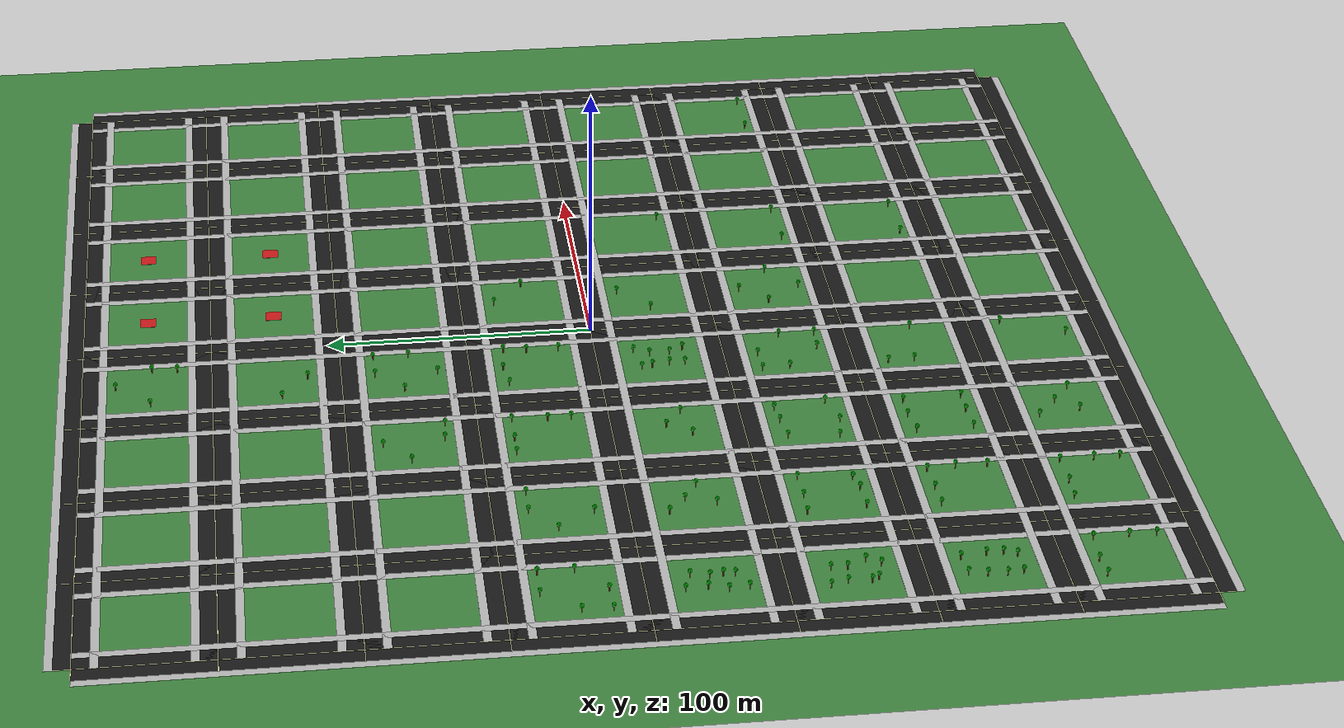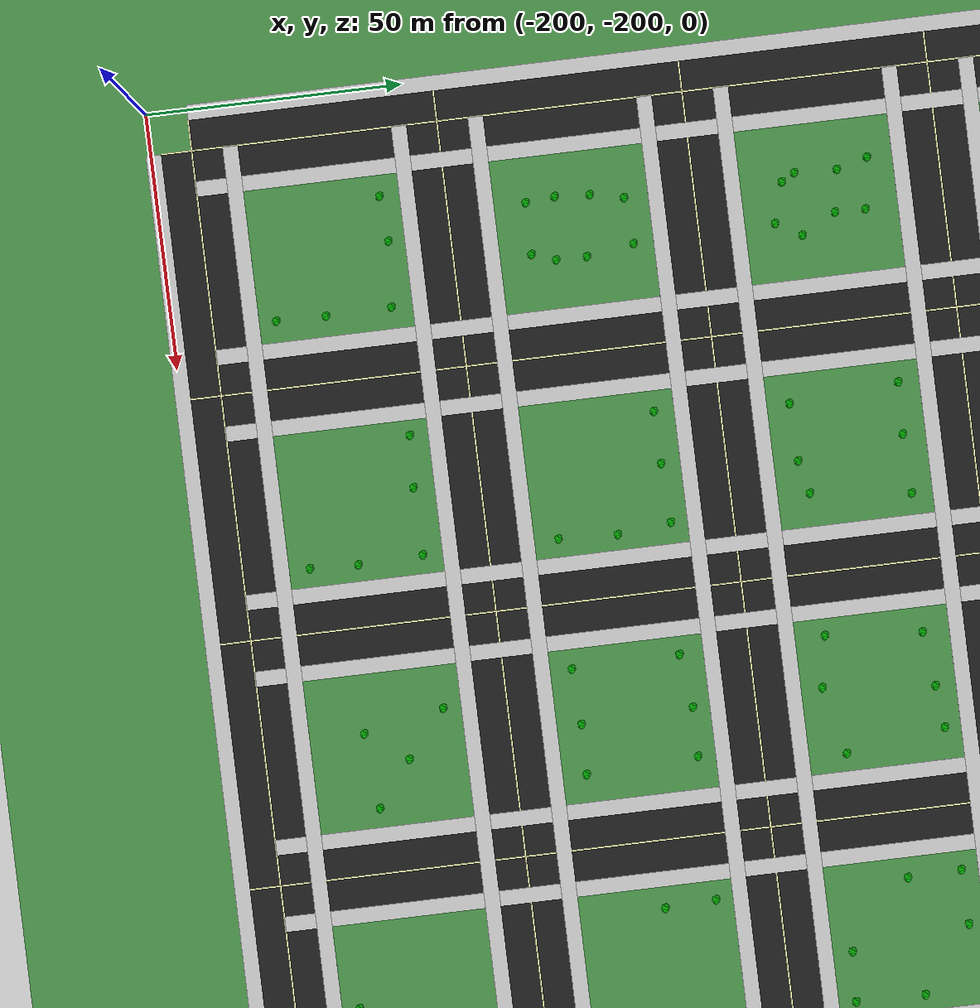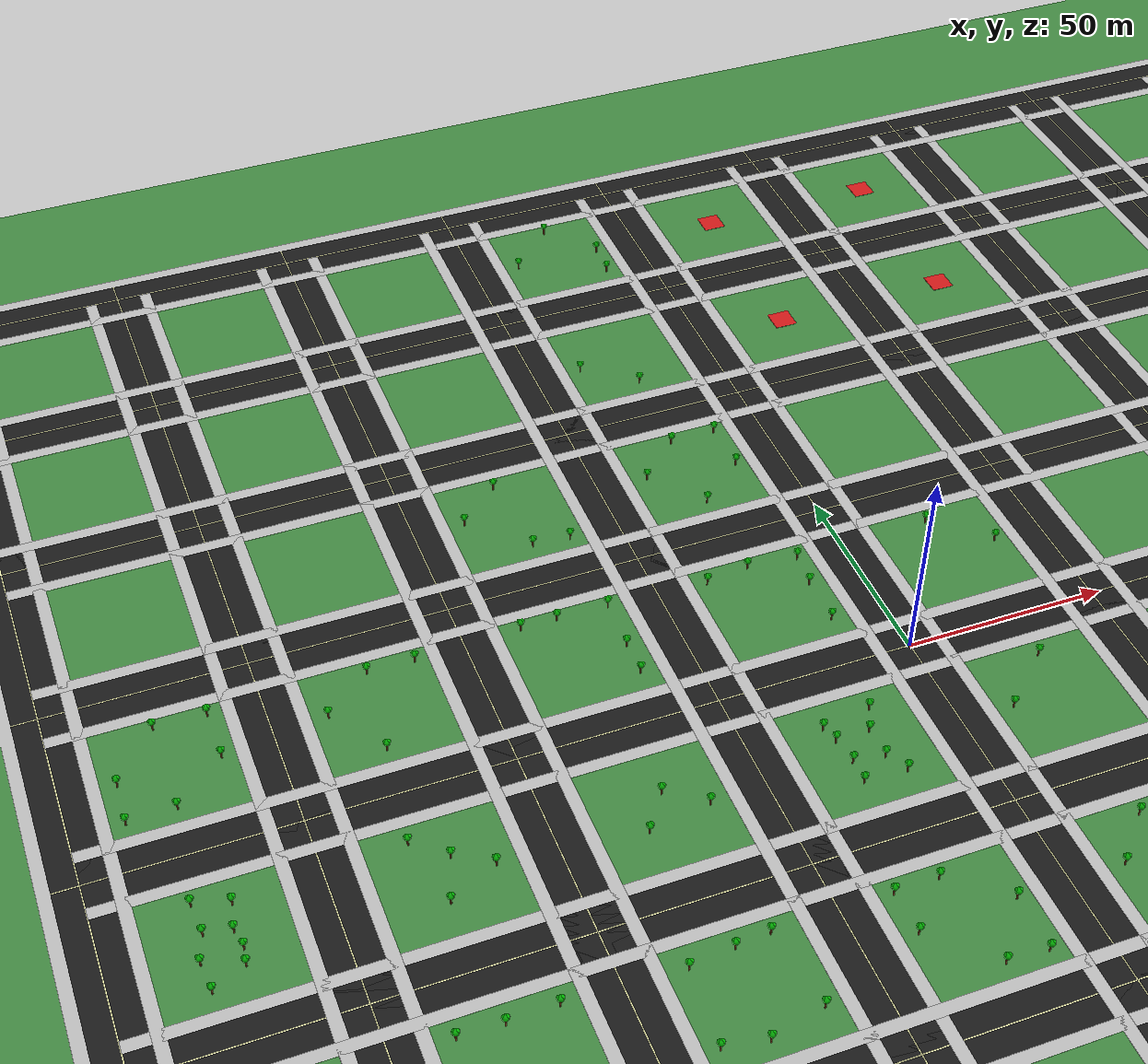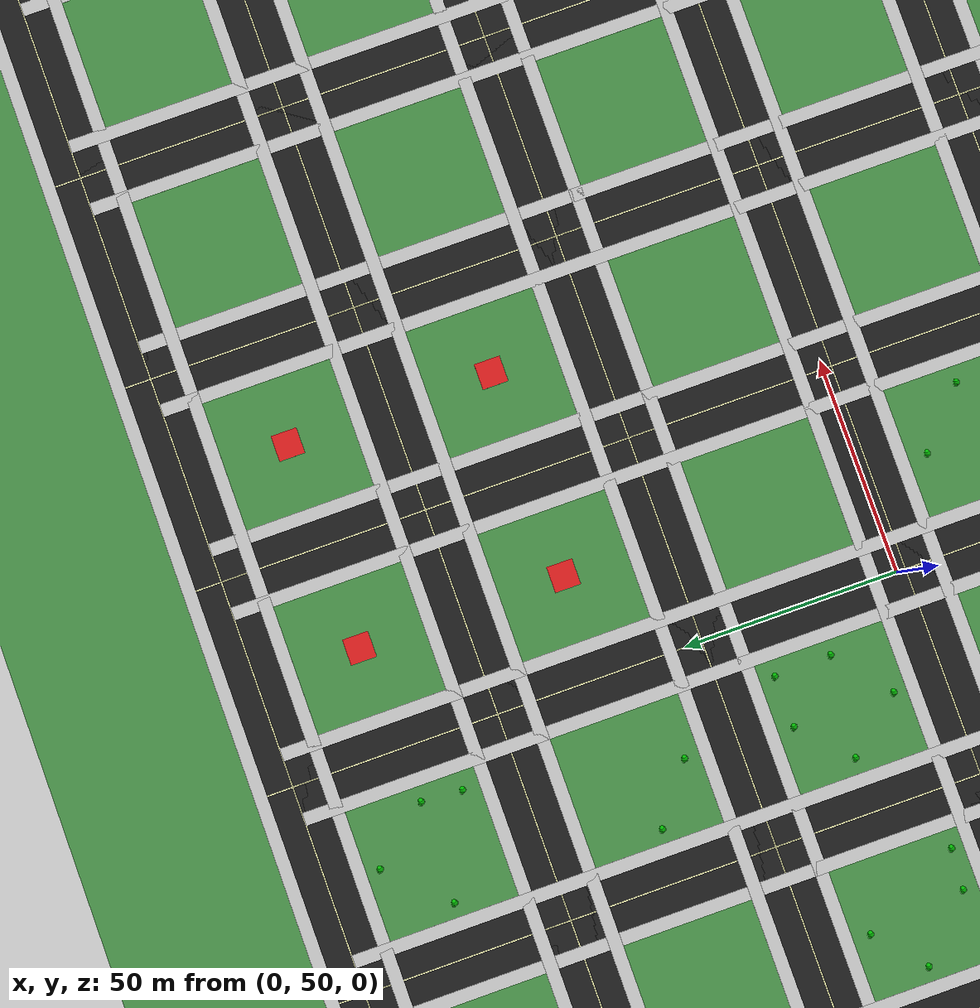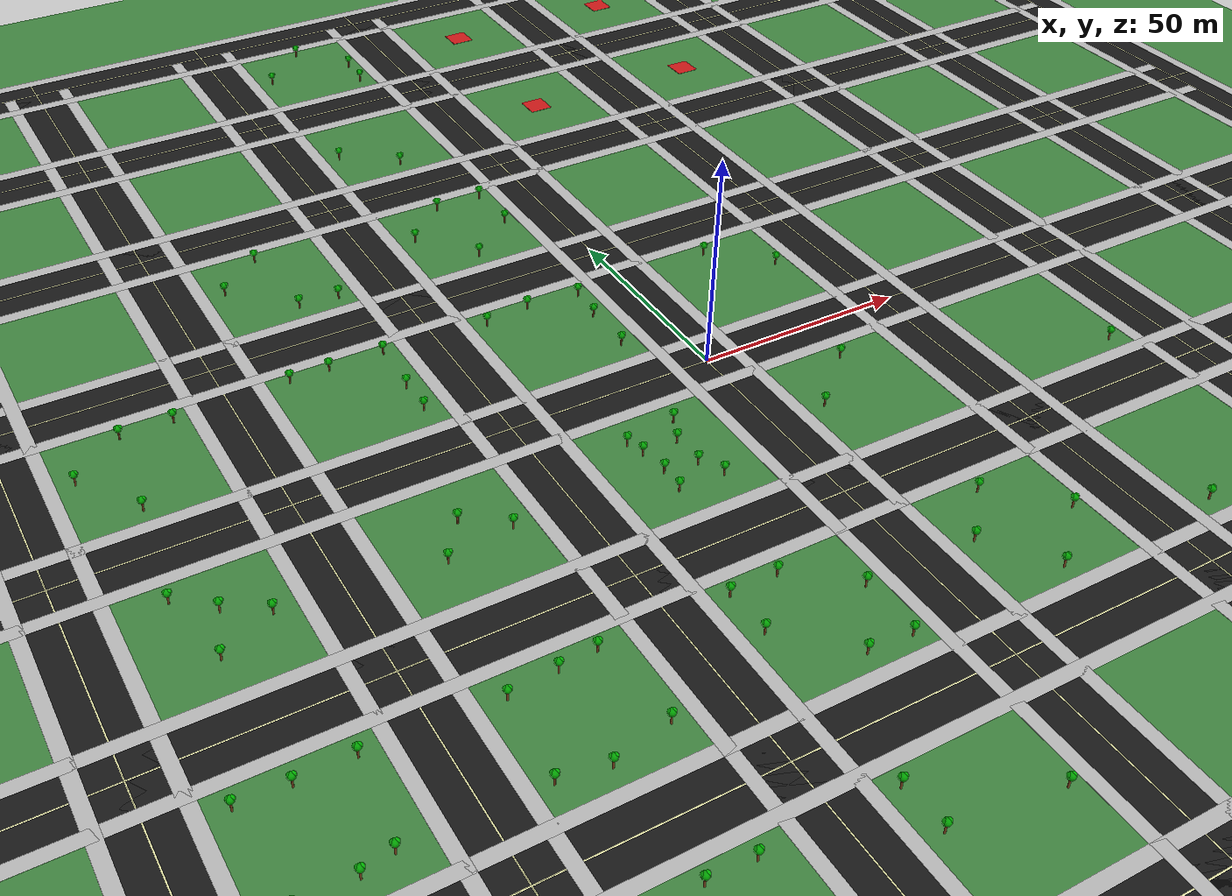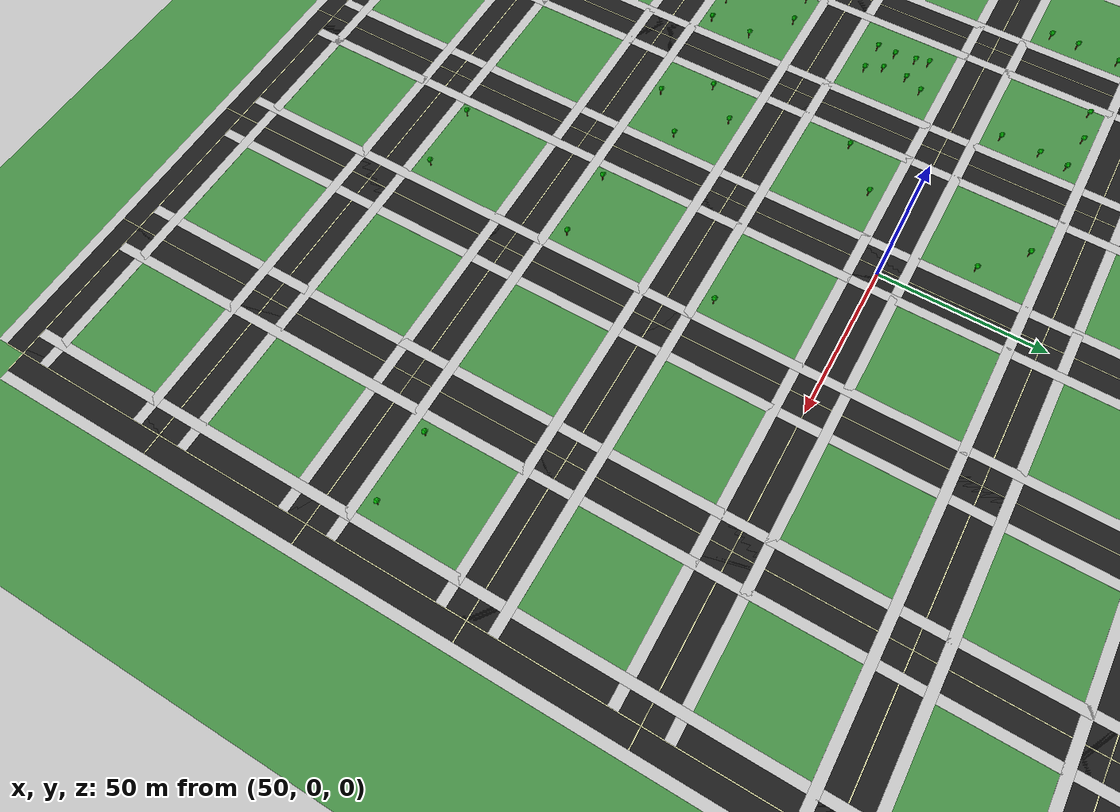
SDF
<sdf version="1.9">
 <world name="earthquake_world">
  <plugin filename="gz-sim-physics-system" name="gz::sim::systems::Physics"/>
  <plugin filename="gz-sim-user-commands-system" name="gz::sim::systems::UserCommands"/>
  <plugin filename="gz-sim-scene-broadcaster-system" name="gz::sim::systems::SceneBroadcaster"/>
  <plugin filename="gz-sim-contact-system" name="gz::sim::systems::Contact"/>
  <plugin filename="gz-sim-imu-system" name="gz::sim::systems::Imu"/>
  <plugin filename="gz-sim-air-pressure-system" name="gz::sim::systems::AirPressure"/>
  <plugin filename="gz-sim-air-speed-system" name="gz::sim::systems::AirSpeed"/>
  <plugin filename="gz-sim-apply-link-wrench-system" name="gz::sim::systems::ApplyLinkWrench"/>
  <plugin filename="gz-sim-navsat-system" name="gz::sim::systems::NavSat"/>
  <plugin filename="gz-sim-magnetometer-system" name="gz::sim::systems::Magnetometer"/>
  <plugin filename="gz-sim-sensors-system" name="gz::sim::systems::Sensors">
   <render_engine>ogre2</render_engine>
  </plugin>
  <physics type="ode">
   <max_step_size>0.004</max_step_size>
   <real_time_factor>1.0</real_time_factor>
   <real_time_update_rate>250</real_time_update_rate>
  </physics>
  <gravity>0 0 -9.8</gravity>
  <atmosphere type="adiabatic"/>
  <magnetic_field>6e-06 2.3e-05 -4.2e-05</magnetic_field>
  <spherical_coordinates>
   <surface_model>EARTH_WGS84</surface_model>
   <world_frame_orientation>ENU</world_frame_orientation>
   <latitude_deg>47.397971057728974</latitude_deg>
   <longitude_deg>8.546163739800146</longitude_deg>
   <elevation>0</elevation>
  </spherical_coordinates>
  <scene>
   <ambient>0.65 0.65 0.65 1</ambient>
   <background>0.72 0.84 0.97 1</background>
   <grid>false</grid>
   <origin_visual>false</origin_visual>
  </scene>
  <light name="sun" type="directional">
   <pose>0 0 200 0 0 0</pose>
   <diffuse>1 1 1 1</diffuse>
   <specular>0.2 0.2 0.2 1</specular>
   <direction>-0.4 0.2 -1</direction>
  </light>
  <model name="ground_plane">
   <static>true</static>
   <link name="link">
    <collision name="collision">
     <geometry><plane><normal>0 0 1</normal><size>1000 1000</size></plane></geometry>
    </collision>
    <visual name="visual">
     <geometry><plane><normal>0 0 1</normal><size>1000 1000</size></plane></geometry>
     <material><ambient>0.25 0.52 0.25 1</ambient><diffuse>0.25 0.52 0.25 1</diffuse></material>
    </visual>
   </link>
  </model>
  <model name="hroad_0">
   <static>true</static>
   <pose>0.00 -192.00 0.010 0 0 0</pose>
   <link name="link">
    <visual name="visual">
     <geometry><box><size>384.000 12.000 0.020</size></box></geometry>
     <material><ambient>0.10 0.10 0.10 1</ambient><diffuse>0.10 0.10 0.10 1</diffuse></material>
    </visual>
   </link>
  </model>
  <model name="hside_top_0">
   <static>true</static>
   <pose>0.00 -184.50 0.030 0 0 0</pose>
   <link name="link">
    <visual name="visual">
     <geometry><box><size>384.000 3.000 0.060</size></box></geometry>
     <material><ambient>0.72 0.72 0.72 1</ambient><diffuse>0.72 0.72 0.72 1</diffuse></material>
    </visual>
   </link>
  </model>
  <model name="hside_bottom_0">
   <static>true</static>
   <pose>0.00 -199.50 0.030 0 0 0</pose>
   <link name="link">
    <visual name="visual">
     <geometry><box><size>384.000 3.000 0.060</size></box></geometry>
     <material><ambient>0.72 0.72 0.72 1</ambient><diffuse>0.72 0.72 0.72 1</diffuse></material>
    </visual>
   </link>
  </model>
  <model name="hline_0">
   <static>true</static>
   <pose>0.00 -192.00 0.041 0 0 0</pose>
   <link name="link">
    <visual name="visual">
     <geometry><box><size>384.000 0.300 0.005</size></box></geometry>
     <material><ambient>0.95 0.95 0.70 1</ambient><diffuse>0.95 0.95 0.70 1</diffuse></material>
    </visual>
   </link>
  </model>
  <model name="hroad_1">
   <static>true</static>
   <pose>0.00 -144.00 0.010 0 0 0</pose>
   <link name="link">
    <visual name="visual">
     <geometry><box><size>384.000 12.000 0.020</size></box></geometry>
     <material><ambient>0.10 0.10 0.10 1</ambient><diffuse>0.10 0.10 0.10 1</diffuse></material>
    </visual>
   </link>
  </model>
  <model name="hside_top_1">
   <static>true</static>
   <pose>0.00 -136.50 0.030 0 0 0</pose>
   <link name="link">
    <visual name="visual">
     <geometry><box><size>384.000 3.000 0.060</size></box></geometry>
     <material><ambient>0.72 0.72 0.72 1</ambient><diffuse>0.72 0.72 0.72 1</diffuse></material>
    </visual>
   </link>
  </model>
  <model name="hside_bottom_1">
   <static>true</static>
   <pose>0.00 -151.50 0.030 0 0 0</pose>
   <link name="link">
    <visual name="visual">
     <geometry><box><size>384.000 3.000 0.060</size></box></geometry>
     <material><ambient>0.72 0.72 0.72 1</ambient><diffuse>0.72 0.72 0.72 1</diffuse></material>
    </visual>
   </link>
  </model>
  <model name="hline_1">
   <static>true</static>
   <pose>0.00 -144.00 0.041 0 0 0</pose>
   <link name="link">
    <visual name="visual">
     <geometry><box><size>384.000 0.300 0.005</size></box></geometry>
     <material><ambient>0.95 0.95 0.70 1</ambient><diffuse>0.95 0.95 0.70 1</diffuse></material>
    </visual>
   </link>
  </model>
  <model name="hroad_2">
   <static>true</static>
   <pose>0.00 -96.00 0.010 0 0 0</pose>
   <link name="link">
    <visual name="visual">
     <geometry><box><size>384.000 12.000 0.020</size></box></geometry>
     <material><ambient>0.10 0.10 0.10 1</ambient><diffuse>0.10 0.10 0.10 1</diffuse></material>
    </visual>
   </link>
  </model>
  <model name="hside_top_2">
   <static>true</static>
   <pose>0.00 -88.50 0.030 0 0 0</pose>
   <link name="link">
    <visual name="visual">
     <geometry><box><size>384.000 3.000 0.060</size></box></geometry>
     <material><ambient>0.72 0.72 0.72 1</ambient><diffuse>0.72 0.72 0.72 1</diffuse></material>
    </visual>
   </link>
  </model>
  <model name="hside_bottom_2">
   <static>true</static>
   <pose>0.00 -103.50 0.030 0 0 0</pose>
   <link name="link">
    <visual name="visual">
     <geometry><box><size>384.000 3.000 0.060</size></box></geometry>
     <material><ambient>0.72 0.72 0.72 1</ambient><diffuse>0.72 0.72 0.72 1</diffuse></material>
    </visual>
   </link>
  </model>
  <model name="hline_2">
   <static>true</static>
   <pose>0.00 -96.00 0.041 0 0 0</pose>
   <link name="link">
    <visual name="visual">
     <geometry><box><size>384.000 0.300 0.005</size></box></geometry>
     <material><ambient>0.95 0.95 0.70 1</ambient><diffuse>0.95 0.95 0.70 1</diffuse></material>
    </visual>
   </link>
  </model>
  <model name="hroad_3">
   <static>true</static>
   <pose>0.00 -48.00 0.010 0 0 0</pose>
   <link name="link">
    <visual name="visual">
     <geometry><box><size>384.000 12.000 0.020</size></box></geometry>
     <material><ambient>0.10 0.10 0.10 1</ambient><diffuse>0.10 0.10 0.10 1</diffuse></material>
    </visual>
   </link>
  </model>
  <model name="hside_top_3">
   <static>true</static>
   <pose>0.00 -40.50 0.030 0 0 0</pose>
   <link name="link">
    <visual name="visual">
     <geometry><box><size>384.000 3.000 0.060</size></box></geometry>
     <material><ambient>0.72 0.72 0.72 1</ambient><diffuse>0.72 0.72 0.72 1</diffuse></material>
    </visual>
   </link>
  </model>
  <model name="hside_bottom_3">
   <static>true</static>
   <pose>0.00 -55.50 0.030 0 0 0</pose>
   <link name="link">
    <visual name="visual">
     <geometry><box><size>384.000 3.000 0.060</size></box></geometry>
     <material><ambient>0.72 0.72 0.72 1</ambient><diffuse>0.72 0.72 0.72 1</diffuse></material>
    </visual>
   </link>
  </model>
  <model name="hline_3">
   <static>true</static>
   <pose>0.00 -48.00 0.041 0 0 0</pose>
   <link name="link">
    <visual name="visual">
     <geometry><box><size>384.000 0.300 0.005</size></box></geometry>
     <material><ambient>0.95 0.95 0.70 1</ambient><diffuse>0.95 0.95 0.70 1</diffuse></material>
    </visual>
   </link>
  </model>
  <model name="hroad_4">
   <static>true</static>
   <pose>0.00 0.00 0.010 0 0 0</pose>
   <link name="link">
    <visual name="visual">
     <geometry><box><size>384.000 12.000 0.020</size></box></geometry>
     <material><ambient>0.10 0.10 0.10 1</ambient><diffuse>0.10 0.10 0.10 1</diffuse></material>
    </visual>
   </link>
  </model>
  <model name="hside_top_4">
   <static>true</static>
   <pose>0.00 7.50 0.030 0 0 0</pose>
   <link name="link">
    <visual name="visual">
     <geometry><box><size>384.000 3.000 0.060</size></box></geometry>
     <material><ambient>0.72 0.72 0.72 1</ambient><diffuse>0.72 0.72 0.72 1</diffuse></material>
    </visual>
   </link>
  </model>
  <model name="hside_bottom_4">
   <static>true</static>
   <pose>0.00 -7.50 0.030 0 0 0</pose>
   <link name="link">
    <visual name="visual">
     <geometry><box><size>384.000 3.000 0.060</size></box></geometry>
     <material><ambient>0.72 0.72 0.72 1</ambient><diffuse>0.72 0.72 0.72 1</diffuse></material>
    </visual>
   </link>
  </model>
  <model name="hline_4">
   <static>true</static>
   <pose>0.00 0.00 0.041 0 0 0</pose>
   <link name="link">
    <visual name="visual">
     <geometry><box><size>384.000 0.300 0.005</size></box></geometry>
     <material><ambient>0.95 0.95 0.70 1</ambient><diffuse>0.95 0.95 0.70 1</diffuse></material>
    </visual>
   </link>
  </model>
  <model name="hroad_5">
   <static>true</static>
   <pose>0.00 48.00 0.010 0 0 0</pose>
   <link name="link">
    <visual name="visual">
     <geometry><box><size>384.000 12.000 0.020</size></box></geometry>
     <material><ambient>0.10 0.10 0.10 1</ambient><diffuse>0.10 0.10 0.10 1</diffuse></material>
    </visual>
   </link>
  </model>
  <model name="hside_top_5">
   <static>true</static>
   <pose>0.00 55.50 0.030 0 0 0</pose>
   <link name="link">
    <visual name="visual">
     <geometry><box><size>384.000 3.000 0.060</size></box></geometry>
     <material><ambient>0.72 0.72 0.72 1</ambient><diffuse>0.72 0.72 0.72 1</diffuse></material>
    </visual>
   </link>
  </model>
  <model name="hside_bottom_5">
   <static>true</static>
   <pose>0.00 40.50 0.030 0 0 0</pose>
   <link name="link">
    <visual name="visual">
     <geometry><box><size>384.000 3.000 0.060</size></box></geometry>
     <material><ambient>0.72 0.72 0.72 1</ambient><diffuse>0.72 0.72 0.72 1</diffuse></material>
    </visual>
   </link>
  </model>
  <model name="hline_5">
   <static>true</static>
   <pose>0.00 48.00 0.041 0 0 0</pose>
   <link name="link">
    <visual name="visual">
     <geometry><box><size>384.000 0.300 0.005</size></box></geometry>
     <material><ambient>0.95 0.95 0.70 1</ambient><diffuse>0.95 0.95 0.70 1</diffuse></material>
    </visual>
   </link>
  </model>
  <model name="hroad_6">
   <static>true</static>
   <pose>0.00 96.00 0.010 0 0 0</pose>
   <link name="link">
    <visual name="visual">
     <geometry><box><size>384.000 12.000 0.020</size></box></geometry>
     <material><ambient>0.10 0.10 0.10 1</ambient><diffuse>0.10 0.10 0.10 1</diffuse></material>
    </visual>
   </link>
  </model>
  <model name="hside_top_6">
   <static>true</static>
   <pose>0.00 103.50 0.030 0 0 0</pose>
   <link name="link">
    <visual name="visual">
     <geometry><box><size>384.000 3.000 0.060</size></box></geometry>
     <material><ambient>0.72 0.72 0.72 1</ambient><diffuse>0.72 0.72 0.72 1</diffuse></material>
    </visual>
   </link>
  </model>
  <model name="hside_bottom_6">
   <static>true</static>
   <pose>0.00 88.50 0.030 0 0 0</pose>
   <link name="link">
    <visual name="visual">
     <geometry><box><size>384.000 3.000 0.060</size></box></geometry>
     <material><ambient>0.72 0.72 0.72 1</ambient><diffuse>0.72 0.72 0.72 1</diffuse></material>
    </visual>
   </link>
  </model>
  <model name="hline_6">
   <static>true</static>
   <pose>0.00 96.00 0.041 0 0 0</pose>
   <link name="link">
    <visual name="visual">
     <geometry><box><size>384.000 0.300 0.005</size></box></geometry>
     <material><ambient>0.95 0.95 0.70 1</ambient><diffuse>0.95 0.95 0.70 1</diffuse></material>
    </visual>
   </link>
  </model>
  <model name="hroad_7">
   <static>true</static>
   <pose>0.00 144.00 0.010 0 0 0</pose>
   <link name="link">
    <visual name="visual">
     <geometry><box><size>384.000 12.000 0.020</size></box></geometry>
     <material><ambient>0.10 0.10 0.10 1</ambient><diffuse>0.10 0.10 0.10 1</diffuse></material>
    </visual>
   </link>
  </model>
  <model name="hside_top_7">
   <static>true</static>
   <pose>0.00 151.50 0.030 0 0 0</pose>
   <link name="link">
    <visual name="visual">
     <geometry><box><size>384.000 3.000 0.060</size></box></geometry>
     <material><ambient>0.72 0.72 0.72 1</ambient><diffuse>0.72 0.72 0.72 1</diffuse></material>
    </visual>
   </link>
  </model>
  <model name="hside_bottom_7">
   <static>true</static>
   <pose>0.00 136.50 0.030 0 0 0</pose>
   <link name="link">
    <visual name="visual">
     <geometry><box><size>384.000 3.000 0.060</size></box></geometry>
     <material><ambient>0.72 0.72 0.72 1</ambient><diffuse>0.72 0.72 0.72 1</diffuse></material>
    </visual>
   </link>
  </model>
  <model name="hline_7">
   <static>true</static>
   <pose>0.00 144.00 0.041 0 0 0</pose>
   <link name="link">
    <visual name="visual">
     <geometry><box><size>384.000 0.300 0.005</size></box></geometry>
     <material><ambient>0.95 0.95 0.70 1</ambient><diffuse>0.95 0.95 0.70 1</diffuse></material>
    </visual>
   </link>
  </model>
  <model name="hroad_8">
   <static>true</static>
   <pose>0.00 192.00 0.010 0 0 0</pose>
   <link name="link">
    <visual name="visual">
     <geometry><box><size>384.000 12.000 0.020</size></box></geometry>
     <material><ambient>0.10 0.10 0.10 1</ambient><diffuse>0.10 0.10 0.10 1</diffuse></material>
    </visual>
   </link>
  </model>
  <model name="hside_top_8">
   <static>true</static>
   <pose>0.00 199.50 0.030 0 0 0</pose>
   <link name="link">
    <visual name="visual">
     <geometry><box><size>384.000 3.000 0.060</size></box></geometry>
     <material><ambient>0.72 0.72 0.72 1</ambient><diffuse>0.72 0.72 0.72 1</diffuse></material>
    </visual>
   </link>
  </model>
  <model name="hside_bottom_8">
   <static>true</static>
   <pose>0.00 184.50 0.030 0 0 0</pose>
   <link name="link">
    <visual name="visual">
     <geometry><box><size>384.000 3.000 0.060</size></box></geometry>
     <material><ambient>0.72 0.72 0.72 1</ambient><diffuse>0.72 0.72 0.72 1</diffuse></material>
    </visual>
   </link>
  </model>
  <model name="hline_8">
   <static>true</static>
   <pose>0.00 192.00 0.041 0 0 0</pose>
   <link name="link">
    <visual name="visual">
     <geometry><box><size>384.000 0.300 0.005</size></box></geometry>
     <material><ambient>0.95 0.95 0.70 1</ambient><diffuse>0.95 0.95 0.70 1</diffuse></material>
    </visual>
   </link>
  </model>
  <model name="vroad_0">
   <static>true</static>
   <pose>-192.00 0.00 0.010 0 0 0</pose>
   <link name="link">
    <visual name="visual">
     <geometry><box><size>12.000 384.000 0.020</size></box></geometry>
     <material><ambient>0.10 0.10 0.10 1</ambient><diffuse>0.10 0.10 0.10 1</diffuse></material>
    </visual>
   </link>
  </model>
  <model name="vside_left_0">
   <static>true</static>
   <pose>-199.50 0.00 0.030 0 0 0</pose>
   <link name="link">
    <visual name="visual">
     <geometry><box><size>3.000 384.000 0.060</size></box></geometry>
     <material><ambient>0.72 0.72 0.72 1</ambient><diffuse>0.72 0.72 0.72 1</diffuse></material>
    </visual>
   </link>
  </model>
  <model name="vside_right_0">
   <static>true</static>
   <pose>-184.50 0.00 0.030 0 0 0</pose>
   <link name="link">
    <visual name="visual">
     <geometry><box><size>3.000 384.000 0.060</size></box></geometry>
     <material><ambient>0.72 0.72 0.72 1</ambient><diffuse>0.72 0.72 0.72 1</diffuse></material>
    </visual>
   </link>
  </model>
  <model name="vline_0">
   <static>true</static>
   <pose>-192.00 0.00 0.041 0 0 0</pose>
   <link name="link">
    <visual name="visual">
     <geometry><box><size>0.300 384.000 0.005</size></box></geometry>
     <material><ambient>0.95 0.95 0.70 1</ambient><diffuse>0.95 0.95 0.70 1</diffuse></material>
    </visual>
   </link>
  </model>
  <model name="vroad_1">
   <static>true</static>
   <pose>-144.00 0.00 0.010 0 0 0</pose>
   <link name="link">
    <visual name="visual">
     <geometry><box><size>12.000 384.000 0.020</size></box></geometry>
     <material><ambient>0.10 0.10 0.10 1</ambient><diffuse>0.10 0.10 0.10 1</diffuse></material>
    </visual>
   </link>
  </model>
  <model name="vside_left_1">
   <static>true</static>
   <pose>-151.50 0.00 0.030 0 0 0</pose>
   <link name="link">
    <visual name="visual">
     <geometry><box><size>3.000 384.000 0.060</size></box></geometry>
     <material><ambient>0.72 0.72 0.72 1</ambient><diffuse>0.72 0.72 0.72 1</diffuse></material>
    </visual>
   </link>
  </model>
  <model name="vside_right_1">
   <static>true</static>
   <pose>-136.50 0.00 0.030 0 0 0</pose>
   <link name="link">
    <visual name="visual">
     <geometry><box><size>3.000 384.000 0.060</size></box></geometry>
     <material><ambient>0.72 0.72 0.72 1</ambient><diffuse>0.72 0.72 0.72 1</diffuse></material>
    </visual>
   </link>
  </model>
  <model name="vline_1">
   <static>true</static>
   <pose>-144.00 0.00 0.041 0 0 0</pose>
   <link name="link">
    <visual name="visual">
     <geometry><box><size>0.300 384.000 0.005</size></box></geometry>
     <material><ambient>0.95 0.95 0.70 1</ambient><diffuse>0.95 0.95 0.70 1</diffuse></material>
    </visual>
   </link>
  </model>
  <model name="vroad_2">
   <static>true</static>
   <pose>-96.00 0.00 0.010 0 0 0</pose>
   <link name="link">
    <visual name="visual">
     <geometry><box><size>12.000 384.000 0.020</size></box></geometry>
     <material><ambient>0.10 0.10 0.10 1</ambient><diffuse>0.10 0.10 0.10 1</diffuse></material>
    </visual>
   </link>
  </model>
  <model name="vside_left_2">
   <static>true</static>
   <pose>-103.50 0.00 0.030 0 0 0</pose>
   <link name="link">
    <visual name="visual">
     <geometry><box><size>3.000 384.000 0.060</size></box></geometry>
     <material><ambient>0.72 0.72 0.72 1</ambient><diffuse>0.72 0.72 0.72 1</diffuse></material>
    </visual>
   </link>
  </model>
  <model name="vside_right_2">
   <static>true</static>
   <pose>-88.50 0.00 0.030 0 0 0</pose>
   <link name="link">
    <visual name="visual">
     <geometry><box><size>3.000 384.000 0.060</size></box></geometry>
     <material><ambient>0.72 0.72 0.72 1</ambient><diffuse>0.72 0.72 0.72 1</diffuse></material>
    </visual>
   </link>
  </model>
  <model name="vline_2">
   <static>true</static>
   <pose>-96.00 0.00 0.041 0 0 0</pose>
   <link name="link">
    <visual name="visual">
     <geometry><box><size>0.300 384.000 0.005</size></box></geometry>
     <material><ambient>0.95 0.95 0.70 1</ambient><diffuse>0.95 0.95 0.70 1</diffuse></material>
    </visual>
   </link>
  </model>
  <model name="vroad_3">
   <static>true</static>
   <pose>-48.00 0.00 0.010 0 0 0</pose>
   <link name="link">
    <visual name="visual">
     <geometry><box><size>12.000 384.000 0.020</size></box></geometry>
     <material><ambient>0.10 0.10 0.10 1</ambient><diffuse>0.10 0.10 0.10 1</diffuse></material>
    </visual>
   </link>
  </model>
  <model name="vside_left_3">
   <static>true</static>
   <pose>-55.50 0.00 0.030 0 0 0</pose>
   <link name="link">
    <visual name="visual">
     <geometry><box><size>3.000 384.000 0.060</size></box></geometry>
     <material><ambient>0.72 0.72 0.72 1</ambient><diffuse>0.72 0.72 0.72 1</diffuse></material>
    </visual>
   </link>
  </model>
  <model name="vside_right_3">
   <static>true</static>
   <pose>-40.50 0.00 0.030 0 0 0</pose>
   <link name="link">
    <visual name="visual">
     <geometry><box><size>3.000 384.000 0.060</size></box></geometry>
     <material><ambient>0.72 0.72 0.72 1</ambient><diffuse>0.72 0.72 0.72 1</diffuse></material>
    </visual>
   </link>
  </model>
  <model name="vline_3">
   <static>true</static>
   <pose>-48.00 0.00 0.041 0 0 0</pose>
   <link name="link">
    <visual name="visual">
     <geometry><box><size>0.300 384.000 0.005</size></box></geometry>
     <material><ambient>0.95 0.95 0.70 1</ambient><diffuse>0.95 0.95 0.70 1</diffuse></material>
    </visual>
   </link>
  </model>
  <model name="vroad_4">
   <static>true</static>
   <pose>0.00 0.00 0.010 0 0 0</pose>
   <link name="link">
    <visual name="visual">
     <geometry><box><size>12.000 384.000 0.020</size></box></geometry>
     <material><ambient>0.10 0.10 0.10 1</ambient><diffuse>0.10 0.10 0.10 1</diffuse></material>
    </visual>
   </link>
  </model>
  <model name="vside_left_4">
   <static>true</static>
   <pose>-7.50 0.00 0.030 0 0 0</pose>
   <link name="link">
    <visual name="visual">
     <geometry><box><size>3.000 384.000 0.060</size></box></geometry>
     <material><ambient>0.72 0.72 0.72 1</ambient><diffuse>0.72 0.72 0.72 1</diffuse></material>
    </visual>
   </link>
  </model>
  <model name="vside_right_4">
   <static>true</static>
   <pose>7.50 0.00 0.030 0 0 0</pose>
   <link name="link">
    <visual name="visual">
     <geometry><box><size>3.000 384.000 0.060</size></box></geometry>
     <material><ambient>0.72 0.72 0.72 1</ambient><diffuse>0.72 0.72 0.72 1</diffuse></material>
    </visual>
   </link>
  </model>
  <model name="vline_4">
   <static>true</static>
   <pose>0.00 0.00 0.041 0 0 0</pose>
   <link name="link">
    <visual name="visual">
     <geometry><box><size>0.300 384.000 0.005</size></box></geometry>
     <material><ambient>0.95 0.95 0.70 1</ambient><diffuse>0.95 0.95 0.70 1</diffuse></material>
    </visual>
   </link>
  </model>
  <model name="vroad_5">
   <static>true</static>
   <pose>48.00 0.00 0.010 0 0 0</pose>
   <link name="link">
    <visual name="visual">
     <geometry><box><size>12.000 384.000 0.020</size></box></geometry>
     <material><ambient>0.10 0.10 0.10 1</ambient><diffuse>0.10 0.10 0.10 1</diffuse></material>
    </visual>
   </link>
  </model>
  <model name="vside_left_5">
   <static>true</static>
   <pose>40.50 0.00 0.030 0 0 0</pose>
   <link name="link">
    <visual name="visual">
     <geometry><box><size>3.000 384.000 0.060</size></box></geometry>
     <material><ambient>0.72 0.72 0.72 1</ambient><diffuse>0.72 0.72 0.72 1</diffuse></material>
    </visual>
   </link>
  </model>
  <model name="vside_right_5">
   <static>true</static>
   <pose>55.50 0.00 0.030 0 0 0</pose>
   <link name="link">
    <visual name="visual">
     <geometry><box><size>3.000 384.000 0.060</size></box></geometry>
     <material><ambient>0.72 0.72 0.72 1</ambient><diffuse>0.72 0.72 0.72 1</diffuse></material>
    </visual>
   </link>
  </model>
  <model name="vline_5">
   <static>true</static>
   <pose>48.00 0.00 0.041 0 0 0</pose>
   <link name="link">
    <visual name="visual">
     <geometry><box><size>0.300 384.000 0.005</size></box></geometry>
     <material><ambient>0.95 0.95 0.70 1</ambient><diffuse>0.95 0.95 0.70 1</diffuse></material>
    </visual>
   </link>
  </model>
  <model name="vroad_6">
   <static>true</static>
   <pose>96.00 0.00 0.010 0 0 0</pose>
   <link name="link">
    <visual name="visual">
     <geometry><box><size>12.000 384.000 0.020</size></box></geometry>
     <material><ambient>0.10 0.10 0.10 1</ambient><diffuse>0.10 0.10 0.10 1</diffuse></material>
    </visual>
   </link>
  </model>
  <model name="vside_left_6">
   <static>true</static>
   <pose>88.50 0.00 0.030 0 0 0</pose>
   <link name="link">
    <visual name="visual">
     <geometry><box><size>3.000 384.000 0.060</size></box></geometry>
     <material><ambient>0.72 0.72 0.72 1</ambient><diffuse>0.72 0.72 0.72 1</diffuse></material>
    </visual>
   </link>
  </model>
  <model name="vside_right_6">
   <static>true</static>
   <pose>103.50 0.00 0.030 0 0 0</pose>
   <link name="link">
    <visual name="visual">
     <geometry><box><size>3.000 384.000 0.060</size></box></geometry>
     <material><ambient>0.72 0.72 0.72 1</ambient><diffuse>0.72 0.72 0.72 1</diffuse></material>
    </visual>
   </link>
  </model>
  <model name="vline_6">
   <static>true</static>
   <pose>96.00 0.00 0.041 0 0 0</pose>
   <link name="link">
    <visual name="visual">
     <geometry><box><size>0.300 384.000 0.005</size></box></geometry>
     <material><ambient>0.95 0.95 0.70 1</ambient><diffuse>0.95 0.95 0.70 1</diffuse></material>
    </visual>
   </link>
  </model>
  <model name="vroad_7">
   <static>true</static>
   <pose>144.00 0.00 0.010 0 0 0</pose>
   <link name="link">
    <visual name="visual">
     <geometry><box><size>12.000 384.000 0.020</size></box></geometry>
     <material><ambient>0.10 0.10 0.10 1</ambient><diffuse>0.10 0.10 0.10 1</diffuse></material>
    </visual>
   </link>
  </model>
  <model name="vside_left_7">
   <static>true</static>
   <pose>136.50 0.00 0.030 0 0 0</pose>
   <link name="link">
    <visual name="visual">
     <geometry><box><size>3.000 384.000 0.060</size></box></geometry>
     <material><ambient>0.72 0.72 0.72 1</ambient><diffuse>0.72 0.72 0.72 1</diffuse></material>
    </visual>
   </link>
  </model>
  <model name="vside_right_7">
   <static>true</static>
   <pose>151.50 0.00 0.030 0 0 0</pose>
   <link name="link">
    <visual name="visual">
     <geometry><box><size>3.000 384.000 0.060</size></box></geometry>
     <material><ambient>0.72 0.72 0.72 1</ambient><diffuse>0.72 0.72 0.72 1</diffuse></material>
    </visual>
   </link>
  </model>
  <model name="vline_7">
   <static>true</static>
   <pose>144.00 0.00 0.041 0 0 0</pose>
   <link name="link">
    <visual name="visual">
     <geometry><box><size>0.300 384.000 0.005</size></box></geometry>
     <material><ambient>0.95 0.95 0.70 1</ambient><diffuse>0.95 0.95 0.70 1</diffuse></material>
    </visual>
   </link>
  </model>
  <model name="vroad_8">
   <static>true</static>
   <pose>192.00 0.00 0.010 0 0 0</pose>
   <link name="link">
    <visual name="visual">
     <geometry><box><size>12.000 384.000 0.020</size></box></geometry>
     <material><ambient>0.10 0.10 0.10 1</ambient><diffuse>0.10 0.10 0.10 1</diffuse></material>
    </visual>
   </link>
  </model>
  <model name="vside_left_8">
   <static>true</static>
   <pose>184.50 0.00 0.030 0 0 0</pose>
   <link name="link">
    <visual name="visual">
     <geometry><box><size>3.000 384.000 0.060</size></box></geometry>
     <material><ambient>0.72 0.72 0.72 1</ambient><diffuse>0.72 0.72 0.72 1</diffuse></material>
    </visual>
   </link>
  </model>
  <model name="vside_right_8">
   <static>true</static>
   <pose>199.50 0.00 0.030 0 0 0</pose>
   <link name="link">
    <visual name="visual">
     <geometry><box><size>3.000 384.000 0.060</size></box></geometry>
     <material><ambient>0.72 0.72 0.72 1</ambient><diffuse>0.72 0.72 0.72 1</diffuse></material>
    </visual>
   </link>
  </model>
  <model name="vline_8">
   <static>true</static>
   <pose>192.00 0.00 0.041 0 0 0</pose>
   <link name="link">
    <visual name="visual">
     <geometry><box><size>0.300 384.000 0.005</size></box></geometry>
     <material><ambient>0.95 0.95 0.70 1</ambient><diffuse>0.95 0.95 0.70 1</diffuse></material>
    </visual>
   </link>
  </model>
  <model name="intersection_0_0">
   <static>true</static>
   <pose>-192.00 -192.00 0.041 0 0 0</pose>
   <link name="link">
    <visual name="visual">
     <geometry><box><size>12.000 0.300 0.005</size></box></geometry>
     <material><ambient>0.95 0.95 0.70 1</ambient><diffuse>0.95 0.95 0.70 1</diffuse></material>
    </visual>
   </link>
  </model>
  <model name="intersection_cross_0_0">
   <static>true</static>
   <pose>-192.00 -192.00 0.041 0 0 0</pose>
   <link name="link">
    <visual name="visual">
     <geometry><box><size>0.300 12.000 0.005</size></box></geometry>
     <material><ambient>0.95 0.95 0.70 1</ambient><diffuse>0.95 0.95 0.70 1</diffuse></material>
    </visual>
   </link>
  </model>
  <model name="intersection_0_1">
   <static>true</static>
   <pose>-144.00 -192.00 0.041 0 0 0</pose>
   <link name="link">
    <visual name="visual">
     <geometry><box><size>12.000 0.300 0.005</size></box></geometry>
     <material><ambient>0.95 0.95 0.70 1</ambient><diffuse>0.95 0.95 0.70 1</diffuse></material>
    </visual>
   </link>
  </model>
  <model name="intersection_cross_0_1">
   <static>true</static>
   <pose>-144.00 -192.00 0.041 0 0 0</pose>
   <link name="link">
    <visual name="visual">
     <geometry><box><size>0.300 12.000 0.005</size></box></geometry>
     <material><ambient>0.95 0.95 0.70 1</ambient><diffuse>0.95 0.95 0.70 1</diffuse></material>
    </visual>
   </link>
  </model>
  <model name="intersection_0_2">
   <static>true</static>
   <pose>-96.00 -192.00 0.041 0 0 0</pose>
   <link name="link">
    <visual name="visual">
     <geometry><box><size>12.000 0.300 0.005</size></box></geometry>
     <material><ambient>0.95 0.95 0.70 1</ambient><diffuse>0.95 0.95 0.70 1</diffuse></material>
    </visual>
   </link>
  </model>
  <model name="intersection_cross_0_2">
   <static>true</static>
   <pose>-96.00 -192.00 0.041 0 0 0</pose>
   <link name="link">
    <visual name="visual">
     <geometry><box><size>0.300 12.000 0.005</size></box></geometry>
     <material><ambient>0.95 0.95 0.70 1</ambient><diffuse>0.95 0.95 0.70 1</diffuse></material>
    </visual>
   </link>
  </model>
  <model name="intersection_0_3">
   <static>true</static>
   <pose>-48.00 -192.00 0.041 0 0 0</pose>
   <link name="link">
    <visual name="visual">
     <geometry><box><size>12.000 0.300 0.005</size></box></geometry>
     <material><ambient>0.95 0.95 0.70 1</ambient><diffuse>0.95 0.95 0.70 1</diffuse></material>
    </visual>
   </link>
  </model>
  <model name="intersection_cross_0_3">
   <static>true</static>
   <pose>-48.00 -192.00 0.041 0 0 0</pose>
   <link name="link">
    <visual name="visual">
     <geometry><box><size>0.300 12.000 0.005</size></box></geometry>
     <material><ambient>0.95 0.95 0.70 1</ambient><diffuse>0.95 0.95 0.70 1</diffuse></material>
    </visual>
   </link>
  </model>
  <model name="intersection_0_4">
   <static>true</static>
   <pose>0.00 -192.00 0.041 0 0 0</pose>
   <link name="link">
    <visual name="visual">
     <geometry><box><size>12.000 0.300 0.005</size></box></geometry>
     <material><ambient>0.95 0.95 0.70 1</ambient><diffuse>0.95 0.95 0.70 1</diffuse></material>
    </visual>
   </link>
  </model>
  <model name="intersection_cross_0_4">
   <static>true</static>
   <pose>0.00 -192.00 0.041 0 0 0</pose>
   <link name="link">
    <visual name="visual">
     <geometry><box><size>0.300 12.000 0.005</size></box></geometry>
     <material><ambient>0.95 0.95 0.70 1</ambient><diffuse>0.95 0.95 0.70 1</diffuse></material>
    </visual>
   </link>
  </model>
  <model name="intersection_0_5">
   <static>true</static>
   <pose>48.00 -192.00 0.041 0 0 0</pose>
   <link name="link">
    <visual name="visual">
     <geometry><box><size>12.000 0.300 0.005</size></box></geometry>
     <material><ambient>0.95 0.95 0.70 1</ambient><diffuse>0.95 0.95 0.70 1</diffuse></material>
    </visual>
   </link>
  </model>
  <model name="intersection_cross_0_5">
   <static>true</static>
   <pose>48.00 -192.00 0.041 0 0 0</pose>
   <link name="link">
    <visual name="visual">
     <geometry><box><size>0.300 12.000 0.005</size></box></geometry>
     <material><ambient>0.95 0.95 0.70 1</ambient><diffuse>0.95 0.95 0.70 1</diffuse></material>
    </visual>
   </link>
  </model>
  <model name="intersection_0_6">
   <static>true</static>
   <pose>96.00 -192.00 0.041 0 0 0</pose>
   <link name="link">
    <visual name="visual">
     <geometry><box><size>12.000 0.300 0.005</size></box></geometry>
     <material><ambient>0.95 0.95 0.70 1</ambient><diffuse>0.95 0.95 0.70 1</diffuse></material>
    </visual>
   </link>
  </model>
  <model name="intersection_cross_0_6">
   <static>true</static>
   <pose>96.00 -192.00 0.041 0 0 0</pose>
   <link name="link">
    <visual name="visual">
     <geometry><box><size>0.300 12.000 0.005</size></box></geometry>
     <material><ambient>0.95 0.95 0.70 1</ambient><diffuse>0.95 0.95 0.70 1</diffuse></material>
    </visual>
   </link>
  </model>
  <model name="intersection_0_7">
   <static>true</static>
   <pose>144.00 -192.00 0.041 0 0 0</pose>
   <link name="link">
    <visual name="visual">
     <geometry><box><size>12.000 0.300 0.005</size></box></geometry>
     <material><ambient>0.95 0.95 0.70 1</ambient><diffuse>0.95 0.95 0.70 1</diffuse></material>
    </visual>
   </link>
  </model>
  <model name="intersection_cross_0_7">
   <static>true</static>
   <pose>144.00 -192.00 0.041 0 0 0</pose>
   <link name="link">
    <visual name="visual">
     <geometry><box><size>0.300 12.000 0.005</size></box></geometry>
     <material><ambient>0.95 0.95 0.70 1</ambient><diffuse>0.95 0.95 0.70 1</diffuse></material>
    </visual>
   </link>
  </model>
  <model name="intersection_0_8">
   <static>true</static>
   <pose>192.00 -192.00 0.041 0 0 0</pose>
   <link name="link">
    <visual name="visual">
     <geometry><box><size>12.000 0.300 0.005</size></box></geometry>
     <material><ambient>0.95 0.95 0.70 1</ambient><diffuse>0.95 0.95 0.70 1</diffuse></material>
    </visual>
   </link>
  </model>
  <model name="intersection_cross_0_8">
   <static>true</static>
   <pose>192.00 -192.00 0.041 0 0 0</pose>
   <link name="link">
    <visual name="visual">
     <geometry><box><size>0.300 12.000 0.005</size></box></geometry>
     <material><ambient>0.95 0.95 0.70 1</ambient><diffuse>0.95 0.95 0.70 1</diffuse></material>
    </visual>
   </link>
  </model>
  <model name="intersection_1_0">
   <static>true</static>
   <pose>-192.00 -144.00 0.041 0 0 0</pose>
   <link name="link">
    <visual name="visual">
     <geometry><box><size>12.000 0.300 0.005</size></box></geometry>
     <material><ambient>0.95 0.95 0.70 1</ambient><diffuse>0.95 0.95 0.70 1</diffuse></material>
    </visual>
   </link>
  </model>
  <model name="intersection_cross_1_0">
   <static>true</static>
   <pose>-192.00 -144.00 0.041 0 0 0</pose>
   <link name="link">
    <visual name="visual">
     <geometry><box><size>0.300 12.000 0.005</size></box></geometry>
     <material><ambient>0.95 0.95 0.70 1</ambient><diffuse>0.95 0.95 0.70 1</diffuse></material>
    </visual>
   </link>
  </model>
  <model name="intersection_1_1">
   <static>true</static>
   <pose>-144.00 -144.00 0.041 0 0 0</pose>
   <link name="link">
    <visual name="visual">
     <geometry><box><size>12.000 0.300 0.005</size></box></geometry>
     <material><ambient>0.95 0.95 0.70 1</ambient><diffuse>0.95 0.95 0.70 1</diffuse></material>
    </visual>
   </link>
  </model>
  <model name="intersection_cross_1_1">
   <static>true</static>
   <pose>-144.00 -144.00 0.041 0 0 0</pose>
   <link name="link">
    <visual name="visual">
     <geometry><box><size>0.300 12.000 0.005</size></box></geometry>
     <material><ambient>0.95 0.95 0.70 1</ambient><diffuse>0.95 0.95 0.70 1</diffuse></material>
    </visual>
   </link>
  </model>
  <model name="intersection_1_2">
   <static>true</static>
   <pose>-96.00 -144.00 0.041 0 0 0</pose>
   <link name="link">
    <visual name="visual">
     <geometry><box><size>12.000 0.300 0.005</size></box></geometry>
     <material><ambient>0.95 0.95 0.70 1</ambient><diffuse>0.95 0.95 0.70 1</diffuse></material>
    </visual>
   </link>
  </model>
  <model name="intersection_cross_1_2">
   <static>true</static>
   <pose>-96.00 -144.00 0.041 0 0 0</pose>
   <link name="link">
    <visual name="visual">
     <geometry><box><size>0.300 12.000 0.005</size></box></geometry>
     <material><ambient>0.95 0.95 0.70 1</ambient><diffuse>0.95 0.95 0.70 1</diffuse></material>
    </visual>
   </link>
  </model>
  <model name="intersection_1_3">
   <static>true</static>
   <pose>-48.00 -144.00 0.041 0 0 0</pose>
   <link name="link">
    <visual name="visual">
     <geometry><box><size>12.000 0.300 0.005</size></box></geometry>
     <material><ambient>0.95 0.95 0.70 1</ambient><diffuse>0.95 0.95 0.70 1</diffuse></material>
    </visual>
   </link>
  </model>
  <model name="intersection_cross_1_3">
   <static>true</static>
   <pose>-48.00 -144.00 0.041 0 0 0</pose>
   <link name="link">
    <visual name="visual">
     <geometry><box><size>0.300 12.000 0.005</size></box></geometry>
     <material><ambient>0.95 0.95 0.70 1</ambient><diffuse>0.95 0.95 0.70 1</diffuse></material>
    </visual>
   </link>
  </model>
  <model name="intersection_1_4">
   <static>true</static>
   <pose>0.00 -144.00 0.041 0 0 0</pose>
   <link name="link">
    <visual name="visual">
     <geometry><box><size>12.000 0.300 0.005</size></box></geometry>
     <material><ambient>0.95 0.95 0.70 1</ambient><diffuse>0.95 0.95 0.70 1</diffuse></material>
    </visual>
   </link>
  </model>
  <model name="intersection_cross_1_4">
   <static>true</static>
   <pose>0.00 -144.00 0.041 0 0 0</pose>
   <link name="link">
    <visual name="visual">
     <geometry><box><size>0.300 12.000 0.005</size></box></geometry>
     <material><ambient>0.95 0.95 0.70 1</ambient><diffuse>0.95 0.95 0.70 1</diffuse></material>
    </visual>
   </link>
  </model>
  <model name="intersection_1_5">
   <static>true</static>
   <pose>48.00 -144.00 0.041 0 0 0</pose>
   <link name="link">
    <visual name="visual">
     <geometry><box><size>12.000 0.300 0.005</size></box></geometry>
     <material><ambient>0.95 0.95 0.70 1</ambient><diffuse>0.95 0.95 0.70 1</diffuse></material>
    </visual>
   </link>
  </model>
  <model name="intersection_cross_1_5">
   <static>true</static>
   <pose>48.00 -144.00 0.041 0 0 0</pose>
   <link name="link">
    <visual name="visual">
     <geometry><box><size>0.300 12.000 0.005</size></box></geometry>
     <material><ambient>0.95 0.95 0.70 1</ambient><diffuse>0.95 0.95 0.70 1</diffuse></material>
    </visual>
   </link>
  </model>
  <model name="intersection_1_6">
   <static>true</static>
   <pose>96.00 -144.00 0.041 0 0 0</pose>
   <link name="link">
    <visual name="visual">
     <geometry><box><size>12.000 0.300 0.005</size></box></geometry>
     <material><ambient>0.95 0.95 0.70 1</ambient><diffuse>0.95 0.95 0.70 1</diffuse></material>
    </visual>
   </link>
  </model>
  <model name="intersection_cross_1_6">
   <static>true</static>
   <pose>96.00 -144.00 0.041 0 0 0</pose>
   <link name="link">
    <visual name="visual">
     <geometry><box><size>0.300 12.000 0.005</size></box></geometry>
     <material><ambient>0.95 0.95 0.70 1</ambient><diffuse>0.95 0.95 0.70 1</diffuse></material>
    </visual>
   </link>
  </model>
  <model name="intersection_1_7">
   <static>true</static>
   <pose>144.00 -144.00 0.041 0 0 0</pose>
   <link name="link">
    <visual name="visual">
     <geometry><box><size>12.000 0.300 0.005</size></box></geometry>
     <material><ambient>0.95 0.95 0.70 1</ambient><diffuse>0.95 0.95 0.70 1</diffuse></material>
    </visual>
   </link>
  </model>
  <model name="intersection_cross_1_7">
   <static>true</static>
   <pose>144.00 -144.00 0.041 0 0 0</pose>
   <link name="link">
    <visual name="visual">
     <geometry><box><size>0.300 12.000 0.005</size></box></geometry>
     <material><ambient>0.95 0.95 0.70 1</ambient><diffuse>0.95 0.95 0.70 1</diffuse></material>
    </visual>
   </link>
  </model>
  <model name="intersection_1_8">
   <static>true</static>
   <pose>192.00 -144.00 0.041 0 0 0</pose>
   <link name="link">
    <visual name="visual">
     <geometry><box><size>12.000 0.300 0.005</size></box></geometry>
     <material><ambient>0.95 0.95 0.70 1</ambient><diffuse>0.95 0.95 0.70 1</diffuse></material>
    </visual>
   </link>
  </model>
  <model name="intersection_cross_1_8">
   <static>true</static>
   <pose>192.00 -144.00 0.041 0 0 0</pose>
   <link name="link">
    <visual name="visual">
     <geometry><box><size>0.300 12.000 0.005</size></box></geometry>
     <material><ambient>0.95 0.95 0.70 1</ambient><diffuse>0.95 0.95 0.70 1</diffuse></material>
    </visual>
   </link>
  </model>
  <model name="intersection_2_0">
   <static>true</static>
   <pose>-192.00 -96.00 0.041 0 0 0</pose>
   <link name="link">
    <visual name="visual">
     <geometry><box><size>12.000 0.300 0.005</size></box></geometry>
     <material><ambient>0.95 0.95 0.70 1</ambient><diffuse>0.95 0.95 0.70 1</diffuse></material>
    </visual>
   </link>
  </model>
  <model name="intersection_cross_2_0">
   <static>true</static>
   <pose>-192.00 -96.00 0.041 0 0 0</pose>
   <link name="link">
    <visual name="visual">
     <geometry><box><size>0.300 12.000 0.005</size></box></geometry>
     <material><ambient>0.95 0.95 0.70 1</ambient><diffuse>0.95 0.95 0.70 1</diffuse></material>
    </visual>
   </link>
  </model>
  <model name="intersection_2_1">
   <static>true</static>
   <pose>-144.00 -96.00 0.041 0 0 0</pose>
   <link name="link">
    <visual name="visual">
     <geometry><box><size>12.000 0.300 0.005</size></box></geometry>
     <material><ambient>0.95 0.95 0.70 1</ambient><diffuse>0.95 0.95 0.70 1</diffuse></material>
    </visual>
   </link>
  </model>
  <model name="intersection_cross_2_1">
   <static>true</static>
   <pose>-144.00 -96.00 0.041 0 0 0</pose>
   <link name="link">
    <visual name="visual">
     <geometry><box><size>0.300 12.000 0.005</size></box></geometry>
     <material><ambient>0.95 0.95 0.70 1</ambient><diffuse>0.95 0.95 0.70 1</diffuse></material>
    </visual>
   </link>
  </model>
  <model name="intersection_2_2">
   <static>true</static>
   <pose>-96.00 -96.00 0.041 0 0 0</pose>
   <link name="link">
    <visual name="visual">
     <geometry><box><size>12.000 0.300 0.005</size></box></geometry>
     <material><ambient>0.95 0.95 0.70 1</ambient><diffuse>0.95 0.95 0.70 1</diffuse></material>
    </visual>
   </link>
  </model>
  <model name="intersection_cross_2_2">
   <static>true</static>
   <pose>-96.00 -96.00 0.041 0 0 0</pose>
   <link name="link">
    <visual name="visual">
     <geometry><box><size>0.300 12.000 0.005</size></box></geometry>
     <material><ambient>0.95 0.95 0.70 1</ambient><diffuse>0.95 0.95 0.70 1</diffuse></material>
    </visual>
   </link>
  </model>
  <model name="intersection_2_3">
   <static>true</static>
   <pose>-48.00 -96.00 0.041 0 0 0</pose>
   <link name="link">
    <visual name="visual">
     <geometry><box><size>12.000 0.300 0.005</size></box></geometry>
     <material><ambient>0.95 0.95 0.70 1</ambient><diffuse>0.95 0.95 0.70 1</diffuse></material>
    </visual>
   </link>
  </model>
  <model name="intersection_cross_2_3">
   <static>true</static>
   <pose>-48.00 -96.00 0.041 0 0 0</pose>
   <link name="link">
    <visual name="visual">
     <geometry><box><size>0.300 12.000 0.005</size></box></geometry>
     <material><ambient>0.95 0.95 0.70 1</ambient><diffuse>0.95 0.95 0.70 1</diffuse></material>
    </visual>
   </link>
  </model>
  <model name="intersection_2_4">
   <static>true</static>
   <pose>0.00 -96.00 0.041 0 0 0</pose>
   <link name="link">
    <visual name="visual">
     <geometry><box><size>12.000 0.300 0.005</size></box></geometry>
     <material><ambient>0.95 0.95 0.70 1</ambient><diffuse>0.95 0.95 0.70 1</diffuse></material>
    </visual>
   </link>
  </model>
  <model name="intersection_cross_2_4">
   <static>true</static>
   <pose>0.00 -96.00 0.041 0 0 0</pose>
   <link name="link">
    <visual name="visual">
     <geometry><box><size>0.300 12.000 0.005</size></box></geometry>
     <material><ambient>0.95 0.95 0.70 1</ambient><diffuse>0.95 0.95 0.70 1</diffuse></material>
    </visual>
   </link>
  </model>
  <model name="intersection_2_5">
   <static>true</static>
   <pose>48.00 -96.00 0.041 0 0 0</pose>
   <link name="link">
    <visual name="visual">
     <geometry><box><size>12.000 0.300 0.005</size></box></geometry>
     <material><ambient>0.95 0.95 0.70 1</ambient><diffuse>0.95 0.95 0.70 1</diffuse></material>
    </visual>
   </link>
  </model>
  <model name="intersection_cross_2_5">
   <static>true</static>
   <pose>48.00 -96.00 0.041 0 0 0</pose>
   <link name="link">
    <visual name="visual">
     <geometry><box><size>0.300 12.000 0.005</size></box></geometry>
     <material><ambient>0.95 0.95 0.70 1</ambient><diffuse>0.95 0.95 0.70 1</diffuse></material>
    </visual>
   </link>
  </model>
  <model name="intersection_2_6">
   <static>true</static>
   <pose>96.00 -96.00 0.041 0 0 0</pose>
   <link name="link">
    <visual name="visual">
     <geometry><box><size>12.000 0.300 0.005</size></box></geometry>
     <material><ambient>0.95 0.95 0.70 1</ambient><diffuse>0.95 0.95 0.70 1</diffuse></material>
    </visual>
   </link>
  </model>
  <model name="intersection_cross_2_6">
   <static>true</static>
   <pose>96.00 -96.00 0.041 0 0 0</pose>
   <link name="link">
    <visual name="visual">
     <geometry><box><size>0.300 12.000 0.005</size></box></geometry>
     <material><ambient>0.95 0.95 0.70 1</ambient><diffuse>0.95 0.95 0.70 1</diffuse></material>
    </visual>
   </link>
  </model>
  <model name="intersection_2_7">
   <static>true</static>
   <pose>144.00 -96.00 0.041 0 0 0</pose>
   <link name="link">
    <visual name="visual">
     <geometry><box><size>12.000 0.300 0.005</size></box></geometry>
     <material><ambient>0.95 0.95 0.70 1</ambient><diffuse>0.95 0.95 0.70 1</diffuse></material>
    </visual>
   </link>
  </model>
  <model name="intersection_cross_2_7">
   <static>true</static>
   <pose>144.00 -96.00 0.041 0 0 0</pose>
   <link name="link">
    <visual name="visual">
     <geometry><box><size>0.300 12.000 0.005</size></box></geometry>
     <material><ambient>0.95 0.95 0.70 1</ambient><diffuse>0.95 0.95 0.70 1</diffuse></material>
    </visual>
   </link>
  </model>
  <model name="intersection_2_8">
   <static>true</static>
   <pose>192.00 -96.00 0.041 0 0 0</pose>
   <link name="link">
    <visual name="visual">
     <geometry><box><size>12.000 0.300 0.005</size></box></geometry>
     <material><ambient>0.95 0.95 0.70 1</ambient><diffuse>0.95 0.95 0.70 1</diffuse></material>
    </visual>
   </link>
  </model>
  <model name="intersection_cross_2_8">
   <static>true</static>
   <pose>192.00 -96.00 0.041 0 0 0</pose>
   <link name="link">
    <visual name="visual">
     <geometry><box><size>0.300 12.000 0.005</size></box></geometry>
     <material><ambient>0.95 0.95 0.70 1</ambient><diffuse>0.95 0.95 0.70 1</diffuse></material>
    </visual>
   </link>
  </model>
  <model name="intersection_3_0">
   <static>true</static>
   <pose>-192.00 -48.00 0.041 0 0 0</pose>
   <link name="link">
    <visual name="visual">
     <geometry><box><size>12.000 0.300 0.005</size></box></geometry>
     <material><ambient>0.95 0.95 0.70 1</ambient><diffuse>0.95 0.95 0.70 1</diffuse></material>
    </visual>
   </link>
  </model>
  <model name="intersection_cross_3_0">
   <static>true</static>
   <pose>-192.00 -48.00 0.041 0 0 0</pose>
   <link name="link">
    <visual name="visual">
     <geometry><box><size>0.300 12.000 0.005</size></box></geometry>
     <material><ambient>0.95 0.95 0.70 1</ambient><diffuse>0.95 0.95 0.70 1</diffuse></material>
    </visual>
   </link>
  </model>
  <model name="intersection_3_1">
   <static>true</static>
   <pose>-144.00 -48.00 0.041 0 0 0</pose>
   <link name="link">
    <visual name="visual">
     <geometry><box><size>12.000 0.300 0.005</size></box></geometry>
     <material><ambient>0.95 0.95 0.70 1</ambient><diffuse>0.95 0.95 0.70 1</diffuse></material>
    </visual>
   </link>
  </model>
  <model name="intersection_cross_3_1">
   <static>true</static>
   <pose>-144.00 -48.00 0.041 0 0 0</pose>
   <link name="link">
    <visual name="visual">
     <geometry><box><size>0.300 12.000 0.005</size></box></geometry>
     <material><ambient>0.95 0.95 0.70 1</ambient><diffuse>0.95 0.95 0.70 1</diffuse></material>
    </visual>
   </link>
  </model>
  <model name="intersection_3_2">
   <static>true</static>
   <pose>-96.00 -48.00 0.041 0 0 0</pose>
   <link name="link">
    <visual name="visual">
     <geometry><box><size>12.000 0.300 0.005</size></box></geometry>
     <material><ambient>0.95 0.95 0.70 1</ambient><diffuse>0.95 0.95 0.70 1</diffuse></material>
    </visual>
   </link>
  </model>
  <model name="intersection_cross_3_2">
   <static>true</static>
   <pose>-96.00 -48.00 0.041 0 0 0</pose>
   <link name="link">
    <visual name="visual">
     <geometry><box><size>0.300 12.000 0.005</size></box></geometry>
     <material><ambient>0.95 0.95 0.70 1</ambient><diffuse>0.95 0.95 0.70 1</diffuse></material>
    </visual>
   </link>
  </model>
  <model name="intersection_3_3">
   <static>true</static>
   <pose>-48.00 -48.00 0.041 0 0 0</pose>
   <link name="link">
    <visual name="visual">
     <geometry><box><size>12.000 0.300 0.005</size></box></geometry>
     <material><ambient>0.95 0.95 0.70 1</ambient><diffuse>0.95 0.95 0.70 1</diffuse></material>
    </visual>
   </link>
  </model>
  <model name="intersection_cross_3_3">
   <static>true</static>
   <pose>-48.00 -48.00 0.041 0 0 0</pose>
   <link name="link">
    <visual name="visual">
     <geometry><box><size>0.300 12.000 0.005</size></box></geometry>
     <material><ambient>0.95 0.95 0.70 1</ambient><diffuse>0.95 0.95 0.70 1</diffuse></material>
    </visual>
   </link>
  </model>
  <model name="intersection_3_4">
   <static>true</static>
   <pose>0.00 -48.00 0.041 0 0 0</pose>
   <link name="link">
    <visual name="visual">
     <geometry><box><size>12.000 0.300 0.005</size></box></geometry>
     <material><ambient>0.95 0.95 0.70 1</ambient><diffuse>0.95 0.95 0.70 1</diffuse></material>
    </visual>
   </link>
  </model>
  <model name="intersection_cross_3_4">
   <static>true</static>
   <pose>0.00 -48.00 0.041 0 0 0</pose>
   <link name="link">
    <visual name="visual">
     <geometry><box><size>0.300 12.000 0.005</size></box></geometry>
     <material><ambient>0.95 0.95 0.70 1</ambient><diffuse>0.95 0.95 0.70 1</diffuse></material>
    </visual>
   </link>
  </model>
  <model name="intersection_3_5">
   <static>true</static>
   <pose>48.00 -48.00 0.041 0 0 0</pose>
   <link name="link">
    <visual name="visual">
     <geometry><box><size>12.000 0.300 0.005</size></box></geometry>
     <material><ambient>0.95 0.95 0.70 1</ambient><diffuse>0.95 0.95 0.70 1</diffuse></material>
    </visual>
   </link>
  </model>
  <model name="intersection_cross_3_5">
   <static>true</static>
   <pose>48.00 -48.00 0.041 0 0 0</pose>
   <link name="link">
    <visual name="visual">
     <geometry><box><size>0.300 12.000 0.005</size></box></geometry>
     <material><ambient>0.95 0.95 0.70 1</ambient><diffuse>0.95 0.95 0.70 1</diffuse></material>
    </visual>
   </link>
  </model>
  <model name="intersection_3_6">
   <static>true</static>
   <pose>96.00 -48.00 0.041 0 0 0</pose>
   <link name="link">
    <visual name="visual">
     <geometry><box><size>12.000 0.300 0.005</size></box></geometry>
     <material><ambient>0.95 0.95 0.70 1</ambient><diffuse>0.95 0.95 0.70 1</diffuse></material>
    </visual>
   </link>
  </model>
  <model name="intersection_cross_3_6">
   <static>true</static>
   <pose>96.00 -48.00 0.041 0 0 0</pose>
   <link name="link">
    <visual name="visual">
     <geometry><box><size>0.300 12.000 0.005</size></box></geometry>
     <material><ambient>0.95 0.95 0.70 1</ambient><diffuse>0.95 0.95 0.70 1</diffuse></material>
    </visual>
   </link>
  </model>
  <model name="intersection_3_7">
   <static>true</static>
   <pose>144.00 -48.00 0.041 0 0 0</pose>
   <link name="link">
    <visual name="visual">
     <geometry><box><size>12.000 0.300 0.005</size></box></geometry>
     <material><ambient>0.95 0.95 0.70 1</ambient><diffuse>0.95 0.95 0.70 1</diffuse></material>
    </visual>
   </link>
  </model>
  <model name="intersection_cross_3_7">
   <static>true</static>
   <pose>144.00 -48.00 0.041 0 0 0</pose>
   <link name="link">
    <visual name="visual">
     <geometry><box><size>0.300 12.000 0.005</size></box></geometry>
     <material><ambient>0.95 0.95 0.70 1</ambient><diffuse>0.95 0.95 0.70 1</diffuse></material>
    </visual>
   </link>
  </model>
  <model name="intersection_3_8">
   <static>true</static>
   <pose>192.00 -48.00 0.041 0 0 0</pose>
   <link name="link">
    <visual name="visual">
     <geometry><box><size>12.000 0.300 0.005</size></box></geometry>
     <material><ambient>0.95 0.95 0.70 1</ambient><diffuse>0.95 0.95 0.70 1</diffuse></material>
    </visual>
   </link>
  </model>
  <model name="intersection_cross_3_8">
   <static>true</static>
   <pose>192.00 -48.00 0.041 0 0 0</pose>
   <link name="link">
    <visual name="visual">
     <geometry><box><size>0.300 12.000 0.005</size></box></geometry>
     <material><ambient>0.95 0.95 0.70 1</ambient><diffuse>0.95 0.95 0.70 1</diffuse></material>
    </visual>
   </link>
  </model>
  <model name="intersection_4_0">
   <static>true</static>
   <pose>-192.00 0.00 0.041 0 0 0</pose>
   <link name="link">
    <visual name="visual">
     <geometry><box><size>12.000 0.300 0.005</size></box></geometry>
     <material><ambient>0.95 0.95 0.70 1</ambient><diffuse>0.95 0.95 0.70 1</diffuse></material>
    </visual>
   </link>
  </model>
  <model name="intersection_cross_4_0">
   <static>true</static>
   <pose>-192.00 0.00 0.041 0 0 0</pose>
   <link name="link">
    <visual name="visual">
     <geometry><box><size>0.300 12.000 0.005</size></box></geometry>
     <material><ambient>0.95 0.95 0.70 1</ambient><diffuse>0.95 0.95 0.70 1</diffuse></material>
    </visual>
   </link>
  </model>
  <model name="intersection_4_1">
   <static>true</static>
   <pose>-144.00 0.00 0.041 0 0 0</pose>
   <link name="link">
    <visual name="visual">
     <geometry><box><size>12.000 0.300 0.005</size></box></geometry>
     <material><ambient>0.95 0.95 0.70 1</ambient><diffuse>0.95 0.95 0.70 1</diffuse></material>
    </visual>
   </link>
  </model>
  <model name="intersection_cross_4_1">
   <static>true</static>
   <pose>-144.00 0.00 0.041 0 0 0</pose>
   <link name="link">
    <visual name="visual">
     <geometry><box><size>0.300 12.000 0.005</size></box></geometry>
     <material><ambient>0.95 0.95 0.70 1</ambient><diffuse>0.95 0.95 0.70 1</diffuse></material>
    </visual>
   </link>
  </model>
  <model name="intersection_4_2">
   <static>true</static>
   <pose>-96.00 0.00 0.041 0 0 0</pose>
   <link name="link">
    <visual name="visual">
     <geometry><box><size>12.000 0.300 0.005</size></box></geometry>
     <material><ambient>0.95 0.95 0.70 1</ambient><diffuse>0.95 0.95 0.70 1</diffuse></material>
    </visual>
   </link>
  </model>
  <model name="intersection_cross_4_2">
   <static>true</static>
   <pose>-96.00 0.00 0.041 0 0 0</pose>
   <link name="link">
    <visual name="visual">
     <geometry><box><size>0.300 12.000 0.005</size></box></geometry>
     <material><ambient>0.95 0.95 0.70 1</ambient><diffuse>0.95 0.95 0.70 1</diffuse></material>
    </visual>
   </link>
  </model>
  <model name="intersection_4_3">
   <static>true</static>
   <pose>-48.00 0.00 0.041 0 0 0</pose>
   <link name="link">
    <visual name="visual">
     <geometry><box><size>12.000 0.300 0.005</size></box></geometry>
     <material><ambient>0.95 0.95 0.70 1</ambient><diffuse>0.95 0.95 0.70 1</diffuse></material>
    </visual>
   </link>
  </model>
  <model name="intersection_cross_4_3">
   <static>true</static>
   <pose>-48.00 0.00 0.041 0 0 0</pose>
   <link name="link">
    <visual name="visual">
     <geometry><box><size>0.300 12.000 0.005</size></box></geometry>
     <material><ambient>0.95 0.95 0.70 1</ambient><diffuse>0.95 0.95 0.70 1</diffuse></material>
    </visual>
   </link>
  </model>
  <model name="intersection_4_4">
   <static>true</static>
   <pose>0.00 0.00 0.041 0 0 0</pose>
   <link name="link">
    <visual name="visual">
     <geometry><box><size>12.000 0.300 0.005</size></box></geometry>
     <material><ambient>0.95 0.95 0.70 1</ambient><diffuse>0.95 0.95 0.70 1</diffuse></material>
    </visual>
   </link>
  </model>
  <model name="intersection_cross_4_4">
   <static>true</static>
   <pose>0.00 0.00 0.041 0 0 0</pose>
   <link name="link">
    <visual name="visual">
     <geometry><box><size>0.300 12.000 0.005</size></box></geometry>
     <material><ambient>0.95 0.95 0.70 1</ambient><diffuse>0.95 0.95 0.70 1</diffuse></material>
    </visual>
   </link>
  </model>
  <model name="intersection_4_5">
   <static>true</static>
   <pose>48.00 0.00 0.041 0 0 0</pose>
   <link name="link">
    <visual name="visual">
     <geometry><box><size>12.000 0.300 0.005</size></box></geometry>
     <material><ambient>0.95 0.95 0.70 1</ambient><diffuse>0.95 0.95 0.70 1</diffuse></material>
    </visual>
   </link>
  </model>
  <model name="intersection_cross_4_5">
   <static>true</static>
   <pose>48.00 0.00 0.041 0 0 0</pose>
   <link name="link">
    <visual name="visual">
     <geometry><box><size>0.300 12.000 0.005</size></box></geometry>
     <material><ambient>0.95 0.95 0.70 1</ambient><diffuse>0.95 0.95 0.70 1</diffuse></material>
    </visual>
   </link>
  </model>
  <model name="intersection_4_6">
   <static>true</static>
   <pose>96.00 0.00 0.041 0 0 0</pose>
   <link name="link">
    <visual name="visual">
     <geometry><box><size>12.000 0.300 0.005</size></box></geometry>
     <material><ambient>0.95 0.95 0.70 1</ambient><diffuse>0.95 0.95 0.70 1</diffuse></material>
    </visual>
   </link>
  </model>
  <model name="intersection_cross_4_6">
   <static>true</static>
   <pose>96.00 0.00 0.041 0 0 0</pose>
   <link name="link">
    <visual name="visual">
     <geometry><box><size>0.300 12.000 0.005</size></box></geometry>
     <material><ambient>0.95 0.95 0.70 1</ambient><diffuse>0.95 0.95 0.70 1</diffuse></material>
    </visual>
   </link>
  </model>
  <model name="intersection_4_7">
   <static>true</static>
   <pose>144.00 0.00 0.041 0 0 0</pose>
   <link name="link">
    <visual name="visual">
     <geometry><box><size>12.000 0.300 0.005</size></box></geometry>
     <material><ambient>0.95 0.95 0.70 1</ambient><diffuse>0.95 0.95 0.70 1</diffuse></material>
    </visual>
   </link>
  </model>
  <model name="intersection_cross_4_7">
   <static>true</static>
   <pose>144.00 0.00 0.041 0 0 0</pose>
   <link name="link">
    <visual name="visual">
     <geometry><box><size>0.300 12.000 0.005</size></box></geometry>
     <material><ambient>0.95 0.95 0.70 1</ambient><diffuse>0.95 0.95 0.70 1</diffuse></material>
    </visual>
   </link>
  </model>
  <model name="intersection_4_8">
   <static>true</static>
   <pose>192.00 0.00 0.041 0 0 0</pose>
   <link name="link">
    <visual name="visual">
     <geometry><box><size>12.000 0.300 0.005</size></box></geometry>
     <material><ambient>0.95 0.95 0.70 1</ambient><diffuse>0.95 0.95 0.70 1</diffuse></material>
    </visual>
   </link>
  </model>
  <model name="intersection_cross_4_8">
   <static>true</static>
   <pose>192.00 0.00 0.041 0 0 0</pose>
   <link name="link">
    <visual name="visual">
     <geometry><box><size>0.300 12.000 0.005</size></box></geometry>
     <material><ambient>0.95 0.95 0.70 1</ambient><diffuse>0.95 0.95 0.70 1</diffuse></material>
    </visual>
   </link>
  </model>
  <model name="intersection_5_0">
   <static>true</static>
   <pose>-192.00 48.00 0.041 0 0 0</pose>
   <link name="link">
    <visual name="visual">
     <geometry><box><size>12.000 0.300 0.005</size></box></geometry>
     <material><ambient>0.95 0.95 0.70 1</ambient><diffuse>0.95 0.95 0.70 1</diffuse></material>
    </visual>
   </link>
  </model>
  <model name="intersection_cross_5_0">
   <static>true</static>
   <pose>-192.00 48.00 0.041 0 0 0</pose>
   <link name="link">
    <visual name="visual">
     <geometry><box><size>0.300 12.000 0.005</size></box></geometry>
     <material><ambient>0.95 0.95 0.70 1</ambient><diffuse>0.95 0.95 0.70 1</diffuse></material>
    </visual>
   </link>
  </model>
  <model name="intersection_5_1">
   <static>true</static>
   <pose>-144.00 48.00 0.041 0 0 0</pose>
   <link name="link">
    <visual name="visual">
     <geometry><box><size>12.000 0.300 0.005</size></box></geometry>
     <material><ambient>0.95 0.95 0.70 1</ambient><diffuse>0.95 0.95 0.70 1</diffuse></material>
    </visual>
   </link>
  </model>
  <model name="intersection_cross_5_1">
   <static>true</static>
   <pose>-144.00 48.00 0.041 0 0 0</pose>
   <link name="link">
    <visual name="visual">
     <geometry><box><size>0.300 12.000 0.005</size></box></geometry>
     <material><ambient>0.95 0.95 0.70 1</ambient><diffuse>0.95 0.95 0.70 1</diffuse></material>
    </visual>
   </link>
  </model>
  <model name="intersection_5_2">
   <static>true</static>
   <pose>-96.00 48.00 0.041 0 0 0</pose>
   <link name="link">
    <visual name="visual">
     <geometry><box><size>12.000 0.300 0.005</size></box></geometry>
     <material><ambient>0.95 0.95 0.70 1</ambient><diffuse>0.95 0.95 0.70 1</diffuse></material>
    </visual>
   </link>
  </model>
  <model name="intersection_cross_5_2">
   <static>true</static>
   <pose>-96.00 48.00 0.041 0 0 0</pose>
   <link name="link">
    <visual name="visual">
     <geometry><box><size>0.300 12.000 0.005</size></box></geometry>
     <material><ambient>0.95 0.95 0.70 1</ambient><diffuse>0.95 0.95 0.70 1</diffuse></material>
    </visual>
   </link>
  </model>
  <model name="intersection_5_3">
   <static>true</static>
   <pose>-48.00 48.00 0.041 0 0 0</pose>
   <link name="link">
    <visual name="visual">
     <geometry><box><size>12.000 0.300 0.005</size></box></geometry>
     <material><ambient>0.95 0.95 0.70 1</ambient><diffuse>0.95 0.95 0.70 1</diffuse></material>
    </visual>
   </link>
  </model>
  <model name="intersection_cross_5_3">
   <static>true</static>
   <pose>-48.00 48.00 0.041 0 0 0</pose>
   <link name="link">
    <visual name="visual">
     <geometry><box><size>0.300 12.000 0.005</size></box></geometry>
     <material><ambient>0.95 0.95 0.70 1</ambient><diffuse>0.95 0.95 0.70 1</diffuse></material>
    </visual>
   </link>
  </model>
  <model name="intersection_5_4">
   <static>true</static>
   <pose>0.00 48.00 0.041 0 0 0</pose>
   <link name="link">
    <visual name="visual">
     <geometry><box><size>12.000 0.300 0.005</size></box></geometry>
     <material><ambient>0.95 0.95 0.70 1</ambient><diffuse>0.95 0.95 0.70 1</diffuse></material>
    </visual>
   </link>
  </model>
  <model name="intersection_cross_5_4">
   <static>true</static>
   <pose>0.00 48.00 0.041 0 0 0</pose>
   <link name="link">
    <visual name="visual">
     <geometry><box><size>0.300 12.000 0.005</size></box></geometry>
     <material><ambient>0.95 0.95 0.70 1</ambient><diffuse>0.95 0.95 0.70 1</diffuse></material>
    </visual>
   </link>
  </model>
  <model name="intersection_5_5">
   <static>true</static>
   <pose>48.00 48.00 0.041 0 0 0</pose>
   <link name="link">
    <visual name="visual">
     <geometry><box><size>12.000 0.300 0.005</size></box></geometry>
     <material><ambient>0.95 0.95 0.70 1</ambient><diffuse>0.95 0.95 0.70 1</diffuse></material>
    </visual>
   </link>
  </model>
  <model name="intersection_cross_5_5">
   <static>true</static>
   <pose>48.00 48.00 0.041 0 0 0</pose>
   <link name="link">
    <visual name="visual">
     <geometry><box><size>0.300 12.000 0.005</size></box></geometry>
     <material><ambient>0.95 0.95 0.70 1</ambient><diffuse>0.95 0.95 0.70 1</diffuse></material>
    </visual>
   </link>
  </model>
  <model name="intersection_5_6">
   <static>true</static>
   <pose>96.00 48.00 0.041 0 0 0</pose>
   <link name="link">
    <visual name="visual">
     <geometry><box><size>12.000 0.300 0.005</size></box></geometry>
     <material><ambient>0.95 0.95 0.70 1</ambient><diffuse>0.95 0.95 0.70 1</diffuse></material>
    </visual>
   </link>
  </model>
  <model name="intersection_cross_5_6">
   <static>true</static>
   <pose>96.00 48.00 0.041 0 0 0</pose>
   <link name="link">
    <visual name="visual">
     <geometry><box><size>0.300 12.000 0.005</size></box></geometry>
     <material><ambient>0.95 0.95 0.70 1</ambient><diffuse>0.95 0.95 0.70 1</diffuse></material>
    </visual>
   </link>
  </model>
  <model name="intersection_5_7">
   <static>true</static>
   <pose>144.00 48.00 0.041 0 0 0</pose>
   <link name="link">
    <visual name="visual">
     <geometry><box><size>12.000 0.300 0.005</size></box></geometry>
     <material><ambient>0.95 0.95 0.70 1</ambient><diffuse>0.95 0.95 0.70 1</diffuse></material>
    </visual>
   </link>
  </model>
  <model name="intersection_cross_5_7">
   <static>true</static>
   <pose>144.00 48.00 0.041 0 0 0</pose>
   <link name="link">
    <visual name="visual">
     <geometry><box><size>0.300 12.000 0.005</size></box></geometry>
     <material><ambient>0.95 0.95 0.70 1</ambient><diffuse>0.95 0.95 0.70 1</diffuse></material>
    </visual>
   </link>
  </model>
  <model name="intersection_5_8">
   <static>true</static>
   <pose>192.00 48.00 0.041 0 0 0</pose>
   <link name="link">
    <visual name="visual">
     <geometry><box><size>12.000 0.300 0.005</size></box></geometry>
     <material><ambient>0.95 0.95 0.70 1</ambient><diffuse>0.95 0.95 0.70 1</diffuse></material>
    </visual>
   </link>
  </model>
  <model name="intersection_cross_5_8">
   <static>true</static>
   <pose>192.00 48.00 0.041 0 0 0</pose>
   <link name="link">
    <visual name="visual">
     <geometry><box><size>0.300 12.000 0.005</size></box></geometry>
     <material><ambient>0.95 0.95 0.70 1</ambient><diffuse>0.95 0.95 0.70 1</diffuse></material>
    </visual>
   </link>
  </model>
  <model name="intersection_6_0">
   <static>true</static>
   <pose>-192.00 96.00 0.041 0 0 0</pose>
   <link name="link">
    <visual name="visual">
     <geometry><box><size>12.000 0.300 0.005</size></box></geometry>
     <material><ambient>0.95 0.95 0.70 1</ambient><diffuse>0.95 0.95 0.70 1</diffuse></material>
    </visual>
   </link>
  </model>
  <model name="intersection_cross_6_0">
   <static>true</static>
   <pose>-192.00 96.00 0.041 0 0 0</pose>
   <link name="link">
    <visual name="visual">
     <geometry><box><size>0.300 12.000 0.005</size></box></geometry>
     <material><ambient>0.95 0.95 0.70 1</ambient><diffuse>0.95 0.95 0.70 1</diffuse></material>
    </visual>
   </link>
  </model>
  <model name="intersection_6_1">
   <static>true</static>
   <pose>-144.00 96.00 0.041 0 0 0</pose>
   <link name="link">
    <visual name="visual">
     <geometry><box><size>12.000 0.300 0.005</size></box></geometry>
     <material><ambient>0.95 0.95 0.70 1</ambient><diffuse>0.95 0.95 0.70 1</diffuse></material>
    </visual>
   </link>
  </model>
  <model name="intersection_cross_6_1">
   <static>true</static>
   <pose>-144.00 96.00 0.041 0 0 0</pose>
   <link name="link">
    <visual name="visual">
     <geometry><box><size>0.300 12.000 0.005</size></box></geometry>
     <material><ambient>0.95 0.95 0.70 1</ambient><diffuse>0.95 0.95 0.70 1</diffuse></material>
    </visual>
   </link>
  </model>
  <model name="intersection_6_2">
   <static>true</static>
   <pose>-96.00 96.00 0.041 0 0 0</pose>
   <link name="link">
    <visual name="visual">
     <geometry><box><size>12.000 0.300 0.005</size></box></geometry>
     <material><ambient>0.95 0.95 0.70 1</ambient><diffuse>0.95 0.95 0.70 1</diffuse></material>
    </visual>
   </link>
  </model>
  <model name="intersection_cross_6_2">
   <static>true</static>
   <pose>-96.00 96.00 0.041 0 0 0</pose>
   <link name="link">
    <visual name="visual">
     <geometry><box><size>0.300 12.000 0.005</size></box></geometry>
     <material><ambient>0.95 0.95 0.70 1</ambient><diffuse>0.95 0.95 0.70 1</diffuse></material>
    </visual>
   </link>
  </model>
  <model name="intersection_6_3">
   <static>true</static>
   <pose>-48.00 96.00 0.041 0 0 0</pose>
   <link name="link">
    <visual name="visual">
     <geometry><box><size>12.000 0.300 0.005</size></box></geometry>
     <material><ambient>0.95 0.95 0.70 1</ambient><diffuse>0.95 0.95 0.70 1</diffuse></material>
    </visual>
   </link>
  </model>
  <model name="intersection_cross_6_3">
   <static>true</static>
   <pose>-48.00 96.00 0.041 0 0 0</pose>
   <link name="link">
    <visual name="visual">
     <geometry><box><size>0.300 12.000 0.005</size></box></geometry>
     <material><ambient>0.95 0.95 0.70 1</ambient><diffuse>0.95 0.95 0.70 1</diffuse></material>
    </visual>
   </link>
  </model>
  <model name="intersection_6_4">
   <static>true</static>
   <pose>0.00 96.00 0.041 0 0 0</pose>
   <link name="link">
    <visual name="visual">
     <geometry><box><size>12.000 0.300 0.005</size></box></geometry>
     <material><ambient>0.95 0.95 0.70 1</ambient><diffuse>0.95 0.95 0.70 1</diffuse></material>
    </visual>
   </link>
  </model>
  <model name="intersection_cross_6_4">
   <static>true</static>
   <pose>0.00 96.00 0.041 0 0 0</pose>
   <link name="link">
    <visual name="visual">
     <geometry><box><size>0.300 12.000 0.005</size></box></geometry>
     <material><ambient>0.95 0.95 0.70 1</ambient><diffuse>0.95 0.95 0.70 1</diffuse></material>
    </visual>
   </link>
  </model>
  <model name="intersection_6_5">
   <static>true</static>
   <pose>48.00 96.00 0.041 0 0 0</pose>
   <link name="link">
    <visual name="visual">
     <geometry><box><size>12.000 0.300 0.005</size></box></geometry>
     <material><ambient>0.95 0.95 0.70 1</ambient><diffuse>0.95 0.95 0.70 1</diffuse></material>
    </visual>
   </link>
  </model>
  <model name="intersection_cross_6_5">
   <static>true</static>
   <pose>48.00 96.00 0.041 0 0 0</pose>
   <link name="link">
    <visual name="visual">
     <geometry><box><size>0.300 12.000 0.005</size></box></geometry>
     <material><ambient>0.95 0.95 0.70 1</ambient><diffuse>0.95 0.95 0.70 1</diffuse></material>
    </visual>
   </link>
  </model>
  <model name="intersection_6_6">
   <static>true</static>
   <pose>96.00 96.00 0.041 0 0 0</pose>
   <link name="link">
    <visual name="visual">
     <geometry><box><size>12.000 0.300 0.005</size></box></geometry>
     <material><ambient>0.95 0.95 0.70 1</ambient><diffuse>0.95 0.95 0.70 1</diffuse></material>
    </visual>
   </link>
  </model>
  <model name="intersection_cross_6_6">
   <static>true</static>
   <pose>96.00 96.00 0.041 0 0 0</pose>
   <link name="link">
    <visual name="visual">
     <geometry><box><size>0.300 12.000 0.005</size></box></geometry>
     <material><ambient>0.95 0.95 0.70 1</ambient><diffuse>0.95 0.95 0.70 1</diffuse></material>
    </visual>
   </link>
  </model>
  <model name="intersection_6_7">
   <static>true</static>
   <pose>144.00 96.00 0.041 0 0 0</pose>
   <link name="link">
    <visual name="visual">
     <geometry><box><size>12.000 0.300 0.005</size></box></geometry>
     <material><ambient>0.95 0.95 0.70 1</ambient><diffuse>0.95 0.95 0.70 1</diffuse></material>
    </visual>
   </link>
  </model>
  <model name="intersection_cross_6_7">
   <static>true</static>
   <pose>144.00 96.00 0.041 0 0 0</pose>
   <link name="link">
    <visual name="visual">
     <geometry><box><size>0.300 12.000 0.005</size></box></geometry>
     <material><ambient>0.95 0.95 0.70 1</ambient><diffuse>0.95 0.95 0.70 1</diffuse></material>
    </visual>
   </link>
  </model>
  <model name="intersection_6_8">
   <static>true</static>
   <pose>192.00 96.00 0.041 0 0 0</pose>
   <link name="link">
    <visual name="visual">
     <geometry><box><size>12.000 0.300 0.005</size></box></geometry>
     <material><ambient>0.95 0.95 0.70 1</ambient><diffuse>0.95 0.95 0.70 1</diffuse></material>
    </visual>
   </link>
  </model>
  <model name="intersection_cross_6_8">
   <static>true</static>
   <pose>192.00 96.00 0.041 0 0 0</pose>
   <link name="link">
    <visual name="visual">
     <geometry><box><size>0.300 12.000 0.005</size></box></geometry>
     <material><ambient>0.95 0.95 0.70 1</ambient><diffuse>0.95 0.95 0.70 1</diffuse></material>
    </visual>
   </link>
  </model>
  <model name="intersection_7_0">
   <static>true</static>
   <pose>-192.00 144.00 0.041 0 0 0</pose>
   <link name="link">
    <visual name="visual">
     <geometry><box><size>12.000 0.300 0.005</size></box></geometry>
     <material><ambient>0.95 0.95 0.70 1</ambient><diffuse>0.95 0.95 0.70 1</diffuse></material>
    </visual>
   </link>
  </model>
  <model name="intersection_cross_7_0">
   <static>true</static>
   <pose>-192.00 144.00 0.041 0 0 0</pose>
   <link name="link">
    <visual name="visual">
     <geometry><box><size>0.300 12.000 0.005</size></box></geometry>
     <material><ambient>0.95 0.95 0.70 1</ambient><diffuse>0.95 0.95 0.70 1</diffuse></material>
    </visual>
   </link>
  </model>
  <model name="intersection_7_1">
   <static>true</static>
   <pose>-144.00 144.00 0.041 0 0 0</pose>
   <link name="link">
    <visual name="visual">
     <geometry><box><size>12.000 0.300 0.005</size></box></geometry>
     <material><ambient>0.95 0.95 0.70 1</ambient><diffuse>0.95 0.95 0.70 1</diffuse></material>
    </visual>
   </link>
  </model>
  <model name="intersection_cross_7_1">
   <static>true</static>
   <pose>-144.00 144.00 0.041 0 0 0</pose>
   <link name="link">
    <visual name="visual">
     <geometry><box><size>0.300 12.000 0.005</size></box></geometry>
     <material><ambient>0.95 0.95 0.70 1</ambient><diffuse>0.95 0.95 0.70 1</diffuse></material>
    </visual>
   </link>
  </model>
  <model name="intersection_7_2">
   <static>true</static>
   <pose>-96.00 144.00 0.041 0 0 0</pose>
   <link name="link">
    <visual name="visual">
     <geometry><box><size>12.000 0.300 0.005</size></box></geometry>
     <material><ambient>0.95 0.95 0.70 1</ambient><diffuse>0.95 0.95 0.70 1</diffuse></material>
    </visual>
   </link>
  </model>
  <model name="intersection_cross_7_2">
   <static>true</static>
   <pose>-96.00 144.00 0.041 0 0 0</pose>
   <link name="link">
    <visual name="visual">
     <geometry><box><size>0.300 12.000 0.005</size></box></geometry>
     <material><ambient>0.95 0.95 0.70 1</ambient><diffuse>0.95 0.95 0.70 1</diffuse></material>
    </visual>
   </link>
  </model>
  <model name="intersection_7_3">
   <static>true</static>
   <pose>-48.00 144.00 0.041 0 0 0</pose>
   <link name="link">
    <visual name="visual">
     <geometry><box><size>12.000 0.300 0.005</size></box></geometry>
     <material><ambient>0.95 0.95 0.70 1</ambient><diffuse>0.95 0.95 0.70 1</diffuse></material>
    </visual>
   </link>
  </model>
  <model name="intersection_cross_7_3">
   <static>true</static>
   <pose>-48.00 144.00 0.041 0 0 0</pose>
   <link name="link">
    <visual name="visual">
     <geometry><box><size>0.300 12.000 0.005</size></box></geometry>
     <material><ambient>0.95 0.95 0.70 1</ambient><diffuse>0.95 0.95 0.70 1</diffuse></material>
    </visual>
   </link>
  </model>
  <model name="intersection_7_4">
   <static>true</static>
   <pose>0.00 144.00 0.041 0 0 0</pose>
   <link name="link">
    <visual name="visual">
     <geometry><box><size>12.000 0.300 0.005</size></box></geometry>
     <material><ambient>0.95 0.95 0.70 1</ambient><diffuse>0.95 0.95 0.70 1</diffuse></material>
    </visual>
   </link>
  </model>
  <model name="intersection_cross_7_4">
   <static>true</static>
   <pose>0.00 144.00 0.041 0 0 0</pose>
   <link name="link">
    <visual name="visual">
     <geometry><box><size>0.300 12.000 0.005</size></box></geometry>
     <material><ambient>0.95 0.95 0.70 1</ambient><diffuse>0.95 0.95 0.70 1</diffuse></material>
    </visual>
   </link>
  </model>
  <model name="intersection_7_5">
   <static>true</static>
   <pose>48.00 144.00 0.041 0 0 0</pose>
   <link name="link">
    <visual name="visual">
     <geometry><box><size>12.000 0.300 0.005</size></box></geometry>
     <material><ambient>0.95 0.95 0.70 1</ambient><diffuse>0.95 0.95 0.70 1</diffuse></material>
    </visual>
   </link>
  </model>
  <model name="intersection_cross_7_5">
   <static>true</static>
   <pose>48.00 144.00 0.041 0 0 0</pose>
   <link name="link">
    <visual name="visual">
     <geometry><box><size>0.300 12.000 0.005</size></box></geometry>
     <material><ambient>0.95 0.95 0.70 1</ambient><diffuse>0.95 0.95 0.70 1</diffuse></material>
    </visual>
   </link>
  </model>
  <model name="intersection_7_6">
   <static>true</static>
   <pose>96.00 144.00 0.041 0 0 0</pose>
   <link name="link">
    <visual name="visual">
     <geometry><box><size>12.000 0.300 0.005</size></box></geometry>
     <material><ambient>0.95 0.95 0.70 1</ambient><diffuse>0.95 0.95 0.70 1</diffuse></material>
    </visual>
   </link>
  </model>
  <model name="intersection_cross_7_6">
   <static>true</static>
   <pose>96.00 144.00 0.041 0 0 0</pose>
   <link name="link">
    <visual name="visual">
     <geometry><box><size>0.300 12.000 0.005</size></box></geometry>
     <material><ambient>0.95 0.95 0.70 1</ambient><diffuse>0.95 0.95 0.70 1</diffuse></material>
    </visual>
   </link>
  </model>
  <model name="intersection_7_7">
   <static>true</static>
   <pose>144.00 144.00 0.041 0 0 0</pose>
   <link name="link">
    <visual name="visual">
     <geometry><box><size>12.000 0.300 0.005</size></box></geometry>
     <material><ambient>0.95 0.95 0.70 1</ambient><diffuse>0.95 0.95 0.70 1</diffuse></material>
    </visual>
   </link>
  </model>
  <model name="intersection_cross_7_7">
   <static>true</static>
   <pose>144.00 144.00 0.041 0 0 0</pose>
   <link name="link">
    <visual name="visual">
     <geometry><box><size>0.300 12.000 0.005</size></box></geometry>
     <material><ambient>0.95 0.95 0.70 1</ambient><diffuse>0.95 0.95 0.70 1</diffuse></material>
    </visual>
   </link>
  </model>
  <model name="intersection_7_8">
   <static>true</static>
   <pose>192.00 144.00 0.041 0 0 0</pose>
   <link name="link">
    <visual name="visual">
     <geometry><box><size>12.000 0.300 0.005</size></box></geometry>
     <material><ambient>0.95 0.95 0.70 1</ambient><diffuse>0.95 0.95 0.70 1</diffuse></material>
    </visual>
   </link>
  </model>
  <model name="intersection_cross_7_8">
   <static>true</static>
   <pose>192.00 144.00 0.041 0 0 0</pose>
   <link name="link">
    <visual name="visual">
     <geometry><box><size>0.300 12.000 0.005</size></box></geometry>
     <material><ambient>0.95 0.95 0.70 1</ambient><diffuse>0.95 0.95 0.70 1</diffuse></material>
    </visual>
   </link>
  </model>
  <model name="intersection_8_0">
   <static>true</static>
   <pose>-192.00 192.00 0.041 0 0 0</pose>
   <link name="link">
    <visual name="visual">
     <geometry><box><size>12.000 0.300 0.005</size></box></geometry>
     <material><ambient>0.95 0.95 0.70 1</ambient><diffuse>0.95 0.95 0.70 1</diffuse></material>
    </visual>
   </link>
  </model>
  <model name="intersection_cross_8_0">
   <static>true</static>
   <pose>-192.00 192.00 0.041 0 0 0</pose>
   <link name="link">
    <visual name="visual">
     <geometry><box><size>0.300 12.000 0.005</size></box></geometry>
     <material><ambient>0.95 0.95 0.70 1</ambient><diffuse>0.95 0.95 0.70 1</diffuse></material>
    </visual>
   </link>
  </model>
  <model name="intersection_8_1">
   <static>true</static>
   <pose>-144.00 192.00 0.041 0 0 0</pose>
   <link name="link">
    <visual name="visual">
     <geometry><box><size>12.000 0.300 0.005</size></box></geometry>
     <material><ambient>0.95 0.95 0.70 1</ambient><diffuse>0.95 0.95 0.70 1</diffuse></material>
    </visual>
   </link>
  </model>
  <model name="intersection_cross_8_1">
   <static>true</static>
   <pose>-144.00 192.00 0.041 0 0 0</pose>
   <link name="link">
    <visual name="visual">
     <geometry><box><size>0.300 12.000 0.005</size></box></geometry>
     <material><ambient>0.95 0.95 0.70 1</ambient><diffuse>0.95 0.95 0.70 1</diffuse></material>
    </visual>
   </link>
  </model>
  <model name="intersection_8_2">
   <static>true</static>
   <pose>-96.00 192.00 0.041 0 0 0</pose>
   <link name="link">
    <visual name="visual">
     <geometry><box><size>12.000 0.300 0.005</size></box></geometry>
     <material><ambient>0.95 0.95 0.70 1</ambient><diffuse>0.95 0.95 0.70 1</diffuse></material>
    </visual>
   </link>
  </model>
  <model name="intersection_cross_8_2">
   <static>true</static>
   <pose>-96.00 192.00 0.041 0 0 0</pose>
   <link name="link">
    <visual name="visual">
     <geometry><box><size>0.300 12.000 0.005</size></box></geometry>
     <material><ambient>0.95 0.95 0.70 1</ambient><diffuse>0.95 0.95 0.70 1</diffuse></material>
    </visual>
   </link>
  </model>
  <model name="intersection_8_3">
   <static>true</static>
   <pose>-48.00 192.00 0.041 0 0 0</pose>
   <link name="link">
    <visual name="visual">
     <geometry><box><size>12.000 0.300 0.005</size></box></geometry>
     <material><ambient>0.95 0.95 0.70 1</ambient><diffuse>0.95 0.95 0.70 1</diffuse></material>
    </visual>
   </link>
  </model>
  <model name="intersection_cross_8_3">
   <static>true</static>
   <pose>-48.00 192.00 0.041 0 0 0</pose>
   <link name="link">
    <visual name="visual">
     <geometry><box><size>0.300 12.000 0.005</size></box></geometry>
     <material><ambient>0.95 0.95 0.70 1</ambient><diffuse>0.95 0.95 0.70 1</diffuse></material>
    </visual>
   </link>
  </model>
  <model name="intersection_8_4">
   <static>true</static>
   <pose>0.00 192.00 0.041 0 0 0</pose>
   <link name="link">
    <visual name="visual">
     <geometry><box><size>12.000 0.300 0.005</size></box></geometry>
     <material><ambient>0.95 0.95 0.70 1</ambient><diffuse>0.95 0.95 0.70 1</diffuse></material>
    </visual>
   </link>
  </model>
  <model name="intersection_cross_8_4">
   <static>true</static>
   <pose>0.00 192.00 0.041 0 0 0</pose>
   <link name="link">
    <visual name="visual">
     <geometry><box><size>0.300 12.000 0.005</size></box></geometry>
     <material><ambient>0.95 0.95 0.70 1</ambient><diffuse>0.95 0.95 0.70 1</diffuse></material>
    </visual>
   </link>
  </model>
  <model name="intersection_8_5">
   <static>true</static>
   <pose>48.00 192.00 0.041 0 0 0</pose>
   <link name="link">
    <visual name="visual">
     <geometry><box><size>12.000 0.300 0.005</size></box></geometry>
     <material><ambient>0.95 0.95 0.70 1</ambient><diffuse>0.95 0.95 0.70 1</diffuse></material>
    </visual>
   </link>
  </model>
  <model name="intersection_cross_8_5">
   <static>true</static>
   <pose>48.00 192.00 0.041 0 0 0</pose>
   <link name="link">
    <visual name="visual">
     <geometry><box><size>0.300 12.000 0.005</size></box></geometry>
     <material><ambient>0.95 0.95 0.70 1</ambient><diffuse>0.95 0.95 0.70 1</diffuse></material>
    </visual>
   </link>
  </model>
  <model name="intersection_8_6">
   <static>true</static>
   <pose>96.00 192.00 0.041 0 0 0</pose>
   <link name="link">
    <visual name="visual">
     <geometry><box><size>12.000 0.300 0.005</size></box></geometry>
     <material><ambient>0.95 0.95 0.70 1</ambient><diffuse>0.95 0.95 0.70 1</diffuse></material>
    </visual>
   </link>
  </model>
  <model name="intersection_cross_8_6">
   <static>true</static>
   <pose>96.00 192.00 0.041 0 0 0</pose>
   <link name="link">
    <visual name="visual">
     <geometry><box><size>0.300 12.000 0.005</size></box></geometry>
     <material><ambient>0.95 0.95 0.70 1</ambient><diffuse>0.95 0.95 0.70 1</diffuse></material>
    </visual>
   </link>
  </model>
  <model name="intersection_8_7">
   <static>true</static>
   <pose>144.00 192.00 0.041 0 0 0</pose>
   <link name="link">
    <visual name="visual">
     <geometry><box><size>12.000 0.300 0.005</size></box></geometry>
     <material><ambient>0.95 0.95 0.70 1</ambient><diffuse>0.95 0.95 0.70 1</diffuse></material>
    </visual>
   </link>
  </model>
  <model name="intersection_cross_8_7">
   <static>true</static>
   <pose>144.00 192.00 0.041 0 0 0</pose>
   <link name="link">
    <visual name="visual">
     <geometry><box><size>0.300 12.000 0.005</size></box></geometry>
     <material><ambient>0.95 0.95 0.70 1</ambient><diffuse>0.95 0.95 0.70 1</diffuse></material>
    </visual>
   </link>
  </model>
  <model name="intersection_8_8">
   <static>true</static>
   <pose>192.00 192.00 0.041 0 0 0</pose>
   <link name="link">
    <visual name="visual">
     <geometry><box><size>12.000 0.300 0.005</size></box></geometry>
     <material><ambient>0.95 0.95 0.70 1</ambient><diffuse>0.95 0.95 0.70 1</diffuse></material>
    </visual>
   </link>
  </model>
  <model name="intersection_cross_8_8">
   <static>true</static>
   <pose>192.00 192.00 0.041 0 0 0</pose>
   <link name="link">
    <visual name="visual">
     <geometry><box><size>0.300 12.000 0.005</size></box></geometry>
     <material><ambient>0.95 0.95 0.70 1</ambient><diffuse>0.95 0.95 0.70 1</diffuse></material>
    </visual>
   </link>
  </model>
  <model name="tree_0_0_-12_12">
   <static>true</static>
   <pose>-178.49 -156.74 0.00 0 0 0</pose>
   <link name="link">
    <visual name="trunk">
     <pose>0 0 1.25 0 0 0</pose>
     <geometry><cylinder><radius>0.2</radius><length>2.5</length></cylinder></geometry>
     <material><ambient>0.45 0.25 0.1 1</ambient><diffuse>0.45 0.25 0.1 1</diffuse></material>
    </visual>
    <visual name="leaves1">
     <pose>0 0 2.75 0 0 0</pose>
     <geometry><sphere><radius>0.8</radius></sphere></geometry>
     <material><ambient>0.0 0.6 0.0 1</ambient><diffuse>0.0 0.6 0.0 1</diffuse></material>
    </visual>
    <visual name="leaves2">
     <pose>0.3 0 2.95 0 0 0</pose>
     <geometry><sphere><radius>0.6</radius></sphere></geometry>
     <material><ambient>0.0 0.7 0.0 1</ambient><diffuse>0.0 0.7 0.0 1</diffuse></material>
    </visual>
    <visual name="leaves3">
     <pose>-0.3 0.2 2.85 0 0 0</pose>
     <geometry><sphere><radius>0.6</radius></sphere></geometry>
     <material><ambient>0.0 0.5 0.0 1</ambient><diffuse>0.0 0.5 0.0 1</diffuse></material>
    </visual>
   </link>
  </model>
  <model name="tree_0_0_12_12">
   <static>true</static>
   <pose>-156.94 -157.01 0.00 0 0 0</pose>
   <link name="link">
    <visual name="trunk">
     <pose>0 0 1.25 0 0 0</pose>
     <geometry><cylinder><radius>0.2</radius><length>2.5</length></cylinder></geometry>
     <material><ambient>0.45 0.25 0.1 1</ambient><diffuse>0.45 0.25 0.1 1</diffuse></material>
    </visual>
    <visual name="leaves1">
     <pose>0 0 2.75 0 0 0</pose>
     <geometry><sphere><radius>0.8</radius></sphere></geometry>
     <material><ambient>0.0 0.6 0.0 1</ambient><diffuse>0.0 0.6 0.0 1</diffuse></material>
    </visual>
    <visual name="leaves2">
     <pose>0.3 0 2.95 0 0 0</pose>
     <geometry><sphere><radius>0.6</radius></sphere></geometry>
     <material><ambient>0.0 0.7 0.0 1</ambient><diffuse>0.0 0.7 0.0 1</diffuse></material>
    </visual>
    <visual name="leaves3">
     <pose>-0.3 0.2 2.85 0 0 0</pose>
     <geometry><sphere><radius>0.6</radius></sphere></geometry>
     <material><ambient>0.0 0.5 0.0 1</ambient><diffuse>0.0 0.5 0.0 1</diffuse></material>
    </visual>
   </link>
  </model>
  <model name="tree_0_0_12_-12">
   <static>true</static>
   <pose>-156.93 -179.44 0.00 0 0 0</pose>
   <link name="link">
    <visual name="trunk">
     <pose>0 0 1.25 0 0 0</pose>
     <geometry><cylinder><radius>0.2</radius><length>2.5</length></cylinder></geometry>
     <material><ambient>0.45 0.25 0.1 1</ambient><diffuse>0.45 0.25 0.1 1</diffuse></material>
    </visual>
    <visual name="leaves1">
     <pose>0 0 2.75 0 0 0</pose>
     <geometry><sphere><radius>0.8</radius></sphere></geometry>
     <material><ambient>0.0 0.6 0.0 1</ambient><diffuse>0.0 0.6 0.0 1</diffuse></material>
    </visual>
    <visual name="leaves2">
     <pose>0.3 0 2.95 0 0 0</pose>
     <geometry><sphere><radius>0.6</radius></sphere></geometry>
     <material><ambient>0.0 0.7 0.0 1</ambient><diffuse>0.0 0.7 0.0 1</diffuse></material>
    </visual>
    <visual name="leaves3">
     <pose>-0.3 0.2 2.85 0 0 0</pose>
     <geometry><sphere><radius>0.6</radius></sphere></geometry>
     <material><ambient>0.0 0.5 0.0 1</ambient><diffuse>0.0 0.5 0.0 1</diffuse></material>
    </visual>
   </link>
  </model>
  <model name="tree_0_0_12_0">
   <static>true</static>
   <pose>-156.77 -169.77 0.00 0 0 0</pose>
   <link name="link">
    <visual name="trunk">
     <pose>0 0 1.25 0 0 0</pose>
     <geometry><cylinder><radius>0.2</radius><length>2.5</length></cylinder></geometry>
     <material><ambient>0.45 0.25 0.1 1</ambient><diffuse>0.45 0.25 0.1 1</diffuse></material>
    </visual>
    <visual name="leaves1">
     <pose>0 0 2.75 0 0 0</pose>
     <geometry><sphere><radius>0.8</radius></sphere></geometry>
     <material><ambient>0.0 0.6 0.0 1</ambient><diffuse>0.0 0.6 0.0 1</diffuse></material>
    </visual>
    <visual name="leaves2">
     <pose>0.3 0 2.95 0 0 0</pose>
     <geometry><sphere><radius>0.6</radius></sphere></geometry>
     <material><ambient>0.0 0.7 0.0 1</ambient><diffuse>0.0 0.7 0.0 1</diffuse></material>
    </visual>
    <visual name="leaves3">
     <pose>-0.3 0.2 2.85 0 0 0</pose>
     <geometry><sphere><radius>0.6</radius></sphere></geometry>
     <material><ambient>0.0 0.5 0.0 1</ambient><diffuse>0.0 0.5 0.0 1</diffuse></material>
    </visual>
   </link>
  </model>
  <model name="tree_0_0_0_12">
   <static>true</static>
   <pose>-169.66 -156.06 0.00 0 0 0</pose>
   <link name="link">
    <visual name="trunk">
     <pose>0 0 1.25 0 0 0</pose>
     <geometry><cylinder><radius>0.2</radius><length>2.5</length></cylinder></geometry>
     <material><ambient>0.45 0.25 0.1 1</ambient><diffuse>0.45 0.25 0.1 1</diffuse></material>
    </visual>
    <visual name="leaves1">
     <pose>0 0 2.75 0 0 0</pose>
     <geometry><sphere><radius>0.8</radius></sphere></geometry>
     <material><ambient>0.0 0.6 0.0 1</ambient><diffuse>0.0 0.6 0.0 1</diffuse></material>
    </visual>
    <visual name="leaves2">
     <pose>0.3 0 2.95 0 0 0</pose>
     <geometry><sphere><radius>0.6</radius></sphere></geometry>
     <material><ambient>0.0 0.7 0.0 1</ambient><diffuse>0.0 0.7 0.0 1</diffuse></material>
    </visual>
    <visual name="leaves3">
     <pose>-0.3 0.2 2.85 0 0 0</pose>
     <geometry><sphere><radius>0.6</radius></sphere></geometry>
     <material><ambient>0.0 0.5 0.0 1</ambient><diffuse>0.0 0.5 0.0 1</diffuse></material>
    </visual>
   </link>
  </model>
  <model name="tree_0_1_-12_12">
   <static>true</static>
   <pose>-131.95 -156.46 0.00 0 0 0</pose>
   <link name="link">
    <visual name="trunk">
     <pose>0 0 1.25 0 0 0</pose>
     <geometry><cylinder><radius>0.2</radius><length>2.5</length></cylinder></geometry>
     <material><ambient>0.45 0.25 0.1 1</ambient><diffuse>0.45 0.25 0.1 1</diffuse></material>
    </visual>
    <visual name="leaves1">
     <pose>0 0 2.75 0 0 0</pose>
     <geometry><sphere><radius>0.8</radius></sphere></geometry>
     <material><ambient>0.0 0.6 0.0 1</ambient><diffuse>0.0 0.6 0.0 1</diffuse></material>
    </visual>
    <visual name="leaves2">
     <pose>0.3 0 2.95 0 0 0</pose>
     <geometry><sphere><radius>0.6</radius></sphere></geometry>
     <material><ambient>0.0 0.7 0.0 1</ambient><diffuse>0.0 0.7 0.0 1</diffuse></material>
    </visual>
    <visual name="leaves3">
     <pose>-0.3 0.2 2.85 0 0 0</pose>
     <geometry><sphere><radius>0.6</radius></sphere></geometry>
     <material><ambient>0.0 0.5 0.0 1</ambient><diffuse>0.0 0.5 0.0 1</diffuse></material>
    </visual>
   </link>
  </model>
  <model name="tree_0_1_12_12">
   <static>true</static>
   <pose>-108.68 -156.74 0.00 0 0 0</pose>
   <link name="link">
    <visual name="trunk">
     <pose>0 0 1.25 0 0 0</pose>
     <geometry><cylinder><radius>0.2</radius><length>2.5</length></cylinder></geometry>
     <material><ambient>0.45 0.25 0.1 1</ambient><diffuse>0.45 0.25 0.1 1</diffuse></material>
    </visual>
    <visual name="leaves1">
     <pose>0 0 2.75 0 0 0</pose>
     <geometry><sphere><radius>0.8</radius></sphere></geometry>
     <material><ambient>0.0 0.6 0.0 1</ambient><diffuse>0.0 0.6 0.0 1</diffuse></material>
    </visual>
    <visual name="leaves2">
     <pose>0.3 0 2.95 0 0 0</pose>
     <geometry><sphere><radius>0.6</radius></sphere></geometry>
     <material><ambient>0.0 0.7 0.0 1</ambient><diffuse>0.0 0.7 0.0 1</diffuse></material>
    </visual>
    <visual name="leaves3">
     <pose>-0.3 0.2 2.85 0 0 0</pose>
     <geometry><sphere><radius>0.6</radius></sphere></geometry>
     <material><ambient>0.0 0.5 0.0 1</ambient><diffuse>0.0 0.5 0.0 1</diffuse></material>
    </visual>
   </link>
  </model>
  <model name="tree_0_1_12_-12">
   <static>true</static>
   <pose>-108.66 -178.73 0.00 0 0 0</pose>
   <link name="link">
    <visual name="trunk">
     <pose>0 0 1.25 0 0 0</pose>
     <geometry><cylinder><radius>0.2</radius><length>2.5</length></cylinder></geometry>
     <material><ambient>0.45 0.25 0.1 1</ambient><diffuse>0.45 0.25 0.1 1</diffuse></material>
    </visual>
    <visual name="leaves1">
     <pose>0 0 2.75 0 0 0</pose>
     <geometry><sphere><radius>0.8</radius></sphere></geometry>
     <material><ambient>0.0 0.6 0.0 1</ambient><diffuse>0.0 0.6 0.0 1</diffuse></material>
    </visual>
    <visual name="leaves2">
     <pose>0.3 0 2.95 0 0 0</pose>
     <geometry><sphere><radius>0.6</radius></sphere></geometry>
     <material><ambient>0.0 0.7 0.0 1</ambient><diffuse>0.0 0.7 0.0 1</diffuse></material>
    </visual>
    <visual name="leaves3">
     <pose>-0.3 0.2 2.85 0 0 0</pose>
     <geometry><sphere><radius>0.6</radius></sphere></geometry>
     <material><ambient>0.0 0.5 0.0 1</ambient><diffuse>0.0 0.5 0.0 1</diffuse></material>
    </visual>
   </link>
  </model>
  <model name="tree_0_1_12_0">
   <static>true</static>
   <pose>-108.30 -169.30 0.00 0 0 0</pose>
   <link name="link">
    <visual name="trunk">
     <pose>0 0 1.25 0 0 0</pose>
     <geometry><cylinder><radius>0.2</radius><length>2.5</length></cylinder></geometry>
     <material><ambient>0.45 0.25 0.1 1</ambient><diffuse>0.45 0.25 0.1 1</diffuse></material>
    </visual>
    <visual name="leaves1">
     <pose>0 0 2.75 0 0 0</pose>
     <geometry><sphere><radius>0.8</radius></sphere></geometry>
     <material><ambient>0.0 0.6 0.0 1</ambient><diffuse>0.0 0.6 0.0 1</diffuse></material>
    </visual>
    <visual name="leaves2">
     <pose>0.3 0 2.95 0 0 0</pose>
     <geometry><sphere><radius>0.6</radius></sphere></geometry>
     <material><ambient>0.0 0.7 0.0 1</ambient><diffuse>0.0 0.7 0.0 1</diffuse></material>
    </visual>
    <visual name="leaves3">
     <pose>-0.3 0.2 2.85 0 0 0</pose>
     <geometry><sphere><radius>0.6</radius></sphere></geometry>
     <material><ambient>0.0 0.5 0.0 1</ambient><diffuse>0.0 0.5 0.0 1</diffuse></material>
    </visual>
   </link>
  </model>
  <model name="tree_0_1_0_12">
   <static>true</static>
   <pose>-121.80 -157.00 0.00 0 0 0</pose>
   <link name="link">
    <visual name="trunk">
     <pose>0 0 1.25 0 0 0</pose>
     <geometry><cylinder><radius>0.2</radius><length>2.5</length></cylinder></geometry>
     <material><ambient>0.45 0.25 0.1 1</ambient><diffuse>0.45 0.25 0.1 1</diffuse></material>
    </visual>
    <visual name="leaves1">
     <pose>0 0 2.75 0 0 0</pose>
     <geometry><sphere><radius>0.8</radius></sphere></geometry>
     <material><ambient>0.0 0.6 0.0 1</ambient><diffuse>0.0 0.6 0.0 1</diffuse></material>
    </visual>
    <visual name="leaves2">
     <pose>0.3 0 2.95 0 0 0</pose>
     <geometry><sphere><radius>0.6</radius></sphere></geometry>
     <material><ambient>0.0 0.7 0.0 1</ambient><diffuse>0.0 0.7 0.0 1</diffuse></material>
    </visual>
    <visual name="leaves3">
     <pose>-0.3 0.2 2.85 0 0 0</pose>
     <geometry><sphere><radius>0.6</radius></sphere></geometry>
     <material><ambient>0.0 0.5 0.0 1</ambient><diffuse>0.0 0.5 0.0 1</diffuse></material>
    </visual>
   </link>
  </model>
  <model name="tree_0_2_0_a">
   <static>true</static>
   <pose>-78.82 -156.38 0.00 0 0 0</pose>
   <link name="link">
    <visual name="trunk">
     <pose>0 0 1.25 0 0 0</pose>
     <geometry><cylinder><radius>0.2</radius><length>2.5</length></cylinder></geometry>
     <material><ambient>0.45 0.25 0.1 1</ambient><diffuse>0.45 0.25 0.1 1</diffuse></material>
    </visual>
    <visual name="leaves1">
     <pose>0 0 2.75 0 0 0</pose>
     <geometry><sphere><radius>0.8</radius></sphere></geometry>
     <material><ambient>0.0 0.6 0.0 1</ambient><diffuse>0.0 0.6 0.0 1</diffuse></material>
    </visual>
    <visual name="leaves2">
     <pose>0.3 0 2.95 0 0 0</pose>
     <geometry><sphere><radius>0.6</radius></sphere></geometry>
     <material><ambient>0.0 0.7 0.0 1</ambient><diffuse>0.0 0.7 0.0 1</diffuse></material>
    </visual>
    <visual name="leaves3">
     <pose>-0.3 0.2 2.85 0 0 0</pose>
     <geometry><sphere><radius>0.6</radius></sphere></geometry>
     <material><ambient>0.0 0.5 0.0 1</ambient><diffuse>0.0 0.5 0.0 1</diffuse></material>
    </visual>
   </link>
  </model>
  <model name="tree_0_2_1_a">
   <static>true</static>
   <pose>-61.04 -170.79 0.00 0 0 0</pose>
   <link name="link">
    <visual name="trunk">
     <pose>0 0 1.25 0 0 0</pose>
     <geometry><cylinder><radius>0.2</radius><length>2.5</length></cylinder></geometry>
     <material><ambient>0.45 0.25 0.1 1</ambient><diffuse>0.45 0.25 0.1 1</diffuse></material>
    </visual>
    <visual name="leaves1">
     <pose>0 0 2.75 0 0 0</pose>
     <geometry><sphere><radius>0.8</radius></sphere></geometry>
     <material><ambient>0.0 0.6 0.0 1</ambient><diffuse>0.0 0.6 0.0 1</diffuse></material>
    </visual>
    <visual name="leaves2">
     <pose>0.3 0 2.95 0 0 0</pose>
     <geometry><sphere><radius>0.6</radius></sphere></geometry>
     <material><ambient>0.0 0.7 0.0 1</ambient><diffuse>0.0 0.7 0.0 1</diffuse></material>
    </visual>
    <visual name="leaves3">
     <pose>-0.3 0.2 2.85 0 0 0</pose>
     <geometry><sphere><radius>0.6</radius></sphere></geometry>
     <material><ambient>0.0 0.5 0.0 1</ambient><diffuse>0.0 0.5 0.0 1</diffuse></material>
    </visual>
   </link>
  </model>
  <model name="tree_0_2_2_a">
   <static>true</static>
   <pose>-75.71 -172.12 0.00 0 0 0</pose>
   <link name="link">
    <visual name="trunk">
     <pose>0 0 1.25 0 0 0</pose>
     <geometry><cylinder><radius>0.2</radius><length>2.5</length></cylinder></geometry>
     <material><ambient>0.45 0.25 0.1 1</ambient><diffuse>0.45 0.25 0.1 1</diffuse></material>
    </visual>
    <visual name="leaves1">
     <pose>0 0 2.75 0 0 0</pose>
     <geometry><sphere><radius>0.8</radius></sphere></geometry>
     <material><ambient>0.0 0.6 0.0 1</ambient><diffuse>0.0 0.6 0.0 1</diffuse></material>
    </visual>
    <visual name="leaves2">
     <pose>0.3 0 2.95 0 0 0</pose>
     <geometry><sphere><radius>0.6</radius></sphere></geometry>
     <material><ambient>0.0 0.7 0.0 1</ambient><diffuse>0.0 0.7 0.0 1</diffuse></material>
    </visual>
    <visual name="leaves3">
     <pose>-0.3 0.2 2.85 0 0 0</pose>
     <geometry><sphere><radius>0.6</radius></sphere></geometry>
     <material><ambient>0.0 0.5 0.0 1</ambient><diffuse>0.0 0.5 0.0 1</diffuse></material>
    </visual>
   </link>
  </model>
  <model name="tree_0_2_4_a">
   <static>true</static>
   <pose>-69.82 -164.01 0.00 0 0 0</pose>
   <link name="link">
    <visual name="trunk">
     <pose>0 0 1.25 0 0 0</pose>
     <geometry><cylinder><radius>0.2</radius><length>2.5</length></cylinder></geometry>
     <material><ambient>0.45 0.25 0.1 1</ambient><diffuse>0.45 0.25 0.1 1</diffuse></material>
    </visual>
    <visual name="leaves1">
     <pose>0 0 2.75 0 0 0</pose>
     <geometry><sphere><radius>0.8</radius></sphere></geometry>
     <material><ambient>0.0 0.6 0.0 1</ambient><diffuse>0.0 0.6 0.0 1</diffuse></material>
    </visual>
    <visual name="leaves2">
     <pose>0.3 0 2.95 0 0 0</pose>
     <geometry><sphere><radius>0.6</radius></sphere></geometry>
     <material><ambient>0.0 0.7 0.0 1</ambient><diffuse>0.0 0.7 0.0 1</diffuse></material>
    </visual>
    <visual name="leaves3">
     <pose>-0.3 0.2 2.85 0 0 0</pose>
     <geometry><sphere><radius>0.6</radius></sphere></geometry>
     <material><ambient>0.0 0.5 0.0 1</ambient><diffuse>0.0 0.5 0.0 1</diffuse></material>
    </visual>
   </link>
  </model>
  <model name="park_tree_0_3_2">
   <static>true</static>
   <pose>-12.63 -156.15 0.00 0 0 0</pose>
   <link name="link">
    <visual name="trunk">
     <pose>0 0 1.25 0 0 0</pose>
     <geometry><cylinder><radius>0.2</radius><length>2.5</length></cylinder></geometry>
     <material><ambient>0.45 0.25 0.1 1</ambient><diffuse>0.45 0.25 0.1 1</diffuse></material>
    </visual>
    <visual name="leaves1">
     <pose>0 0 2.75 0 0 0</pose>
     <geometry><sphere><radius>0.8</radius></sphere></geometry>
     <material><ambient>0.0 0.6 0.0 1</ambient><diffuse>0.0 0.6 0.0 1</diffuse></material>
    </visual>
    <visual name="leaves2">
     <pose>0.3 0 2.95 0 0 0</pose>
     <geometry><sphere><radius>0.6</radius></sphere></geometry>
     <material><ambient>0.0 0.7 0.0 1</ambient><diffuse>0.0 0.7 0.0 1</diffuse></material>
    </visual>
    <visual name="leaves3">
     <pose>-0.3 0.2 2.85 0 0 0</pose>
     <geometry><sphere><radius>0.6</radius></sphere></geometry>
     <material><ambient>0.0 0.5 0.0 1</ambient><diffuse>0.0 0.5 0.0 1</diffuse></material>
    </visual>
   </link>
  </model>
  <model name="park_tree_0_3_6">
   <static>true</static>
   <pose>-23.09 -179.36 0.00 0 0 0</pose>
   <link name="link">
    <visual name="trunk">
     <pose>0 0 1.25 0 0 0</pose>
     <geometry><cylinder><radius>0.2</radius><length>2.5</length></cylinder></geometry>
     <material><ambient>0.45 0.25 0.1 1</ambient><diffuse>0.45 0.25 0.1 1</diffuse></material>
    </visual>
    <visual name="leaves1">
     <pose>0 0 2.75 0 0 0</pose>
     <geometry><sphere><radius>0.8</radius></sphere></geometry>
     <material><ambient>0.0 0.6 0.0 1</ambient><diffuse>0.0 0.6 0.0 1</diffuse></material>
    </visual>
    <visual name="leaves2">
     <pose>0.3 0 2.95 0 0 0</pose>
     <geometry><sphere><radius>0.6</radius></sphere></geometry>
     <material><ambient>0.0 0.7 0.0 1</ambient><diffuse>0.0 0.7 0.0 1</diffuse></material>
    </visual>
    <visual name="leaves3">
     <pose>-0.3 0.2 2.85 0 0 0</pose>
     <geometry><sphere><radius>0.6</radius></sphere></geometry>
     <material><ambient>0.0 0.5 0.0 1</ambient><diffuse>0.0 0.5 0.0 1</diffuse></material>
    </visual>
   </link>
  </model>
  <model name="tree_1_0_l_0">
   <static>true</static>
   <pose>-173.88 -128.84 0.00 0 0 0</pose>
   <link name="link">
    <visual name="trunk">
     <pose>0 0 1.25 0 0 0</pose>
     <geometry><cylinder><radius>0.2</radius><length>2.5</length></cylinder></geometry>
     <material><ambient>0.45 0.25 0.1 1</ambient><diffuse>0.45 0.25 0.1 1</diffuse></material>
    </visual>
    <visual name="leaves1">
     <pose>0 0 2.75 0 0 0</pose>
     <geometry><sphere><radius>0.8</radius></sphere></geometry>
     <material><ambient>0.0 0.6 0.0 1</ambient><diffuse>0.0 0.6 0.0 1</diffuse></material>
    </visual>
    <visual name="leaves2">
     <pose>0.3 0 2.95 0 0 0</pose>
     <geometry><sphere><radius>0.6</radius></sphere></geometry>
     <material><ambient>0.0 0.7 0.0 1</ambient><diffuse>0.0 0.7 0.0 1</diffuse></material>
    </visual>
    <visual name="leaves3">
     <pose>-0.3 0.2 2.85 0 0 0</pose>
     <geometry><sphere><radius>0.6</radius></sphere></geometry>
     <material><ambient>0.0 0.5 0.0 1</ambient><diffuse>0.0 0.5 0.0 1</diffuse></material>
    </visual>
   </link>
  </model>
  <model name="tree_1_0_l_1">
   <static>true</static>
   <pose>-174.37 -123.17 0.00 0 0 0</pose>
   <link name="link">
    <visual name="trunk">
     <pose>0 0 1.25 0 0 0</pose>
     <geometry><cylinder><radius>0.2</radius><length>2.5</length></cylinder></geometry>
     <material><ambient>0.45 0.25 0.1 1</ambient><diffuse>0.45 0.25 0.1 1</diffuse></material>
    </visual>
    <visual name="leaves1">
     <pose>0 0 2.75 0 0 0</pose>
     <geometry><sphere><radius>0.8</radius></sphere></geometry>
     <material><ambient>0.0 0.6 0.0 1</ambient><diffuse>0.0 0.6 0.0 1</diffuse></material>
    </visual>
    <visual name="leaves2">
     <pose>0.3 0 2.95 0 0 0</pose>
     <geometry><sphere><radius>0.6</radius></sphere></geometry>
     <material><ambient>0.0 0.7 0.0 1</ambient><diffuse>0.0 0.7 0.0 1</diffuse></material>
    </visual>
    <visual name="leaves3">
     <pose>-0.3 0.2 2.85 0 0 0</pose>
     <geometry><sphere><radius>0.6</radius></sphere></geometry>
     <material><ambient>0.0 0.5 0.0 1</ambient><diffuse>0.0 0.5 0.0 1</diffuse></material>
    </visual>
   </link>
  </model>
  <model name="tree_1_0_l_2">
   <static>true</static>
   <pose>-173.90 -116.38 0.00 0 0 0</pose>
   <link name="link">
    <visual name="trunk">
     <pose>0 0 1.25 0 0 0</pose>
     <geometry><cylinder><radius>0.2</radius><length>2.5</length></cylinder></geometry>
     <material><ambient>0.45 0.25 0.1 1</ambient><diffuse>0.45 0.25 0.1 1</diffuse></material>
    </visual>
    <visual name="leaves1">
     <pose>0 0 2.75 0 0 0</pose>
     <geometry><sphere><radius>0.8</radius></sphere></geometry>
     <material><ambient>0.0 0.6 0.0 1</ambient><diffuse>0.0 0.6 0.0 1</diffuse></material>
    </visual>
    <visual name="leaves2">
     <pose>0.3 0 2.95 0 0 0</pose>
     <geometry><sphere><radius>0.6</radius></sphere></geometry>
     <material><ambient>0.0 0.7 0.0 1</ambient><diffuse>0.0 0.7 0.0 1</diffuse></material>
    </visual>
    <visual name="leaves3">
     <pose>-0.3 0.2 2.85 0 0 0</pose>
     <geometry><sphere><radius>0.6</radius></sphere></geometry>
     <material><ambient>0.0 0.5 0.0 1</ambient><diffuse>0.0 0.5 0.0 1</diffuse></material>
    </visual>
   </link>
  </model>
  <model name="tree_1_0_l_3">
   <static>true</static>
   <pose>-172.57 -109.88 0.00 0 0 0</pose>
   <link name="link">
    <visual name="trunk">
     <pose>0 0 1.25 0 0 0</pose>
     <geometry><cylinder><radius>0.2</radius><length>2.5</length></cylinder></geometry>
     <material><ambient>0.45 0.25 0.1 1</ambient><diffuse>0.45 0.25 0.1 1</diffuse></material>
    </visual>
    <visual name="leaves1">
     <pose>0 0 2.75 0 0 0</pose>
     <geometry><sphere><radius>0.8</radius></sphere></geometry>
     <material><ambient>0.0 0.6 0.0 1</ambient><diffuse>0.0 0.6 0.0 1</diffuse></material>
    </visual>
    <visual name="leaves2">
     <pose>0.3 0 2.95 0 0 0</pose>
     <geometry><sphere><radius>0.6</radius></sphere></geometry>
     <material><ambient>0.0 0.7 0.0 1</ambient><diffuse>0.0 0.7 0.0 1</diffuse></material>
    </visual>
    <visual name="leaves3">
     <pose>-0.3 0.2 2.85 0 0 0</pose>
     <geometry><sphere><radius>0.6</radius></sphere></geometry>
     <material><ambient>0.0 0.5 0.0 1</ambient><diffuse>0.0 0.5 0.0 1</diffuse></material>
    </visual>
   </link>
  </model>
  <model name="tree_1_0_r_0">
   <static>true</static>
   <pose>-163.79 -128.93 0.00 0 0 0</pose>
   <link name="link">
    <visual name="trunk">
     <pose>0 0 1.25 0 0 0</pose>
     <geometry><cylinder><radius>0.2</radius><length>2.5</length></cylinder></geometry>
     <material><ambient>0.45 0.25 0.1 1</ambient><diffuse>0.45 0.25 0.1 1</diffuse></material>
    </visual>
    <visual name="leaves1">
     <pose>0 0 2.75 0 0 0</pose>
     <geometry><sphere><radius>0.8</radius></sphere></geometry>
     <material><ambient>0.0 0.6 0.0 1</ambient><diffuse>0.0 0.6 0.0 1</diffuse></material>
    </visual>
    <visual name="leaves2">
     <pose>0.3 0 2.95 0 0 0</pose>
     <geometry><sphere><radius>0.6</radius></sphere></geometry>
     <material><ambient>0.0 0.7 0.0 1</ambient><diffuse>0.0 0.7 0.0 1</diffuse></material>
    </visual>
    <visual name="leaves3">
     <pose>-0.3 0.2 2.85 0 0 0</pose>
     <geometry><sphere><radius>0.6</radius></sphere></geometry>
     <material><ambient>0.0 0.5 0.0 1</ambient><diffuse>0.0 0.5 0.0 1</diffuse></material>
    </visual>
   </link>
  </model>
  <model name="tree_1_0_r_1">
   <static>true</static>
   <pose>-162.19 -124.34 0.00 0 0 0</pose>
   <link name="link">
    <visual name="trunk">
     <pose>0 0 1.25 0 0 0</pose>
     <geometry><cylinder><radius>0.2</radius><length>2.5</length></cylinder></geometry>
     <material><ambient>0.45 0.25 0.1 1</ambient><diffuse>0.45 0.25 0.1 1</diffuse></material>
    </visual>
    <visual name="leaves1">
     <pose>0 0 2.75 0 0 0</pose>
     <geometry><sphere><radius>0.8</radius></sphere></geometry>
     <material><ambient>0.0 0.6 0.0 1</ambient><diffuse>0.0 0.6 0.0 1</diffuse></material>
    </visual>
    <visual name="leaves2">
     <pose>0.3 0 2.95 0 0 0</pose>
     <geometry><sphere><radius>0.6</radius></sphere></geometry>
     <material><ambient>0.0 0.7 0.0 1</ambient><diffuse>0.0 0.7 0.0 1</diffuse></material>
    </visual>
    <visual name="leaves3">
     <pose>-0.3 0.2 2.85 0 0 0</pose>
     <geometry><sphere><radius>0.6</radius></sphere></geometry>
     <material><ambient>0.0 0.5 0.0 1</ambient><diffuse>0.0 0.5 0.0 1</diffuse></material>
    </visual>
   </link>
  </model>
  <model name="tree_1_0_r_2">
   <static>true</static>
   <pose>-162.12 -118.33 0.00 0 0 0</pose>
   <link name="link">
    <visual name="trunk">
     <pose>0 0 1.25 0 0 0</pose>
     <geometry><cylinder><radius>0.2</radius><length>2.5</length></cylinder></geometry>
     <material><ambient>0.45 0.25 0.1 1</ambient><diffuse>0.45 0.25 0.1 1</diffuse></material>
    </visual>
    <visual name="leaves1">
     <pose>0 0 2.75 0 0 0</pose>
     <geometry><sphere><radius>0.8</radius></sphere></geometry>
     <material><ambient>0.0 0.6 0.0 1</ambient><diffuse>0.0 0.6 0.0 1</diffuse></material>
    </visual>
    <visual name="leaves2">
     <pose>0.3 0 2.95 0 0 0</pose>
     <geometry><sphere><radius>0.6</radius></sphere></geometry>
     <material><ambient>0.0 0.7 0.0 1</ambient><diffuse>0.0 0.7 0.0 1</diffuse></material>
    </visual>
    <visual name="leaves3">
     <pose>-0.3 0.2 2.85 0 0 0</pose>
     <geometry><sphere><radius>0.6</radius></sphere></geometry>
     <material><ambient>0.0 0.5 0.0 1</ambient><diffuse>0.0 0.5 0.0 1</diffuse></material>
    </visual>
   </link>
  </model>
  <model name="tree_1_0_r_3">
   <static>true</static>
   <pose>-163.53 -109.11 0.00 0 0 0</pose>
   <link name="link">
    <visual name="trunk">
     <pose>0 0 1.25 0 0 0</pose>
     <geometry><cylinder><radius>0.2</radius><length>2.5</length></cylinder></geometry>
     <material><ambient>0.45 0.25 0.1 1</ambient><diffuse>0.45 0.25 0.1 1</diffuse></material>
    </visual>
    <visual name="leaves1">
     <pose>0 0 2.75 0 0 0</pose>
     <geometry><sphere><radius>0.8</radius></sphere></geometry>
     <material><ambient>0.0 0.6 0.0 1</ambient><diffuse>0.0 0.6 0.0 1</diffuse></material>
    </visual>
    <visual name="leaves2">
     <pose>0.3 0 2.95 0 0 0</pose>
     <geometry><sphere><radius>0.6</radius></sphere></geometry>
     <material><ambient>0.0 0.7 0.0 1</ambient><diffuse>0.0 0.7 0.0 1</diffuse></material>
    </visual>
    <visual name="leaves3">
     <pose>-0.3 0.2 2.85 0 0 0</pose>
     <geometry><sphere><radius>0.6</radius></sphere></geometry>
     <material><ambient>0.0 0.5 0.0 1</ambient><diffuse>0.0 0.5 0.0 1</diffuse></material>
    </visual>
   </link>
  </model>
  <model name="tree_1_1_-12_12">
   <static>true</static>
   <pose>-130.88 -109.11 0.00 0 0 0</pose>
   <link name="link">
    <visual name="trunk">
     <pose>0 0 1.25 0 0 0</pose>
     <geometry><cylinder><radius>0.2</radius><length>2.5</length></cylinder></geometry>
     <material><ambient>0.45 0.25 0.1 1</ambient><diffuse>0.45 0.25 0.1 1</diffuse></material>
    </visual>
    <visual name="leaves1">
     <pose>0 0 2.75 0 0 0</pose>
     <geometry><sphere><radius>0.8</radius></sphere></geometry>
     <material><ambient>0.0 0.6 0.0 1</ambient><diffuse>0.0 0.6 0.0 1</diffuse></material>
    </visual>
    <visual name="leaves2">
     <pose>0.3 0 2.95 0 0 0</pose>
     <geometry><sphere><radius>0.6</radius></sphere></geometry>
     <material><ambient>0.0 0.7 0.0 1</ambient><diffuse>0.0 0.7 0.0 1</diffuse></material>
    </visual>
    <visual name="leaves3">
     <pose>-0.3 0.2 2.85 0 0 0</pose>
     <geometry><sphere><radius>0.6</radius></sphere></geometry>
     <material><ambient>0.0 0.5 0.0 1</ambient><diffuse>0.0 0.5 0.0 1</diffuse></material>
    </visual>
   </link>
  </model>
  <model name="tree_1_1_12_12">
   <static>true</static>
   <pose>-109.21 -108.40 0.00 0 0 0</pose>
   <link name="link">
    <visual name="trunk">
     <pose>0 0 1.25 0 0 0</pose>
     <geometry><cylinder><radius>0.2</radius><length>2.5</length></cylinder></geometry>
     <material><ambient>0.45 0.25 0.1 1</ambient><diffuse>0.45 0.25 0.1 1</diffuse></material>
    </visual>
    <visual name="leaves1">
     <pose>0 0 2.75 0 0 0</pose>
     <geometry><sphere><radius>0.8</radius></sphere></geometry>
     <material><ambient>0.0 0.6 0.0 1</ambient><diffuse>0.0 0.6 0.0 1</diffuse></material>
    </visual>
    <visual name="leaves2">
     <pose>0.3 0 2.95 0 0 0</pose>
     <geometry><sphere><radius>0.6</radius></sphere></geometry>
     <material><ambient>0.0 0.7 0.0 1</ambient><diffuse>0.0 0.7 0.0 1</diffuse></material>
    </visual>
    <visual name="leaves3">
     <pose>-0.3 0.2 2.85 0 0 0</pose>
     <geometry><sphere><radius>0.6</radius></sphere></geometry>
     <material><ambient>0.0 0.5 0.0 1</ambient><diffuse>0.0 0.5 0.0 1</diffuse></material>
    </visual>
   </link>
  </model>
  <model name="tree_1_1_12_-12">
   <static>true</static>
   <pose>-108.58 -130.37 0.00 0 0 0</pose>
   <link name="link">
    <visual name="trunk">
     <pose>0 0 1.25 0 0 0</pose>
     <geometry><cylinder><radius>0.2</radius><length>2.5</length></cylinder></geometry>
     <material><ambient>0.45 0.25 0.1 1</ambient><diffuse>0.45 0.25 0.1 1</diffuse></material>
    </visual>
    <visual name="leaves1">
     <pose>0 0 2.75 0 0 0</pose>
     <geometry><sphere><radius>0.8</radius></sphere></geometry>
     <material><ambient>0.0 0.6 0.0 1</ambient><diffuse>0.0 0.6 0.0 1</diffuse></material>
    </visual>
    <visual name="leaves2">
     <pose>0.3 0 2.95 0 0 0</pose>
     <geometry><sphere><radius>0.6</radius></sphere></geometry>
     <material><ambient>0.0 0.7 0.0 1</ambient><diffuse>0.0 0.7 0.0 1</diffuse></material>
    </visual>
    <visual name="leaves3">
     <pose>-0.3 0.2 2.85 0 0 0</pose>
     <geometry><sphere><radius>0.6</radius></sphere></geometry>
     <material><ambient>0.0 0.5 0.0 1</ambient><diffuse>0.0 0.5 0.0 1</diffuse></material>
    </visual>
   </link>
  </model>
  <model name="tree_1_1_12_0">
   <static>true</static>
   <pose>-108.08 -118.87 0.00 0 0 0</pose>
   <link name="link">
    <visual name="trunk">
     <pose>0 0 1.25 0 0 0</pose>
     <geometry><cylinder><radius>0.2</radius><length>2.5</length></cylinder></geometry>
     <material><ambient>0.45 0.25 0.1 1</ambient><diffuse>0.45 0.25 0.1 1</diffuse></material>
    </visual>
    <visual name="leaves1">
     <pose>0 0 2.75 0 0 0</pose>
     <geometry><sphere><radius>0.8</radius></sphere></geometry>
     <material><ambient>0.0 0.6 0.0 1</ambient><diffuse>0.0 0.6 0.0 1</diffuse></material>
    </visual>
    <visual name="leaves2">
     <pose>0.3 0 2.95 0 0 0</pose>
     <geometry><sphere><radius>0.6</radius></sphere></geometry>
     <material><ambient>0.0 0.7 0.0 1</ambient><diffuse>0.0 0.7 0.0 1</diffuse></material>
    </visual>
    <visual name="leaves3">
     <pose>-0.3 0.2 2.85 0 0 0</pose>
     <geometry><sphere><radius>0.6</radius></sphere></geometry>
     <material><ambient>0.0 0.5 0.0 1</ambient><diffuse>0.0 0.5 0.0 1</diffuse></material>
    </visual>
   </link>
  </model>
  <model name="tree_1_1_0_12">
   <static>true</static>
   <pose>-120.71 -108.92 0.00 0 0 0</pose>
   <link name="link">
    <visual name="trunk">
     <pose>0 0 1.25 0 0 0</pose>
     <geometry><cylinder><radius>0.2</radius><length>2.5</length></cylinder></geometry>
     <material><ambient>0.45 0.25 0.1 1</ambient><diffuse>0.45 0.25 0.1 1</diffuse></material>
    </visual>
    <visual name="leaves1">
     <pose>0 0 2.75 0 0 0</pose>
     <geometry><sphere><radius>0.8</radius></sphere></geometry>
     <material><ambient>0.0 0.6 0.0 1</ambient><diffuse>0.0 0.6 0.0 1</diffuse></material>
    </visual>
    <visual name="leaves2">
     <pose>0.3 0 2.95 0 0 0</pose>
     <geometry><sphere><radius>0.6</radius></sphere></geometry>
     <material><ambient>0.0 0.7 0.0 1</ambient><diffuse>0.0 0.7 0.0 1</diffuse></material>
    </visual>
    <visual name="leaves3">
     <pose>-0.3 0.2 2.85 0 0 0</pose>
     <geometry><sphere><radius>0.6</radius></sphere></geometry>
     <material><ambient>0.0 0.5 0.0 1</ambient><diffuse>0.0 0.5 0.0 1</diffuse></material>
    </visual>
   </link>
  </model>
  <model name="tree_1_2_-10_-10">
   <static>true</static>
   <pose>-83.32 -130.83 0.00 0 0 0</pose>
   <link name="link">
    <visual name="trunk">
     <pose>0 0 1.25 0 0 0</pose>
     <geometry><cylinder><radius>0.2</radius><length>2.5</length></cylinder></geometry>
     <material><ambient>0.45 0.25 0.1 1</ambient><diffuse>0.45 0.25 0.1 1</diffuse></material>
    </visual>
    <visual name="leaves1">
     <pose>0 0 2.75 0 0 0</pose>
     <geometry><sphere><radius>0.8</radius></sphere></geometry>
     <material><ambient>0.0 0.6 0.0 1</ambient><diffuse>0.0 0.6 0.0 1</diffuse></material>
    </visual>
    <visual name="leaves2">
     <pose>0.3 0 2.95 0 0 0</pose>
     <geometry><sphere><radius>0.6</radius></sphere></geometry>
     <material><ambient>0.0 0.7 0.0 1</ambient><diffuse>0.0 0.7 0.0 1</diffuse></material>
    </visual>
    <visual name="leaves3">
     <pose>-0.3 0.2 2.85 0 0 0</pose>
     <geometry><sphere><radius>0.6</radius></sphere></geometry>
     <material><ambient>0.0 0.5 0.0 1</ambient><diffuse>0.0 0.5 0.0 1</diffuse></material>
    </visual>
   </link>
  </model>
  <model name="tree_1_2_10_10">
   <static>true</static>
   <pose>-63.67 -108.62 0.00 0 0 0</pose>
   <link name="link">
    <visual name="trunk">
     <pose>0 0 1.25 0 0 0</pose>
     <geometry><cylinder><radius>0.2</radius><length>2.5</length></cylinder></geometry>
     <material><ambient>0.45 0.25 0.1 1</ambient><diffuse>0.45 0.25 0.1 1</diffuse></material>
    </visual>
    <visual name="leaves1">
     <pose>0 0 2.75 0 0 0</pose>
     <geometry><sphere><radius>0.8</radius></sphere></geometry>
     <material><ambient>0.0 0.6 0.0 1</ambient><diffuse>0.0 0.6 0.0 1</diffuse></material>
    </visual>
    <visual name="leaves2">
     <pose>0.3 0 2.95 0 0 0</pose>
     <geometry><sphere><radius>0.6</radius></sphere></geometry>
     <material><ambient>0.0 0.7 0.0 1</ambient><diffuse>0.0 0.7 0.0 1</diffuse></material>
    </visual>
    <visual name="leaves3">
     <pose>-0.3 0.2 2.85 0 0 0</pose>
     <geometry><sphere><radius>0.6</radius></sphere></geometry>
     <material><ambient>0.0 0.5 0.0 1</ambient><diffuse>0.0 0.5 0.0 1</diffuse></material>
    </visual>
   </link>
  </model>
  <model name="tree_1_2_10_-10">
   <static>true</static>
   <pose>-62.77 -130.41 0.00 0 0 0</pose>
   <link name="link">
    <visual name="trunk">
     <pose>0 0 1.25 0 0 0</pose>
     <geometry><cylinder><radius>0.2</radius><length>2.5</length></cylinder></geometry>
     <material><ambient>0.45 0.25 0.1 1</ambient><diffuse>0.45 0.25 0.1 1</diffuse></material>
    </visual>
    <visual name="leaves1">
     <pose>0 0 2.75 0 0 0</pose>
     <geometry><sphere><radius>0.8</radius></sphere></geometry>
     <material><ambient>0.0 0.6 0.0 1</ambient><diffuse>0.0 0.6 0.0 1</diffuse></material>
    </visual>
    <visual name="leaves2">
     <pose>0.3 0 2.95 0 0 0</pose>
     <geometry><sphere><radius>0.6</radius></sphere></geometry>
     <material><ambient>0.0 0.7 0.0 1</ambient><diffuse>0.0 0.7 0.0 1</diffuse></material>
    </visual>
    <visual name="leaves3">
     <pose>-0.3 0.2 2.85 0 0 0</pose>
     <geometry><sphere><radius>0.6</radius></sphere></geometry>
     <material><ambient>0.0 0.5 0.0 1</ambient><diffuse>0.0 0.5 0.0 1</diffuse></material>
    </visual>
   </link>
  </model>
  <model name="tree_1_2_-10_10">
   <static>true</static>
   <pose>-83.64 -109.82 0.00 0 0 0</pose>
   <link name="link">
    <visual name="trunk">
     <pose>0 0 1.25 0 0 0</pose>
     <geometry><cylinder><radius>0.2</radius><length>2.5</length></cylinder></geometry>
     <material><ambient>0.45 0.25 0.1 1</ambient><diffuse>0.45 0.25 0.1 1</diffuse></material>
    </visual>
    <visual name="leaves1">
     <pose>0 0 2.75 0 0 0</pose>
     <geometry><sphere><radius>0.8</radius></sphere></geometry>
     <material><ambient>0.0 0.6 0.0 1</ambient><diffuse>0.0 0.6 0.0 1</diffuse></material>
    </visual>
    <visual name="leaves2">
     <pose>0.3 0 2.95 0 0 0</pose>
     <geometry><sphere><radius>0.6</radius></sphere></geometry>
     <material><ambient>0.0 0.7 0.0 1</ambient><diffuse>0.0 0.7 0.0 1</diffuse></material>
    </visual>
    <visual name="leaves3">
     <pose>-0.3 0.2 2.85 0 0 0</pose>
     <geometry><sphere><radius>0.6</radius></sphere></geometry>
     <material><ambient>0.0 0.5 0.0 1</ambient><diffuse>0.0 0.5 0.0 1</diffuse></material>
    </visual>
   </link>
  </model>
  <model name="tree_1_2_0_10">
   <static>true</static>
   <pose>-73.26 -108.46 0.00 0 0 0</pose>
   <link name="link">
    <visual name="trunk">
     <pose>0 0 1.25 0 0 0</pose>
     <geometry><cylinder><radius>0.2</radius><length>2.5</length></cylinder></geometry>
     <material><ambient>0.45 0.25 0.1 1</ambient><diffuse>0.45 0.25 0.1 1</diffuse></material>
    </visual>
    <visual name="leaves1">
     <pose>0 0 2.75 0 0 0</pose>
     <geometry><sphere><radius>0.8</radius></sphere></geometry>
     <material><ambient>0.0 0.6 0.0 1</ambient><diffuse>0.0 0.6 0.0 1</diffuse></material>
    </visual>
    <visual name="leaves2">
     <pose>0.3 0 2.95 0 0 0</pose>
     <geometry><sphere><radius>0.6</radius></sphere></geometry>
     <material><ambient>0.0 0.7 0.0 1</ambient><diffuse>0.0 0.7 0.0 1</diffuse></material>
    </visual>
    <visual name="leaves3">
     <pose>-0.3 0.2 2.85 0 0 0</pose>
     <geometry><sphere><radius>0.6</radius></sphere></geometry>
     <material><ambient>0.0 0.5 0.0 1</ambient><diffuse>0.0 0.5 0.0 1</diffuse></material>
    </visual>
   </link>
  </model>
  <model name="tree_1_2_0_-10">
   <static>true</static>
   <pose>-72.52 -130.22 0.00 0 0 0</pose>
   <link name="link">
    <visual name="trunk">
     <pose>0 0 1.25 0 0 0</pose>
     <geometry><cylinder><radius>0.2</radius><length>2.5</length></cylinder></geometry>
     <material><ambient>0.45 0.25 0.1 1</ambient><diffuse>0.45 0.25 0.1 1</diffuse></material>
    </visual>
    <visual name="leaves1">
     <pose>0 0 2.75 0 0 0</pose>
     <geometry><sphere><radius>0.8</radius></sphere></geometry>
     <material><ambient>0.0 0.6 0.0 1</ambient><diffuse>0.0 0.6 0.0 1</diffuse></material>
    </visual>
    <visual name="leaves2">
     <pose>0.3 0 2.95 0 0 0</pose>
     <geometry><sphere><radius>0.6</radius></sphere></geometry>
     <material><ambient>0.0 0.7 0.0 1</ambient><diffuse>0.0 0.7 0.0 1</diffuse></material>
    </visual>
    <visual name="leaves3">
     <pose>-0.3 0.2 2.85 0 0 0</pose>
     <geometry><sphere><radius>0.6</radius></sphere></geometry>
     <material><ambient>0.0 0.5 0.0 1</ambient><diffuse>0.0 0.5 0.0 1</diffuse></material>
    </visual>
   </link>
  </model>
  <model name="park_tree_1_3_0">
   <static>true</static>
   <pose>-35.77 -108.50 0.00 0 0 0</pose>
   <link name="link">
    <visual name="trunk">
     <pose>0 0 1.25 0 0 0</pose>
     <geometry><cylinder><radius>0.2</radius><length>2.5</length></cylinder></geometry>
     <material><ambient>0.45 0.25 0.1 1</ambient><diffuse>0.45 0.25 0.1 1</diffuse></material>
    </visual>
    <visual name="leaves1">
     <pose>0 0 2.75 0 0 0</pose>
     <geometry><sphere><radius>0.8</radius></sphere></geometry>
     <material><ambient>0.0 0.6 0.0 1</ambient><diffuse>0.0 0.6 0.0 1</diffuse></material>
    </visual>
    <visual name="leaves2">
     <pose>0.3 0 2.95 0 0 0</pose>
     <geometry><sphere><radius>0.6</radius></sphere></geometry>
     <material><ambient>0.0 0.7 0.0 1</ambient><diffuse>0.0 0.7 0.0 1</diffuse></material>
    </visual>
    <visual name="leaves3">
     <pose>-0.3 0.2 2.85 0 0 0</pose>
     <geometry><sphere><radius>0.6</radius></sphere></geometry>
     <material><ambient>0.0 0.5 0.0 1</ambient><diffuse>0.0 0.5 0.0 1</diffuse></material>
    </visual>
   </link>
  </model>
  <model name="park_tree_1_3_3">
   <static>true</static>
   <pose>-35.32 -118.41 0.00 0 0 0</pose>
   <link name="link">
    <visual name="trunk">
     <pose>0 0 1.25 0 0 0</pose>
     <geometry><cylinder><radius>0.2</radius><length>2.5</length></cylinder></geometry>
     <material><ambient>0.45 0.25 0.1 1</ambient><diffuse>0.45 0.25 0.1 1</diffuse></material>
    </visual>
    <visual name="leaves1">
     <pose>0 0 2.75 0 0 0</pose>
     <geometry><sphere><radius>0.8</radius></sphere></geometry>
     <material><ambient>0.0 0.6 0.0 1</ambient><diffuse>0.0 0.6 0.0 1</diffuse></material>
    </visual>
    <visual name="leaves2">
     <pose>0.3 0 2.95 0 0 0</pose>
     <geometry><sphere><radius>0.6</radius></sphere></geometry>
     <material><ambient>0.0 0.7 0.0 1</ambient><diffuse>0.0 0.7 0.0 1</diffuse></material>
    </visual>
    <visual name="leaves3">
     <pose>-0.3 0.2 2.85 0 0 0</pose>
     <geometry><sphere><radius>0.6</radius></sphere></geometry>
     <material><ambient>0.0 0.5 0.0 1</ambient><diffuse>0.0 0.5 0.0 1</diffuse></material>
    </visual>
   </link>
  </model>
  <model name="park_tree_1_3_4">
   <static>true</static>
   <pose>-12.25 -121.15 0.00 0 0 0</pose>
   <link name="link">
    <visual name="trunk">
     <pose>0 0 1.25 0 0 0</pose>
     <geometry><cylinder><radius>0.2</radius><length>2.5</length></cylinder></geometry>
     <material><ambient>0.45 0.25 0.1 1</ambient><diffuse>0.45 0.25 0.1 1</diffuse></material>
    </visual>
    <visual name="leaves1">
     <pose>0 0 2.75 0 0 0</pose>
     <geometry><sphere><radius>0.8</radius></sphere></geometry>
     <material><ambient>0.0 0.6 0.0 1</ambient><diffuse>0.0 0.6 0.0 1</diffuse></material>
    </visual>
    <visual name="leaves2">
     <pose>0.3 0 2.95 0 0 0</pose>
     <geometry><sphere><radius>0.6</radius></sphere></geometry>
     <material><ambient>0.0 0.7 0.0 1</ambient><diffuse>0.0 0.7 0.0 1</diffuse></material>
    </visual>
    <visual name="leaves3">
     <pose>-0.3 0.2 2.85 0 0 0</pose>
     <geometry><sphere><radius>0.6</radius></sphere></geometry>
     <material><ambient>0.0 0.5 0.0 1</ambient><diffuse>0.0 0.5 0.0 1</diffuse></material>
    </visual>
   </link>
  </model>
  <model name="comm_tree_1_5_1">
   <static>true</static>
   <pose>60.68 -131.73 0.00 0 0 0</pose>
   <link name="link">
    <visual name="trunk">
     <pose>0 0 1.25 0 0 0</pose>
     <geometry><cylinder><radius>0.2</radius><length>2.5</length></cylinder></geometry>
     <material><ambient>0.45 0.25 0.1 1</ambient><diffuse>0.45 0.25 0.1 1</diffuse></material>
    </visual>
    <visual name="leaves1">
     <pose>0 0 2.75 0 0 0</pose>
     <geometry><sphere><radius>0.8</radius></sphere></geometry>
     <material><ambient>0.0 0.6 0.0 1</ambient><diffuse>0.0 0.6 0.0 1</diffuse></material>
    </visual>
    <visual name="leaves2">
     <pose>0.3 0 2.95 0 0 0</pose>
     <geometry><sphere><radius>0.6</radius></sphere></geometry>
     <material><ambient>0.0 0.7 0.0 1</ambient><diffuse>0.0 0.7 0.0 1</diffuse></material>
    </visual>
    <visual name="leaves3">
     <pose>-0.3 0.2 2.85 0 0 0</pose>
     <geometry><sphere><radius>0.6</radius></sphere></geometry>
     <material><ambient>0.0 0.5 0.0 1</ambient><diffuse>0.0 0.5 0.0 1</diffuse></material>
    </visual>
   </link>
  </model>
  <model name="comm_tree_1_5_2">
   <static>true</static>
   <pose>82.22 -131.00 0.00 0 0 0</pose>
   <link name="link">
    <visual name="trunk">
     <pose>0 0 1.25 0 0 0</pose>
     <geometry><cylinder><radius>0.2</radius><length>2.5</length></cylinder></geometry>
     <material><ambient>0.45 0.25 0.1 1</ambient><diffuse>0.45 0.25 0.1 1</diffuse></material>
    </visual>
    <visual name="leaves1">
     <pose>0 0 2.75 0 0 0</pose>
     <geometry><sphere><radius>0.8</radius></sphere></geometry>
     <material><ambient>0.0 0.6 0.0 1</ambient><diffuse>0.0 0.6 0.0 1</diffuse></material>
    </visual>
    <visual name="leaves2">
     <pose>0.3 0 2.95 0 0 0</pose>
     <geometry><sphere><radius>0.6</radius></sphere></geometry>
     <material><ambient>0.0 0.7 0.0 1</ambient><diffuse>0.0 0.7 0.0 1</diffuse></material>
    </visual>
    <visual name="leaves3">
     <pose>-0.3 0.2 2.85 0 0 0</pose>
     <geometry><sphere><radius>0.6</radius></sphere></geometry>
     <material><ambient>0.0 0.5 0.0 1</ambient><diffuse>0.0 0.5 0.0 1</diffuse></material>
    </visual>
   </link>
  </model>
  <model name="tree_2_0_l_0">
   <static>true</static>
   <pose>-171.91 -79.23 0.00 0 0 0</pose>
   <link name="link">
    <visual name="trunk">
     <pose>0 0 1.25 0 0 0</pose>
     <geometry><cylinder><radius>0.2</radius><length>2.5</length></cylinder></geometry>
     <material><ambient>0.45 0.25 0.1 1</ambient><diffuse>0.45 0.25 0.1 1</diffuse></material>
    </visual>
    <visual name="leaves1">
     <pose>0 0 2.75 0 0 0</pose>
     <geometry><sphere><radius>0.8</radius></sphere></geometry>
     <material><ambient>0.0 0.6 0.0 1</ambient><diffuse>0.0 0.6 0.0 1</diffuse></material>
    </visual>
    <visual name="leaves2">
     <pose>0.3 0 2.95 0 0 0</pose>
     <geometry><sphere><radius>0.6</radius></sphere></geometry>
     <material><ambient>0.0 0.7 0.0 1</ambient><diffuse>0.0 0.7 0.0 1</diffuse></material>
    </visual>
    <visual name="leaves3">
     <pose>-0.3 0.2 2.85 0 0 0</pose>
     <geometry><sphere><radius>0.6</radius></sphere></geometry>
     <material><ambient>0.0 0.5 0.0 1</ambient><diffuse>0.0 0.5 0.0 1</diffuse></material>
    </visual>
   </link>
  </model>
  <model name="tree_2_0_l_1">
   <static>true</static>
   <pose>-173.40 -76.66 0.00 0 0 0</pose>
   <link name="link">
    <visual name="trunk">
     <pose>0 0 1.25 0 0 0</pose>
     <geometry><cylinder><radius>0.2</radius><length>2.5</length></cylinder></geometry>
     <material><ambient>0.45 0.25 0.1 1</ambient><diffuse>0.45 0.25 0.1 1</diffuse></material>
    </visual>
    <visual name="leaves1">
     <pose>0 0 2.75 0 0 0</pose>
     <geometry><sphere><radius>0.8</radius></sphere></geometry>
     <material><ambient>0.0 0.6 0.0 1</ambient><diffuse>0.0 0.6 0.0 1</diffuse></material>
    </visual>
    <visual name="leaves2">
     <pose>0.3 0 2.95 0 0 0</pose>
     <geometry><sphere><radius>0.6</radius></sphere></geometry>
     <material><ambient>0.0 0.7 0.0 1</ambient><diffuse>0.0 0.7 0.0 1</diffuse></material>
    </visual>
    <visual name="leaves3">
     <pose>-0.3 0.2 2.85 0 0 0</pose>
     <geometry><sphere><radius>0.6</radius></sphere></geometry>
     <material><ambient>0.0 0.5 0.0 1</ambient><diffuse>0.0 0.5 0.0 1</diffuse></material>
    </visual>
   </link>
  </model>
  <model name="tree_2_0_l_2">
   <static>true</static>
   <pose>-173.05 -68.39 0.00 0 0 0</pose>
   <link name="link">
    <visual name="trunk">
     <pose>0 0 1.25 0 0 0</pose>
     <geometry><cylinder><radius>0.2</radius><length>2.5</length></cylinder></geometry>
     <material><ambient>0.45 0.25 0.1 1</ambient><diffuse>0.45 0.25 0.1 1</diffuse></material>
    </visual>
    <visual name="leaves1">
     <pose>0 0 2.75 0 0 0</pose>
     <geometry><sphere><radius>0.8</radius></sphere></geometry>
     <material><ambient>0.0 0.6 0.0 1</ambient><diffuse>0.0 0.6 0.0 1</diffuse></material>
    </visual>
    <visual name="leaves2">
     <pose>0.3 0 2.95 0 0 0</pose>
     <geometry><sphere><radius>0.6</radius></sphere></geometry>
     <material><ambient>0.0 0.7 0.0 1</ambient><diffuse>0.0 0.7 0.0 1</diffuse></material>
    </visual>
    <visual name="leaves3">
     <pose>-0.3 0.2 2.85 0 0 0</pose>
     <geometry><sphere><radius>0.6</radius></sphere></geometry>
     <material><ambient>0.0 0.5 0.0 1</ambient><diffuse>0.0 0.5 0.0 1</diffuse></material>
    </visual>
   </link>
  </model>
  <model name="tree_2_0_l_3">
   <static>true</static>
   <pose>-174.73 -62.36 0.00 0 0 0</pose>
   <link name="link">
    <visual name="trunk">
     <pose>0 0 1.25 0 0 0</pose>
     <geometry><cylinder><radius>0.2</radius><length>2.5</length></cylinder></geometry>
     <material><ambient>0.45 0.25 0.1 1</ambient><diffuse>0.45 0.25 0.1 1</diffuse></material>
    </visual>
    <visual name="leaves1">
     <pose>0 0 2.75 0 0 0</pose>
     <geometry><sphere><radius>0.8</radius></sphere></geometry>
     <material><ambient>0.0 0.6 0.0 1</ambient><diffuse>0.0 0.6 0.0 1</diffuse></material>
    </visual>
    <visual name="leaves2">
     <pose>0.3 0 2.95 0 0 0</pose>
     <geometry><sphere><radius>0.6</radius></sphere></geometry>
     <material><ambient>0.0 0.7 0.0 1</ambient><diffuse>0.0 0.7 0.0 1</diffuse></material>
    </visual>
    <visual name="leaves3">
     <pose>-0.3 0.2 2.85 0 0 0</pose>
     <geometry><sphere><radius>0.6</radius></sphere></geometry>
     <material><ambient>0.0 0.5 0.0 1</ambient><diffuse>0.0 0.5 0.0 1</diffuse></material>
    </visual>
   </link>
  </model>
  <model name="tree_2_0_r_0">
   <static>true</static>
   <pose>-164.08 -81.48 0.00 0 0 0</pose>
   <link name="link">
    <visual name="trunk">
     <pose>0 0 1.25 0 0 0</pose>
     <geometry><cylinder><radius>0.2</radius><length>2.5</length></cylinder></geometry>
     <material><ambient>0.45 0.25 0.1 1</ambient><diffuse>0.45 0.25 0.1 1</diffuse></material>
    </visual>
    <visual name="leaves1">
     <pose>0 0 2.75 0 0 0</pose>
     <geometry><sphere><radius>0.8</radius></sphere></geometry>
     <material><ambient>0.0 0.6 0.0 1</ambient><diffuse>0.0 0.6 0.0 1</diffuse></material>
    </visual>
    <visual name="leaves2">
     <pose>0.3 0 2.95 0 0 0</pose>
     <geometry><sphere><radius>0.6</radius></sphere></geometry>
     <material><ambient>0.0 0.7 0.0 1</ambient><diffuse>0.0 0.7 0.0 1</diffuse></material>
    </visual>
    <visual name="leaves3">
     <pose>-0.3 0.2 2.85 0 0 0</pose>
     <geometry><sphere><radius>0.6</radius></sphere></geometry>
     <material><ambient>0.0 0.5 0.0 1</ambient><diffuse>0.0 0.5 0.0 1</diffuse></material>
    </visual>
   </link>
  </model>
  <model name="tree_2_0_r_1">
   <static>true</static>
   <pose>-161.21 -76.53 0.00 0 0 0</pose>
   <link name="link">
    <visual name="trunk">
     <pose>0 0 1.25 0 0 0</pose>
     <geometry><cylinder><radius>0.2</radius><length>2.5</length></cylinder></geometry>
     <material><ambient>0.45 0.25 0.1 1</ambient><diffuse>0.45 0.25 0.1 1</diffuse></material>
    </visual>
    <visual name="leaves1">
     <pose>0 0 2.75 0 0 0</pose>
     <geometry><sphere><radius>0.8</radius></sphere></geometry>
     <material><ambient>0.0 0.6 0.0 1</ambient><diffuse>0.0 0.6 0.0 1</diffuse></material>
    </visual>
    <visual name="leaves2">
     <pose>0.3 0 2.95 0 0 0</pose>
     <geometry><sphere><radius>0.6</radius></sphere></geometry>
     <material><ambient>0.0 0.7 0.0 1</ambient><diffuse>0.0 0.7 0.0 1</diffuse></material>
    </visual>
    <visual name="leaves3">
     <pose>-0.3 0.2 2.85 0 0 0</pose>
     <geometry><sphere><radius>0.6</radius></sphere></geometry>
     <material><ambient>0.0 0.5 0.0 1</ambient><diffuse>0.0 0.5 0.0 1</diffuse></material>
    </visual>
   </link>
  </model>
  <model name="tree_2_0_r_2">
   <static>true</static>
   <pose>-164.88 -69.73 0.00 0 0 0</pose>
   <link name="link">
    <visual name="trunk">
     <pose>0 0 1.25 0 0 0</pose>
     <geometry><cylinder><radius>0.2</radius><length>2.5</length></cylinder></geometry>
     <material><ambient>0.45 0.25 0.1 1</ambient><diffuse>0.45 0.25 0.1 1</diffuse></material>
    </visual>
    <visual name="leaves1">
     <pose>0 0 2.75 0 0 0</pose>
     <geometry><sphere><radius>0.8</radius></sphere></geometry>
     <material><ambient>0.0 0.6 0.0 1</ambient><diffuse>0.0 0.6 0.0 1</diffuse></material>
    </visual>
    <visual name="leaves2">
     <pose>0.3 0 2.95 0 0 0</pose>
     <geometry><sphere><radius>0.6</radius></sphere></geometry>
     <material><ambient>0.0 0.7 0.0 1</ambient><diffuse>0.0 0.7 0.0 1</diffuse></material>
    </visual>
    <visual name="leaves3">
     <pose>-0.3 0.2 2.85 0 0 0</pose>
     <geometry><sphere><radius>0.6</radius></sphere></geometry>
     <material><ambient>0.0 0.5 0.0 1</ambient><diffuse>0.0 0.5 0.0 1</diffuse></material>
    </visual>
   </link>
  </model>
  <model name="tree_2_0_r_3">
   <static>true</static>
   <pose>-164.80 -63.84 0.00 0 0 0</pose>
   <link name="link">
    <visual name="trunk">
     <pose>0 0 1.25 0 0 0</pose>
     <geometry><cylinder><radius>0.2</radius><length>2.5</length></cylinder></geometry>
     <material><ambient>0.45 0.25 0.1 1</ambient><diffuse>0.45 0.25 0.1 1</diffuse></material>
    </visual>
    <visual name="leaves1">
     <pose>0 0 2.75 0 0 0</pose>
     <geometry><sphere><radius>0.8</radius></sphere></geometry>
     <material><ambient>0.0 0.6 0.0 1</ambient><diffuse>0.0 0.6 0.0 1</diffuse></material>
    </visual>
    <visual name="leaves2">
     <pose>0.3 0 2.95 0 0 0</pose>
     <geometry><sphere><radius>0.6</radius></sphere></geometry>
     <material><ambient>0.0 0.7 0.0 1</ambient><diffuse>0.0 0.7 0.0 1</diffuse></material>
    </visual>
    <visual name="leaves3">
     <pose>-0.3 0.2 2.85 0 0 0</pose>
     <geometry><sphere><radius>0.6</radius></sphere></geometry>
     <material><ambient>0.0 0.5 0.0 1</ambient><diffuse>0.0 0.5 0.0 1</diffuse></material>
    </visual>
   </link>
  </model>
  <model name="tree_2_1_-10_-10">
   <static>true</static>
   <pose>-129.22 -82.90 0.00 0 0 0</pose>
   <link name="link">
    <visual name="trunk">
     <pose>0 0 1.25 0 0 0</pose>
     <geometry><cylinder><radius>0.2</radius><length>2.5</length></cylinder></geometry>
     <material><ambient>0.45 0.25 0.1 1</ambient><diffuse>0.45 0.25 0.1 1</diffuse></material>
    </visual>
    <visual name="leaves1">
     <pose>0 0 2.75 0 0 0</pose>
     <geometry><sphere><radius>0.8</radius></sphere></geometry>
     <material><ambient>0.0 0.6 0.0 1</ambient><diffuse>0.0 0.6 0.0 1</diffuse></material>
    </visual>
    <visual name="leaves2">
     <pose>0.3 0 2.95 0 0 0</pose>
     <geometry><sphere><radius>0.6</radius></sphere></geometry>
     <material><ambient>0.0 0.7 0.0 1</ambient><diffuse>0.0 0.7 0.0 1</diffuse></material>
    </visual>
    <visual name="leaves3">
     <pose>-0.3 0.2 2.85 0 0 0</pose>
     <geometry><sphere><radius>0.6</radius></sphere></geometry>
     <material><ambient>0.0 0.5 0.0 1</ambient><diffuse>0.0 0.5 0.0 1</diffuse></material>
    </visual>
   </link>
  </model>
  <model name="tree_2_1_10_10">
   <static>true</static>
   <pose>-109.22 -61.55 0.00 0 0 0</pose>
   <link name="link">
    <visual name="trunk">
     <pose>0 0 1.25 0 0 0</pose>
     <geometry><cylinder><radius>0.2</radius><length>2.5</length></cylinder></geometry>
     <material><ambient>0.45 0.25 0.1 1</ambient><diffuse>0.45 0.25 0.1 1</diffuse></material>
    </visual>
    <visual name="leaves1">
     <pose>0 0 2.75 0 0 0</pose>
     <geometry><sphere><radius>0.8</radius></sphere></geometry>
     <material><ambient>0.0 0.6 0.0 1</ambient><diffuse>0.0 0.6 0.0 1</diffuse></material>
    </visual>
    <visual name="leaves2">
     <pose>0.3 0 2.95 0 0 0</pose>
     <geometry><sphere><radius>0.6</radius></sphere></geometry>
     <material><ambient>0.0 0.7 0.0 1</ambient><diffuse>0.0 0.7 0.0 1</diffuse></material>
    </visual>
    <visual name="leaves3">
     <pose>-0.3 0.2 2.85 0 0 0</pose>
     <geometry><sphere><radius>0.6</radius></sphere></geometry>
     <material><ambient>0.0 0.5 0.0 1</ambient><diffuse>0.0 0.5 0.0 1</diffuse></material>
    </visual>
   </link>
  </model>
  <model name="tree_2_1_10_-10">
   <static>true</static>
   <pose>-111.56 -81.08 0.00 0 0 0</pose>
   <link name="link">
    <visual name="trunk">
     <pose>0 0 1.25 0 0 0</pose>
     <geometry><cylinder><radius>0.2</radius><length>2.5</length></cylinder></geometry>
     <material><ambient>0.45 0.25 0.1 1</ambient><diffuse>0.45 0.25 0.1 1</diffuse></material>
    </visual>
    <visual name="leaves1">
     <pose>0 0 2.75 0 0 0</pose>
     <geometry><sphere><radius>0.8</radius></sphere></geometry>
     <material><ambient>0.0 0.6 0.0 1</ambient><diffuse>0.0 0.6 0.0 1</diffuse></material>
    </visual>
    <visual name="leaves2">
     <pose>0.3 0 2.95 0 0 0</pose>
     <geometry><sphere><radius>0.6</radius></sphere></geometry>
     <material><ambient>0.0 0.7 0.0 1</ambient><diffuse>0.0 0.7 0.0 1</diffuse></material>
    </visual>
    <visual name="leaves3">
     <pose>-0.3 0.2 2.85 0 0 0</pose>
     <geometry><sphere><radius>0.6</radius></sphere></geometry>
     <material><ambient>0.0 0.5 0.0 1</ambient><diffuse>0.0 0.5 0.0 1</diffuse></material>
    </visual>
   </link>
  </model>
  <model name="tree_2_1_-10_10">
   <static>true</static>
   <pose>-130.85 -61.56 0.00 0 0 0</pose>
   <link name="link">
    <visual name="trunk">
     <pose>0 0 1.25 0 0 0</pose>
     <geometry><cylinder><radius>0.2</radius><length>2.5</length></cylinder></geometry>
     <material><ambient>0.45 0.25 0.1 1</ambient><diffuse>0.45 0.25 0.1 1</diffuse></material>
    </visual>
    <visual name="leaves1">
     <pose>0 0 2.75 0 0 0</pose>
     <geometry><sphere><radius>0.8</radius></sphere></geometry>
     <material><ambient>0.0 0.6 0.0 1</ambient><diffuse>0.0 0.6 0.0 1</diffuse></material>
    </visual>
    <visual name="leaves2">
     <pose>0.3 0 2.95 0 0 0</pose>
     <geometry><sphere><radius>0.6</radius></sphere></geometry>
     <material><ambient>0.0 0.7 0.0 1</ambient><diffuse>0.0 0.7 0.0 1</diffuse></material>
    </visual>
    <visual name="leaves3">
     <pose>-0.3 0.2 2.85 0 0 0</pose>
     <geometry><sphere><radius>0.6</radius></sphere></geometry>
     <material><ambient>0.0 0.5 0.0 1</ambient><diffuse>0.0 0.5 0.0 1</diffuse></material>
    </visual>
   </link>
  </model>
  <model name="tree_2_1_0_10">
   <static>true</static>
   <pose>-120.73 -61.90 0.00 0 0 0</pose>
   <link name="link">
    <visual name="trunk">
     <pose>0 0 1.25 0 0 0</pose>
     <geometry><cylinder><radius>0.2</radius><length>2.5</length></cylinder></geometry>
     <material><ambient>0.45 0.25 0.1 1</ambient><diffuse>0.45 0.25 0.1 1</diffuse></material>
    </visual>
    <visual name="leaves1">
     <pose>0 0 2.75 0 0 0</pose>
     <geometry><sphere><radius>0.8</radius></sphere></geometry>
     <material><ambient>0.0 0.6 0.0 1</ambient><diffuse>0.0 0.6 0.0 1</diffuse></material>
    </visual>
    <visual name="leaves2">
     <pose>0.3 0 2.95 0 0 0</pose>
     <geometry><sphere><radius>0.6</radius></sphere></geometry>
     <material><ambient>0.0 0.7 0.0 1</ambient><diffuse>0.0 0.7 0.0 1</diffuse></material>
    </visual>
    <visual name="leaves3">
     <pose>-0.3 0.2 2.85 0 0 0</pose>
     <geometry><sphere><radius>0.6</radius></sphere></geometry>
     <material><ambient>0.0 0.5 0.0 1</ambient><diffuse>0.0 0.5 0.0 1</diffuse></material>
    </visual>
   </link>
  </model>
  <model name="tree_2_1_0_-10">
   <static>true</static>
   <pose>-118.02 -82.58 0.00 0 0 0</pose>
   <link name="link">
    <visual name="trunk">
     <pose>0 0 1.25 0 0 0</pose>
     <geometry><cylinder><radius>0.2</radius><length>2.5</length></cylinder></geometry>
     <material><ambient>0.45 0.25 0.1 1</ambient><diffuse>0.45 0.25 0.1 1</diffuse></material>
    </visual>
    <visual name="leaves1">
     <pose>0 0 2.75 0 0 0</pose>
     <geometry><sphere><radius>0.8</radius></sphere></geometry>
     <material><ambient>0.0 0.6 0.0 1</ambient><diffuse>0.0 0.6 0.0 1</diffuse></material>
    </visual>
    <visual name="leaves2">
     <pose>0.3 0 2.95 0 0 0</pose>
     <geometry><sphere><radius>0.6</radius></sphere></geometry>
     <material><ambient>0.0 0.7 0.0 1</ambient><diffuse>0.0 0.7 0.0 1</diffuse></material>
    </visual>
    <visual name="leaves3">
     <pose>-0.3 0.2 2.85 0 0 0</pose>
     <geometry><sphere><radius>0.6</radius></sphere></geometry>
     <material><ambient>0.0 0.5 0.0 1</ambient><diffuse>0.0 0.5 0.0 1</diffuse></material>
    </visual>
   </link>
  </model>
  <model name="tree_2_2_-10_-10">
   <static>true</static>
   <pose>-83.90 -81.50 0.00 0 0 0</pose>
   <link name="link">
    <visual name="trunk">
     <pose>0 0 1.25 0 0 0</pose>
     <geometry><cylinder><radius>0.2</radius><length>2.5</length></cylinder></geometry>
     <material><ambient>0.45 0.25 0.1 1</ambient><diffuse>0.45 0.25 0.1 1</diffuse></material>
    </visual>
    <visual name="leaves1">
     <pose>0 0 2.75 0 0 0</pose>
     <geometry><sphere><radius>0.8</radius></sphere></geometry>
     <material><ambient>0.0 0.6 0.0 1</ambient><diffuse>0.0 0.6 0.0 1</diffuse></material>
    </visual>
    <visual name="leaves2">
     <pose>0.3 0 2.95 0 0 0</pose>
     <geometry><sphere><radius>0.6</radius></sphere></geometry>
     <material><ambient>0.0 0.7 0.0 1</ambient><diffuse>0.0 0.7 0.0 1</diffuse></material>
    </visual>
    <visual name="leaves3">
     <pose>-0.3 0.2 2.85 0 0 0</pose>
     <geometry><sphere><radius>0.6</radius></sphere></geometry>
     <material><ambient>0.0 0.5 0.0 1</ambient><diffuse>0.0 0.5 0.0 1</diffuse></material>
    </visual>
   </link>
  </model>
  <model name="tree_2_2_10_10">
   <static>true</static>
   <pose>-63.53 -60.61 0.00 0 0 0</pose>
   <link name="link">
    <visual name="trunk">
     <pose>0 0 1.25 0 0 0</pose>
     <geometry><cylinder><radius>0.2</radius><length>2.5</length></cylinder></geometry>
     <material><ambient>0.45 0.25 0.1 1</ambient><diffuse>0.45 0.25 0.1 1</diffuse></material>
    </visual>
    <visual name="leaves1">
     <pose>0 0 2.75 0 0 0</pose>
     <geometry><sphere><radius>0.8</radius></sphere></geometry>
     <material><ambient>0.0 0.6 0.0 1</ambient><diffuse>0.0 0.6 0.0 1</diffuse></material>
    </visual>
    <visual name="leaves2">
     <pose>0.3 0 2.95 0 0 0</pose>
     <geometry><sphere><radius>0.6</radius></sphere></geometry>
     <material><ambient>0.0 0.7 0.0 1</ambient><diffuse>0.0 0.7 0.0 1</diffuse></material>
    </visual>
    <visual name="leaves3">
     <pose>-0.3 0.2 2.85 0 0 0</pose>
     <geometry><sphere><radius>0.6</radius></sphere></geometry>
     <material><ambient>0.0 0.5 0.0 1</ambient><diffuse>0.0 0.5 0.0 1</diffuse></material>
    </visual>
   </link>
  </model>
  <model name="tree_2_2_10_-10">
   <static>true</static>
   <pose>-60.80 -80.00 0.00 0 0 0</pose>
   <link name="link">
    <visual name="trunk">
     <pose>0 0 1.25 0 0 0</pose>
     <geometry><cylinder><radius>0.2</radius><length>2.5</length></cylinder></geometry>
     <material><ambient>0.45 0.25 0.1 1</ambient><diffuse>0.45 0.25 0.1 1</diffuse></material>
    </visual>
    <visual name="leaves1">
     <pose>0 0 2.75 0 0 0</pose>
     <geometry><sphere><radius>0.8</radius></sphere></geometry>
     <material><ambient>0.0 0.6 0.0 1</ambient><diffuse>0.0 0.6 0.0 1</diffuse></material>
    </visual>
    <visual name="leaves2">
     <pose>0.3 0 2.95 0 0 0</pose>
     <geometry><sphere><radius>0.6</radius></sphere></geometry>
     <material><ambient>0.0 0.7 0.0 1</ambient><diffuse>0.0 0.7 0.0 1</diffuse></material>
    </visual>
    <visual name="leaves3">
     <pose>-0.3 0.2 2.85 0 0 0</pose>
     <geometry><sphere><radius>0.6</radius></sphere></geometry>
     <material><ambient>0.0 0.5 0.0 1</ambient><diffuse>0.0 0.5 0.0 1</diffuse></material>
    </visual>
   </link>
  </model>
  <model name="tree_2_2_-10_10">
   <static>true</static>
   <pose>-82.34 -62.66 0.00 0 0 0</pose>
   <link name="link">
    <visual name="trunk">
     <pose>0 0 1.25 0 0 0</pose>
     <geometry><cylinder><radius>0.2</radius><length>2.5</length></cylinder></geometry>
     <material><ambient>0.45 0.25 0.1 1</ambient><diffuse>0.45 0.25 0.1 1</diffuse></material>
    </visual>
    <visual name="leaves1">
     <pose>0 0 2.75 0 0 0</pose>
     <geometry><sphere><radius>0.8</radius></sphere></geometry>
     <material><ambient>0.0 0.6 0.0 1</ambient><diffuse>0.0 0.6 0.0 1</diffuse></material>
    </visual>
    <visual name="leaves2">
     <pose>0.3 0 2.95 0 0 0</pose>
     <geometry><sphere><radius>0.6</radius></sphere></geometry>
     <material><ambient>0.0 0.7 0.0 1</ambient><diffuse>0.0 0.7 0.0 1</diffuse></material>
    </visual>
    <visual name="leaves3">
     <pose>-0.3 0.2 2.85 0 0 0</pose>
     <geometry><sphere><radius>0.6</radius></sphere></geometry>
     <material><ambient>0.0 0.5 0.0 1</ambient><diffuse>0.0 0.5 0.0 1</diffuse></material>
    </visual>
   </link>
  </model>
  <model name="tree_2_2_0_10">
   <static>true</static>
   <pose>-71.76 -61.45 0.00 0 0 0</pose>
   <link name="link">
    <visual name="trunk">
     <pose>0 0 1.25 0 0 0</pose>
     <geometry><cylinder><radius>0.2</radius><length>2.5</length></cylinder></geometry>
     <material><ambient>0.45 0.25 0.1 1</ambient><diffuse>0.45 0.25 0.1 1</diffuse></material>
    </visual>
    <visual name="leaves1">
     <pose>0 0 2.75 0 0 0</pose>
     <geometry><sphere><radius>0.8</radius></sphere></geometry>
     <material><ambient>0.0 0.6 0.0 1</ambient><diffuse>0.0 0.6 0.0 1</diffuse></material>
    </visual>
    <visual name="leaves2">
     <pose>0.3 0 2.95 0 0 0</pose>
     <geometry><sphere><radius>0.6</radius></sphere></geometry>
     <material><ambient>0.0 0.7 0.0 1</ambient><diffuse>0.0 0.7 0.0 1</diffuse></material>
    </visual>
    <visual name="leaves3">
     <pose>-0.3 0.2 2.85 0 0 0</pose>
     <geometry><sphere><radius>0.6</radius></sphere></geometry>
     <material><ambient>0.0 0.5 0.0 1</ambient><diffuse>0.0 0.5 0.0 1</diffuse></material>
    </visual>
   </link>
  </model>
  <model name="tree_2_2_0_-10">
   <static>true</static>
   <pose>-73.95 -83.20 0.00 0 0 0</pose>
   <link name="link">
    <visual name="trunk">
     <pose>0 0 1.25 0 0 0</pose>
     <geometry><cylinder><radius>0.2</radius><length>2.5</length></cylinder></geometry>
     <material><ambient>0.45 0.25 0.1 1</ambient><diffuse>0.45 0.25 0.1 1</diffuse></material>
    </visual>
    <visual name="leaves1">
     <pose>0 0 2.75 0 0 0</pose>
     <geometry><sphere><radius>0.8</radius></sphere></geometry>
     <material><ambient>0.0 0.6 0.0 1</ambient><diffuse>0.0 0.6 0.0 1</diffuse></material>
    </visual>
    <visual name="leaves2">
     <pose>0.3 0 2.95 0 0 0</pose>
     <geometry><sphere><radius>0.6</radius></sphere></geometry>
     <material><ambient>0.0 0.7 0.0 1</ambient><diffuse>0.0 0.7 0.0 1</diffuse></material>
    </visual>
    <visual name="leaves3">
     <pose>-0.3 0.2 2.85 0 0 0</pose>
     <geometry><sphere><radius>0.6</radius></sphere></geometry>
     <material><ambient>0.0 0.5 0.0 1</ambient><diffuse>0.0 0.5 0.0 1</diffuse></material>
    </visual>
   </link>
  </model>
  <model name="park_tree_2_3_0">
   <static>true</static>
   <pose>-35.82 -60.74 0.00 0 0 0</pose>
   <link name="link">
    <visual name="trunk">
     <pose>0 0 1.25 0 0 0</pose>
     <geometry><cylinder><radius>0.2</radius><length>2.5</length></cylinder></geometry>
     <material><ambient>0.45 0.25 0.1 1</ambient><diffuse>0.45 0.25 0.1 1</diffuse></material>
    </visual>
    <visual name="leaves1">
     <pose>0 0 2.75 0 0 0</pose>
     <geometry><sphere><radius>0.8</radius></sphere></geometry>
     <material><ambient>0.0 0.6 0.0 1</ambient><diffuse>0.0 0.6 0.0 1</diffuse></material>
    </visual>
    <visual name="leaves2">
     <pose>0.3 0 2.95 0 0 0</pose>
     <geometry><sphere><radius>0.6</radius></sphere></geometry>
     <material><ambient>0.0 0.7 0.0 1</ambient><diffuse>0.0 0.7 0.0 1</diffuse></material>
    </visual>
    <visual name="leaves3">
     <pose>-0.3 0.2 2.85 0 0 0</pose>
     <geometry><sphere><radius>0.6</radius></sphere></geometry>
     <material><ambient>0.0 0.5 0.0 1</ambient><diffuse>0.0 0.5 0.0 1</diffuse></material>
    </visual>
   </link>
  </model>
  <model name="park_tree_2_3_1">
   <static>true</static>
   <pose>-25.25 -60.53 0.00 0 0 0</pose>
   <link name="link">
    <visual name="trunk">
     <pose>0 0 1.25 0 0 0</pose>
     <geometry><cylinder><radius>0.2</radius><length>2.5</length></cylinder></geometry>
     <material><ambient>0.45 0.25 0.1 1</ambient><diffuse>0.45 0.25 0.1 1</diffuse></material>
    </visual>
    <visual name="leaves1">
     <pose>0 0 2.75 0 0 0</pose>
     <geometry><sphere><radius>0.8</radius></sphere></geometry>
     <material><ambient>0.0 0.6 0.0 1</ambient><diffuse>0.0 0.6 0.0 1</diffuse></material>
    </visual>
    <visual name="leaves2">
     <pose>0.3 0 2.95 0 0 0</pose>
     <geometry><sphere><radius>0.6</radius></sphere></geometry>
     <material><ambient>0.0 0.7 0.0 1</ambient><diffuse>0.0 0.7 0.0 1</diffuse></material>
    </visual>
    <visual name="leaves3">
     <pose>-0.3 0.2 2.85 0 0 0</pose>
     <geometry><sphere><radius>0.6</radius></sphere></geometry>
     <material><ambient>0.0 0.5 0.0 1</ambient><diffuse>0.0 0.5 0.0 1</diffuse></material>
    </visual>
   </link>
  </model>
  <model name="park_tree_2_3_3">
   <static>true</static>
   <pose>-35.57 -71.16 0.00 0 0 0</pose>
   <link name="link">
    <visual name="trunk">
     <pose>0 0 1.25 0 0 0</pose>
     <geometry><cylinder><radius>0.2</radius><length>2.5</length></cylinder></geometry>
     <material><ambient>0.45 0.25 0.1 1</ambient><diffuse>0.45 0.25 0.1 1</diffuse></material>
    </visual>
    <visual name="leaves1">
     <pose>0 0 2.75 0 0 0</pose>
     <geometry><sphere><radius>0.8</radius></sphere></geometry>
     <material><ambient>0.0 0.6 0.0 1</ambient><diffuse>0.0 0.6 0.0 1</diffuse></material>
    </visual>
    <visual name="leaves2">
     <pose>0.3 0 2.95 0 0 0</pose>
     <geometry><sphere><radius>0.6</radius></sphere></geometry>
     <material><ambient>0.0 0.7 0.0 1</ambient><diffuse>0.0 0.7 0.0 1</diffuse></material>
    </visual>
    <visual name="leaves3">
     <pose>-0.3 0.2 2.85 0 0 0</pose>
     <geometry><sphere><radius>0.6</radius></sphere></geometry>
     <material><ambient>0.0 0.5 0.0 1</ambient><diffuse>0.0 0.5 0.0 1</diffuse></material>
    </visual>
   </link>
  </model>
  <model name="park_tree_2_3_4">
   <static>true</static>
   <pose>-12.65 -70.49 0.00 0 0 0</pose>
   <link name="link">
    <visual name="trunk">
     <pose>0 0 1.25 0 0 0</pose>
     <geometry><cylinder><radius>0.2</radius><length>2.5</length></cylinder></geometry>
     <material><ambient>0.45 0.25 0.1 1</ambient><diffuse>0.45 0.25 0.1 1</diffuse></material>
    </visual>
    <visual name="leaves1">
     <pose>0 0 2.75 0 0 0</pose>
     <geometry><sphere><radius>0.8</radius></sphere></geometry>
     <material><ambient>0.0 0.6 0.0 1</ambient><diffuse>0.0 0.6 0.0 1</diffuse></material>
    </visual>
    <visual name="leaves2">
     <pose>0.3 0 2.95 0 0 0</pose>
     <geometry><sphere><radius>0.6</radius></sphere></geometry>
     <material><ambient>0.0 0.7 0.0 1</ambient><diffuse>0.0 0.7 0.0 1</diffuse></material>
    </visual>
    <visual name="leaves3">
     <pose>-0.3 0.2 2.85 0 0 0</pose>
     <geometry><sphere><radius>0.6</radius></sphere></geometry>
     <material><ambient>0.0 0.5 0.0 1</ambient><diffuse>0.0 0.5 0.0 1</diffuse></material>
    </visual>
   </link>
  </model>
  <model name="park_tree_2_3_6">
   <static>true</static>
   <pose>-22.61 -83.51 0.00 0 0 0</pose>
   <link name="link">
    <visual name="trunk">
     <pose>0 0 1.25 0 0 0</pose>
     <geometry><cylinder><radius>0.2</radius><length>2.5</length></cylinder></geometry>
     <material><ambient>0.45 0.25 0.1 1</ambient><diffuse>0.45 0.25 0.1 1</diffuse></material>
    </visual>
    <visual name="leaves1">
     <pose>0 0 2.75 0 0 0</pose>
     <geometry><sphere><radius>0.8</radius></sphere></geometry>
     <material><ambient>0.0 0.6 0.0 1</ambient><diffuse>0.0 0.6 0.0 1</diffuse></material>
    </visual>
    <visual name="leaves2">
     <pose>0.3 0 2.95 0 0 0</pose>
     <geometry><sphere><radius>0.6</radius></sphere></geometry>
     <material><ambient>0.0 0.7 0.0 1</ambient><diffuse>0.0 0.7 0.0 1</diffuse></material>
    </visual>
    <visual name="leaves3">
     <pose>-0.3 0.2 2.85 0 0 0</pose>
     <geometry><sphere><radius>0.6</radius></sphere></geometry>
     <material><ambient>0.0 0.5 0.0 1</ambient><diffuse>0.0 0.5 0.0 1</diffuse></material>
    </visual>
   </link>
  </model>
  <model name="park_tree_2_3_7">
   <static>true</static>
   <pose>-12.91 -83.97 0.00 0 0 0</pose>
   <link name="link">
    <visual name="trunk">
     <pose>0 0 1.25 0 0 0</pose>
     <geometry><cylinder><radius>0.2</radius><length>2.5</length></cylinder></geometry>
     <material><ambient>0.45 0.25 0.1 1</ambient><diffuse>0.45 0.25 0.1 1</diffuse></material>
    </visual>
    <visual name="leaves1">
     <pose>0 0 2.75 0 0 0</pose>
     <geometry><sphere><radius>0.8</radius></sphere></geometry>
     <material><ambient>0.0 0.6 0.0 1</ambient><diffuse>0.0 0.6 0.0 1</diffuse></material>
    </visual>
    <visual name="leaves2">
     <pose>0.3 0 2.95 0 0 0</pose>
     <geometry><sphere><radius>0.6</radius></sphere></geometry>
     <material><ambient>0.0 0.7 0.0 1</ambient><diffuse>0.0 0.7 0.0 1</diffuse></material>
    </visual>
    <visual name="leaves3">
     <pose>-0.3 0.2 2.85 0 0 0</pose>
     <geometry><sphere><radius>0.6</radius></sphere></geometry>
     <material><ambient>0.0 0.5 0.0 1</ambient><diffuse>0.0 0.5 0.0 1</diffuse></material>
    </visual>
   </link>
  </model>
  <model name="park_tree_2_4_1">
   <static>true</static>
   <pose>22.63 -60.54 0.00 0 0 0</pose>
   <link name="link">
    <visual name="trunk">
     <pose>0 0 1.25 0 0 0</pose>
     <geometry><cylinder><radius>0.2</radius><length>2.5</length></cylinder></geometry>
     <material><ambient>0.45 0.25 0.1 1</ambient><diffuse>0.45 0.25 0.1 1</diffuse></material>
    </visual>
    <visual name="leaves1">
     <pose>0 0 2.75 0 0 0</pose>
     <geometry><sphere><radius>0.8</radius></sphere></geometry>
     <material><ambient>0.0 0.6 0.0 1</ambient><diffuse>0.0 0.6 0.0 1</diffuse></material>
    </visual>
    <visual name="leaves2">
     <pose>0.3 0 2.95 0 0 0</pose>
     <geometry><sphere><radius>0.6</radius></sphere></geometry>
     <material><ambient>0.0 0.7 0.0 1</ambient><diffuse>0.0 0.7 0.0 1</diffuse></material>
    </visual>
    <visual name="leaves3">
     <pose>-0.3 0.2 2.85 0 0 0</pose>
     <geometry><sphere><radius>0.6</radius></sphere></geometry>
     <material><ambient>0.0 0.5 0.0 1</ambient><diffuse>0.0 0.5 0.0 1</diffuse></material>
    </visual>
   </link>
  </model>
  <model name="park_tree_2_4_3">
   <static>true</static>
   <pose>12.77 -70.78 0.00 0 0 0</pose>
   <link name="link">
    <visual name="trunk">
     <pose>0 0 1.25 0 0 0</pose>
     <geometry><cylinder><radius>0.2</radius><length>2.5</length></cylinder></geometry>
     <material><ambient>0.45 0.25 0.1 1</ambient><diffuse>0.45 0.25 0.1 1</diffuse></material>
    </visual>
    <visual name="leaves1">
     <pose>0 0 2.75 0 0 0</pose>
     <geometry><sphere><radius>0.8</radius></sphere></geometry>
     <material><ambient>0.0 0.6 0.0 1</ambient><diffuse>0.0 0.6 0.0 1</diffuse></material>
    </visual>
    <visual name="leaves2">
     <pose>0.3 0 2.95 0 0 0</pose>
     <geometry><sphere><radius>0.6</radius></sphere></geometry>
     <material><ambient>0.0 0.7 0.0 1</ambient><diffuse>0.0 0.7 0.0 1</diffuse></material>
    </visual>
    <visual name="leaves3">
     <pose>-0.3 0.2 2.85 0 0 0</pose>
     <geometry><sphere><radius>0.6</radius></sphere></geometry>
     <material><ambient>0.0 0.5 0.0 1</ambient><diffuse>0.0 0.5 0.0 1</diffuse></material>
    </visual>
   </link>
  </model>
  <model name="park_tree_2_4_4">
   <static>true</static>
   <pose>35.69 -72.75 0.00 0 0 0</pose>
   <link name="link">
    <visual name="trunk">
     <pose>0 0 1.25 0 0 0</pose>
     <geometry><cylinder><radius>0.2</radius><length>2.5</length></cylinder></geometry>
     <material><ambient>0.45 0.25 0.1 1</ambient><diffuse>0.45 0.25 0.1 1</diffuse></material>
    </visual>
    <visual name="leaves1">
     <pose>0 0 2.75 0 0 0</pose>
     <geometry><sphere><radius>0.8</radius></sphere></geometry>
     <material><ambient>0.0 0.6 0.0 1</ambient><diffuse>0.0 0.6 0.0 1</diffuse></material>
    </visual>
    <visual name="leaves2">
     <pose>0.3 0 2.95 0 0 0</pose>
     <geometry><sphere><radius>0.6</radius></sphere></geometry>
     <material><ambient>0.0 0.7 0.0 1</ambient><diffuse>0.0 0.7 0.0 1</diffuse></material>
    </visual>
    <visual name="leaves3">
     <pose>-0.3 0.2 2.85 0 0 0</pose>
     <geometry><sphere><radius>0.6</radius></sphere></geometry>
     <material><ambient>0.0 0.5 0.0 1</ambient><diffuse>0.0 0.5 0.0 1</diffuse></material>
    </visual>
   </link>
  </model>
  <model name="park_tree_2_4_6">
   <static>true</static>
   <pose>22.79 -83.97 0.00 0 0 0</pose>
   <link name="link">
    <visual name="trunk">
     <pose>0 0 1.25 0 0 0</pose>
     <geometry><cylinder><radius>0.2</radius><length>2.5</length></cylinder></geometry>
     <material><ambient>0.45 0.25 0.1 1</ambient><diffuse>0.45 0.25 0.1 1</diffuse></material>
    </visual>
    <visual name="leaves1">
     <pose>0 0 2.75 0 0 0</pose>
     <geometry><sphere><radius>0.8</radius></sphere></geometry>
     <material><ambient>0.0 0.6 0.0 1</ambient><diffuse>0.0 0.6 0.0 1</diffuse></material>
    </visual>
    <visual name="leaves2">
     <pose>0.3 0 2.95 0 0 0</pose>
     <geometry><sphere><radius>0.6</radius></sphere></geometry>
     <material><ambient>0.0 0.7 0.0 1</ambient><diffuse>0.0 0.7 0.0 1</diffuse></material>
    </visual>
    <visual name="leaves3">
     <pose>-0.3 0.2 2.85 0 0 0</pose>
     <geometry><sphere><radius>0.6</radius></sphere></geometry>
     <material><ambient>0.0 0.5 0.0 1</ambient><diffuse>0.0 0.5 0.0 1</diffuse></material>
    </visual>
   </link>
  </model>
  <model name="comm_tree_2_5_1">
   <static>true</static>
   <pose>60.78 -83.61 0.00 0 0 0</pose>
   <link name="link">
    <visual name="trunk">
     <pose>0 0 1.25 0 0 0</pose>
     <geometry><cylinder><radius>0.2</radius><length>2.5</length></cylinder></geometry>
     <material><ambient>0.45 0.25 0.1 1</ambient><diffuse>0.45 0.25 0.1 1</diffuse></material>
    </visual>
    <visual name="leaves1">
     <pose>0 0 2.75 0 0 0</pose>
     <geometry><sphere><radius>0.8</radius></sphere></geometry>
     <material><ambient>0.0 0.6 0.0 1</ambient><diffuse>0.0 0.6 0.0 1</diffuse></material>
    </visual>
    <visual name="leaves2">
     <pose>0.3 0 2.95 0 0 0</pose>
     <geometry><sphere><radius>0.6</radius></sphere></geometry>
     <material><ambient>0.0 0.7 0.0 1</ambient><diffuse>0.0 0.7 0.0 1</diffuse></material>
    </visual>
    <visual name="leaves3">
     <pose>-0.3 0.2 2.85 0 0 0</pose>
     <geometry><sphere><radius>0.6</radius></sphere></geometry>
     <material><ambient>0.0 0.5 0.0 1</ambient><diffuse>0.0 0.5 0.0 1</diffuse></material>
    </visual>
   </link>
  </model>
  <model name="comm_tree_2_5_2">
   <static>true</static>
   <pose>83.22 -82.86 0.00 0 0 0</pose>
   <link name="link">
    <visual name="trunk">
     <pose>0 0 1.25 0 0 0</pose>
     <geometry><cylinder><radius>0.2</radius><length>2.5</length></cylinder></geometry>
     <material><ambient>0.45 0.25 0.1 1</ambient><diffuse>0.45 0.25 0.1 1</diffuse></material>
    </visual>
    <visual name="leaves1">
     <pose>0 0 2.75 0 0 0</pose>
     <geometry><sphere><radius>0.8</radius></sphere></geometry>
     <material><ambient>0.0 0.6 0.0 1</ambient><diffuse>0.0 0.6 0.0 1</diffuse></material>
    </visual>
    <visual name="leaves2">
     <pose>0.3 0 2.95 0 0 0</pose>
     <geometry><sphere><radius>0.6</radius></sphere></geometry>
     <material><ambient>0.0 0.7 0.0 1</ambient><diffuse>0.0 0.7 0.0 1</diffuse></material>
    </visual>
    <visual name="leaves3">
     <pose>-0.3 0.2 2.85 0 0 0</pose>
     <geometry><sphere><radius>0.6</radius></sphere></geometry>
     <material><ambient>0.0 0.5 0.0 1</ambient><diffuse>0.0 0.5 0.0 1</diffuse></material>
    </visual>
   </link>
  </model>
  <model name="comm_tree_2_7_1">
   <static>true</static>
   <pose>156.56 -83.45 0.00 0 0 0</pose>
   <link name="link">
    <visual name="trunk">
     <pose>0 0 1.25 0 0 0</pose>
     <geometry><cylinder><radius>0.2</radius><length>2.5</length></cylinder></geometry>
     <material><ambient>0.45 0.25 0.1 1</ambient><diffuse>0.45 0.25 0.1 1</diffuse></material>
    </visual>
    <visual name="leaves1">
     <pose>0 0 2.75 0 0 0</pose>
     <geometry><sphere><radius>0.8</radius></sphere></geometry>
     <material><ambient>0.0 0.6 0.0 1</ambient><diffuse>0.0 0.6 0.0 1</diffuse></material>
    </visual>
    <visual name="leaves2">
     <pose>0.3 0 2.95 0 0 0</pose>
     <geometry><sphere><radius>0.6</radius></sphere></geometry>
     <material><ambient>0.0 0.7 0.0 1</ambient><diffuse>0.0 0.7 0.0 1</diffuse></material>
    </visual>
    <visual name="leaves3">
     <pose>-0.3 0.2 2.85 0 0 0</pose>
     <geometry><sphere><radius>0.6</radius></sphere></geometry>
     <material><ambient>0.0 0.5 0.0 1</ambient><diffuse>0.0 0.5 0.0 1</diffuse></material>
    </visual>
   </link>
  </model>
  <model name="comm_tree_2_7_2">
   <static>true</static>
   <pose>178.50 -83.34 0.00 0 0 0</pose>
   <link name="link">
    <visual name="trunk">
     <pose>0 0 1.25 0 0 0</pose>
     <geometry><cylinder><radius>0.2</radius><length>2.5</length></cylinder></geometry>
     <material><ambient>0.45 0.25 0.1 1</ambient><diffuse>0.45 0.25 0.1 1</diffuse></material>
    </visual>
    <visual name="leaves1">
     <pose>0 0 2.75 0 0 0</pose>
     <geometry><sphere><radius>0.8</radius></sphere></geometry>
     <material><ambient>0.0 0.6 0.0 1</ambient><diffuse>0.0 0.6 0.0 1</diffuse></material>
    </visual>
    <visual name="leaves2">
     <pose>0.3 0 2.95 0 0 0</pose>
     <geometry><sphere><radius>0.6</radius></sphere></geometry>
     <material><ambient>0.0 0.7 0.0 1</ambient><diffuse>0.0 0.7 0.0 1</diffuse></material>
    </visual>
    <visual name="leaves3">
     <pose>-0.3 0.2 2.85 0 0 0</pose>
     <geometry><sphere><radius>0.6</radius></sphere></geometry>
     <material><ambient>0.0 0.5 0.0 1</ambient><diffuse>0.0 0.5 0.0 1</diffuse></material>
    </visual>
   </link>
  </model>
  <model name="tree_3_0_l_0">
   <static>true</static>
   <pose>-172.42 -34.89 0.00 0 0 0</pose>
   <link name="link">
    <visual name="trunk">
     <pose>0 0 1.25 0 0 0</pose>
     <geometry><cylinder><radius>0.2</radius><length>2.5</length></cylinder></geometry>
     <material><ambient>0.45 0.25 0.1 1</ambient><diffuse>0.45 0.25 0.1 1</diffuse></material>
    </visual>
    <visual name="leaves1">
     <pose>0 0 2.75 0 0 0</pose>
     <geometry><sphere><radius>0.8</radius></sphere></geometry>
     <material><ambient>0.0 0.6 0.0 1</ambient><diffuse>0.0 0.6 0.0 1</diffuse></material>
    </visual>
    <visual name="leaves2">
     <pose>0.3 0 2.95 0 0 0</pose>
     <geometry><sphere><radius>0.6</radius></sphere></geometry>
     <material><ambient>0.0 0.7 0.0 1</ambient><diffuse>0.0 0.7 0.0 1</diffuse></material>
    </visual>
    <visual name="leaves3">
     <pose>-0.3 0.2 2.85 0 0 0</pose>
     <geometry><sphere><radius>0.6</radius></sphere></geometry>
     <material><ambient>0.0 0.5 0.0 1</ambient><diffuse>0.0 0.5 0.0 1</diffuse></material>
    </visual>
   </link>
  </model>
  <model name="tree_3_0_l_1">
   <static>true</static>
   <pose>-173.08 -27.75 0.00 0 0 0</pose>
   <link name="link">
    <visual name="trunk">
     <pose>0 0 1.25 0 0 0</pose>
     <geometry><cylinder><radius>0.2</radius><length>2.5</length></cylinder></geometry>
     <material><ambient>0.45 0.25 0.1 1</ambient><diffuse>0.45 0.25 0.1 1</diffuse></material>
    </visual>
    <visual name="leaves1">
     <pose>0 0 2.75 0 0 0</pose>
     <geometry><sphere><radius>0.8</radius></sphere></geometry>
     <material><ambient>0.0 0.6 0.0 1</ambient><diffuse>0.0 0.6 0.0 1</diffuse></material>
    </visual>
    <visual name="leaves2">
     <pose>0.3 0 2.95 0 0 0</pose>
     <geometry><sphere><radius>0.6</radius></sphere></geometry>
     <material><ambient>0.0 0.7 0.0 1</ambient><diffuse>0.0 0.7 0.0 1</diffuse></material>
    </visual>
    <visual name="leaves3">
     <pose>-0.3 0.2 2.85 0 0 0</pose>
     <geometry><sphere><radius>0.6</radius></sphere></geometry>
     <material><ambient>0.0 0.5 0.0 1</ambient><diffuse>0.0 0.5 0.0 1</diffuse></material>
    </visual>
   </link>
  </model>
  <model name="tree_3_0_l_2">
   <static>true</static>
   <pose>-171.05 -20.91 0.00 0 0 0</pose>
   <link name="link">
    <visual name="trunk">
     <pose>0 0 1.25 0 0 0</pose>
     <geometry><cylinder><radius>0.2</radius><length>2.5</length></cylinder></geometry>
     <material><ambient>0.45 0.25 0.1 1</ambient><diffuse>0.45 0.25 0.1 1</diffuse></material>
    </visual>
    <visual name="leaves1">
     <pose>0 0 2.75 0 0 0</pose>
     <geometry><sphere><radius>0.8</radius></sphere></geometry>
     <material><ambient>0.0 0.6 0.0 1</ambient><diffuse>0.0 0.6 0.0 1</diffuse></material>
    </visual>
    <visual name="leaves2">
     <pose>0.3 0 2.95 0 0 0</pose>
     <geometry><sphere><radius>0.6</radius></sphere></geometry>
     <material><ambient>0.0 0.7 0.0 1</ambient><diffuse>0.0 0.7 0.0 1</diffuse></material>
    </visual>
    <visual name="leaves3">
     <pose>-0.3 0.2 2.85 0 0 0</pose>
     <geometry><sphere><radius>0.6</radius></sphere></geometry>
     <material><ambient>0.0 0.5 0.0 1</ambient><diffuse>0.0 0.5 0.0 1</diffuse></material>
    </visual>
   </link>
  </model>
  <model name="tree_3_0_l_3">
   <static>true</static>
   <pose>-171.66 -13.07 0.00 0 0 0</pose>
   <link name="link">
    <visual name="trunk">
     <pose>0 0 1.25 0 0 0</pose>
     <geometry><cylinder><radius>0.2</radius><length>2.5</length></cylinder></geometry>
     <material><ambient>0.45 0.25 0.1 1</ambient><diffuse>0.45 0.25 0.1 1</diffuse></material>
    </visual>
    <visual name="leaves1">
     <pose>0 0 2.75 0 0 0</pose>
     <geometry><sphere><radius>0.8</radius></sphere></geometry>
     <material><ambient>0.0 0.6 0.0 1</ambient><diffuse>0.0 0.6 0.0 1</diffuse></material>
    </visual>
    <visual name="leaves2">
     <pose>0.3 0 2.95 0 0 0</pose>
     <geometry><sphere><radius>0.6</radius></sphere></geometry>
     <material><ambient>0.0 0.7 0.0 1</ambient><diffuse>0.0 0.7 0.0 1</diffuse></material>
    </visual>
    <visual name="leaves3">
     <pose>-0.3 0.2 2.85 0 0 0</pose>
     <geometry><sphere><radius>0.6</radius></sphere></geometry>
     <material><ambient>0.0 0.5 0.0 1</ambient><diffuse>0.0 0.5 0.0 1</diffuse></material>
    </visual>
   </link>
  </model>
  <model name="tree_3_0_r_0">
   <static>true</static>
   <pose>-164.55 -31.06 0.00 0 0 0</pose>
   <link name="link">
    <visual name="trunk">
     <pose>0 0 1.25 0 0 0</pose>
     <geometry><cylinder><radius>0.2</radius><length>2.5</length></cylinder></geometry>
     <material><ambient>0.45 0.25 0.1 1</ambient><diffuse>0.45 0.25 0.1 1</diffuse></material>
    </visual>
    <visual name="leaves1">
     <pose>0 0 2.75 0 0 0</pose>
     <geometry><sphere><radius>0.8</radius></sphere></geometry>
     <material><ambient>0.0 0.6 0.0 1</ambient><diffuse>0.0 0.6 0.0 1</diffuse></material>
    </visual>
    <visual name="leaves2">
     <pose>0.3 0 2.95 0 0 0</pose>
     <geometry><sphere><radius>0.6</radius></sphere></geometry>
     <material><ambient>0.0 0.7 0.0 1</ambient><diffuse>0.0 0.7 0.0 1</diffuse></material>
    </visual>
    <visual name="leaves3">
     <pose>-0.3 0.2 2.85 0 0 0</pose>
     <geometry><sphere><radius>0.6</radius></sphere></geometry>
     <material><ambient>0.0 0.5 0.0 1</ambient><diffuse>0.0 0.5 0.0 1</diffuse></material>
    </visual>
   </link>
  </model>
  <model name="tree_3_0_r_1">
   <static>true</static>
   <pose>-164.00 -27.01 0.00 0 0 0</pose>
   <link name="link">
    <visual name="trunk">
     <pose>0 0 1.25 0 0 0</pose>
     <geometry><cylinder><radius>0.2</radius><length>2.5</length></cylinder></geometry>
     <material><ambient>0.45 0.25 0.1 1</ambient><diffuse>0.45 0.25 0.1 1</diffuse></material>
    </visual>
    <visual name="leaves1">
     <pose>0 0 2.75 0 0 0</pose>
     <geometry><sphere><radius>0.8</radius></sphere></geometry>
     <material><ambient>0.0 0.6 0.0 1</ambient><diffuse>0.0 0.6 0.0 1</diffuse></material>
    </visual>
    <visual name="leaves2">
     <pose>0.3 0 2.95 0 0 0</pose>
     <geometry><sphere><radius>0.6</radius></sphere></geometry>
     <material><ambient>0.0 0.7 0.0 1</ambient><diffuse>0.0 0.7 0.0 1</diffuse></material>
    </visual>
    <visual name="leaves3">
     <pose>-0.3 0.2 2.85 0 0 0</pose>
     <geometry><sphere><radius>0.6</radius></sphere></geometry>
     <material><ambient>0.0 0.5 0.0 1</ambient><diffuse>0.0 0.5 0.0 1</diffuse></material>
    </visual>
   </link>
  </model>
  <model name="tree_3_0_r_2">
   <static>true</static>
   <pose>-164.89 -22.28 0.00 0 0 0</pose>
   <link name="link">
    <visual name="trunk">
     <pose>0 0 1.25 0 0 0</pose>
     <geometry><cylinder><radius>0.2</radius><length>2.5</length></cylinder></geometry>
     <material><ambient>0.45 0.25 0.1 1</ambient><diffuse>0.45 0.25 0.1 1</diffuse></material>
    </visual>
    <visual name="leaves1">
     <pose>0 0 2.75 0 0 0</pose>
     <geometry><sphere><radius>0.8</radius></sphere></geometry>
     <material><ambient>0.0 0.6 0.0 1</ambient><diffuse>0.0 0.6 0.0 1</diffuse></material>
    </visual>
    <visual name="leaves2">
     <pose>0.3 0 2.95 0 0 0</pose>
     <geometry><sphere><radius>0.6</radius></sphere></geometry>
     <material><ambient>0.0 0.7 0.0 1</ambient><diffuse>0.0 0.7 0.0 1</diffuse></material>
    </visual>
    <visual name="leaves3">
     <pose>-0.3 0.2 2.85 0 0 0</pose>
     <geometry><sphere><radius>0.6</radius></sphere></geometry>
     <material><ambient>0.0 0.5 0.0 1</ambient><diffuse>0.0 0.5 0.0 1</diffuse></material>
    </visual>
   </link>
  </model>
  <model name="tree_3_0_r_3">
   <static>true</static>
   <pose>-163.57 -15.59 0.00 0 0 0</pose>
   <link name="link">
    <visual name="trunk">
     <pose>0 0 1.25 0 0 0</pose>
     <geometry><cylinder><radius>0.2</radius><length>2.5</length></cylinder></geometry>
     <material><ambient>0.45 0.25 0.1 1</ambient><diffuse>0.45 0.25 0.1 1</diffuse></material>
    </visual>
    <visual name="leaves1">
     <pose>0 0 2.75 0 0 0</pose>
     <geometry><sphere><radius>0.8</radius></sphere></geometry>
     <material><ambient>0.0 0.6 0.0 1</ambient><diffuse>0.0 0.6 0.0 1</diffuse></material>
    </visual>
    <visual name="leaves2">
     <pose>0.3 0 2.95 0 0 0</pose>
     <geometry><sphere><radius>0.6</radius></sphere></geometry>
     <material><ambient>0.0 0.7 0.0 1</ambient><diffuse>0.0 0.7 0.0 1</diffuse></material>
    </visual>
    <visual name="leaves3">
     <pose>-0.3 0.2 2.85 0 0 0</pose>
     <geometry><sphere><radius>0.6</radius></sphere></geometry>
     <material><ambient>0.0 0.5 0.0 1</ambient><diffuse>0.0 0.5 0.0 1</diffuse></material>
    </visual>
   </link>
  </model>
  <model name="tree_3_1_0_a">
   <static>true</static>
   <pose>-125.42 -13.83 0.00 0 0 0</pose>
   <link name="link">
    <visual name="trunk">
     <pose>0 0 1.25 0 0 0</pose>
     <geometry><cylinder><radius>0.2</radius><length>2.5</length></cylinder></geometry>
     <material><ambient>0.45 0.25 0.1 1</ambient><diffuse>0.45 0.25 0.1 1</diffuse></material>
    </visual>
    <visual name="leaves1">
     <pose>0 0 2.75 0 0 0</pose>
     <geometry><sphere><radius>0.8</radius></sphere></geometry>
     <material><ambient>0.0 0.6 0.0 1</ambient><diffuse>0.0 0.6 0.0 1</diffuse></material>
    </visual>
    <visual name="leaves2">
     <pose>0.3 0 2.95 0 0 0</pose>
     <geometry><sphere><radius>0.6</radius></sphere></geometry>
     <material><ambient>0.0 0.7 0.0 1</ambient><diffuse>0.0 0.7 0.0 1</diffuse></material>
    </visual>
    <visual name="leaves3">
     <pose>-0.3 0.2 2.85 0 0 0</pose>
     <geometry><sphere><radius>0.6</radius></sphere></geometry>
     <material><ambient>0.0 0.5 0.0 1</ambient><diffuse>0.0 0.5 0.0 1</diffuse></material>
    </visual>
   </link>
  </model>
  <model name="tree_3_1_1_a">
   <static>true</static>
   <pose>-109.75 -25.18 0.00 0 0 0</pose>
   <link name="link">
    <visual name="trunk">
     <pose>0 0 1.25 0 0 0</pose>
     <geometry><cylinder><radius>0.2</radius><length>2.5</length></cylinder></geometry>
     <material><ambient>0.45 0.25 0.1 1</ambient><diffuse>0.45 0.25 0.1 1</diffuse></material>
    </visual>
    <visual name="leaves1">
     <pose>0 0 2.75 0 0 0</pose>
     <geometry><sphere><radius>0.8</radius></sphere></geometry>
     <material><ambient>0.0 0.6 0.0 1</ambient><diffuse>0.0 0.6 0.0 1</diffuse></material>
    </visual>
    <visual name="leaves2">
     <pose>0.3 0 2.95 0 0 0</pose>
     <geometry><sphere><radius>0.6</radius></sphere></geometry>
     <material><ambient>0.0 0.7 0.0 1</ambient><diffuse>0.0 0.7 0.0 1</diffuse></material>
    </visual>
    <visual name="leaves3">
     <pose>-0.3 0.2 2.85 0 0 0</pose>
     <geometry><sphere><radius>0.6</radius></sphere></geometry>
     <material><ambient>0.0 0.5 0.0 1</ambient><diffuse>0.0 0.5 0.0 1</diffuse></material>
    </visual>
   </link>
  </model>
  <model name="tree_3_1_2_a">
   <static>true</static>
   <pose>-121.63 -31.06 0.00 0 0 0</pose>
   <link name="link">
    <visual name="trunk">
     <pose>0 0 1.25 0 0 0</pose>
     <geometry><cylinder><radius>0.2</radius><length>2.5</length></cylinder></geometry>
     <material><ambient>0.45 0.25 0.1 1</ambient><diffuse>0.45 0.25 0.1 1</diffuse></material>
    </visual>
    <visual name="leaves1">
     <pose>0 0 2.75 0 0 0</pose>
     <geometry><sphere><radius>0.8</radius></sphere></geometry>
     <material><ambient>0.0 0.6 0.0 1</ambient><diffuse>0.0 0.6 0.0 1</diffuse></material>
    </visual>
    <visual name="leaves2">
     <pose>0.3 0 2.95 0 0 0</pose>
     <geometry><sphere><radius>0.6</radius></sphere></geometry>
     <material><ambient>0.0 0.7 0.0 1</ambient><diffuse>0.0 0.7 0.0 1</diffuse></material>
    </visual>
    <visual name="leaves3">
     <pose>-0.3 0.2 2.85 0 0 0</pose>
     <geometry><sphere><radius>0.6</radius></sphere></geometry>
     <material><ambient>0.0 0.5 0.0 1</ambient><diffuse>0.0 0.5 0.0 1</diffuse></material>
    </visual>
   </link>
  </model>
  <model name="tree_3_1_4_a">
   <static>true</static>
   <pose>-118.00 -20.15 0.00 0 0 0</pose>
   <link name="link">
    <visual name="trunk">
     <pose>0 0 1.25 0 0 0</pose>
     <geometry><cylinder><radius>0.2</radius><length>2.5</length></cylinder></geometry>
     <material><ambient>0.45 0.25 0.1 1</ambient><diffuse>0.45 0.25 0.1 1</diffuse></material>
    </visual>
    <visual name="leaves1">
     <pose>0 0 2.75 0 0 0</pose>
     <geometry><sphere><radius>0.8</radius></sphere></geometry>
     <material><ambient>0.0 0.6 0.0 1</ambient><diffuse>0.0 0.6 0.0 1</diffuse></material>
    </visual>
    <visual name="leaves2">
     <pose>0.3 0 2.95 0 0 0</pose>
     <geometry><sphere><radius>0.6</radius></sphere></geometry>
     <material><ambient>0.0 0.7 0.0 1</ambient><diffuse>0.0 0.7 0.0 1</diffuse></material>
    </visual>
    <visual name="leaves3">
     <pose>-0.3 0.2 2.85 0 0 0</pose>
     <geometry><sphere><radius>0.6</radius></sphere></geometry>
     <material><ambient>0.0 0.5 0.0 1</ambient><diffuse>0.0 0.5 0.0 1</diffuse></material>
    </visual>
   </link>
  </model>
  <model name="tree_3_2_1_a">
   <static>true</static>
   <pose>-61.64 -26.16 0.00 0 0 0</pose>
   <link name="link">
    <visual name="trunk">
     <pose>0 0 1.25 0 0 0</pose>
     <geometry><cylinder><radius>0.2</radius><length>2.5</length></cylinder></geometry>
     <material><ambient>0.45 0.25 0.1 1</ambient><diffuse>0.45 0.25 0.1 1</diffuse></material>
    </visual>
    <visual name="leaves1">
     <pose>0 0 2.75 0 0 0</pose>
     <geometry><sphere><radius>0.8</radius></sphere></geometry>
     <material><ambient>0.0 0.6 0.0 1</ambient><diffuse>0.0 0.6 0.0 1</diffuse></material>
    </visual>
    <visual name="leaves2">
     <pose>0.3 0 2.95 0 0 0</pose>
     <geometry><sphere><radius>0.6</radius></sphere></geometry>
     <material><ambient>0.0 0.7 0.0 1</ambient><diffuse>0.0 0.7 0.0 1</diffuse></material>
    </visual>
    <visual name="leaves3">
     <pose>-0.3 0.2 2.85 0 0 0</pose>
     <geometry><sphere><radius>0.6</radius></sphere></geometry>
     <material><ambient>0.0 0.5 0.0 1</ambient><diffuse>0.0 0.5 0.0 1</diffuse></material>
    </visual>
   </link>
  </model>
  <model name="tree_3_2_2_a">
   <static>true</static>
   <pose>-76.68 -28.68 0.00 0 0 0</pose>
   <link name="link">
    <visual name="trunk">
     <pose>0 0 1.25 0 0 0</pose>
     <geometry><cylinder><radius>0.2</radius><length>2.5</length></cylinder></geometry>
     <material><ambient>0.45 0.25 0.1 1</ambient><diffuse>0.45 0.25 0.1 1</diffuse></material>
    </visual>
    <visual name="leaves1">
     <pose>0 0 2.75 0 0 0</pose>
     <geometry><sphere><radius>0.8</radius></sphere></geometry>
     <material><ambient>0.0 0.6 0.0 1</ambient><diffuse>0.0 0.6 0.0 1</diffuse></material>
    </visual>
    <visual name="leaves2">
     <pose>0.3 0 2.95 0 0 0</pose>
     <geometry><sphere><radius>0.6</radius></sphere></geometry>
     <material><ambient>0.0 0.7 0.0 1</ambient><diffuse>0.0 0.7 0.0 1</diffuse></material>
    </visual>
    <visual name="leaves3">
     <pose>-0.3 0.2 2.85 0 0 0</pose>
     <geometry><sphere><radius>0.6</radius></sphere></geometry>
     <material><ambient>0.0 0.5 0.0 1</ambient><diffuse>0.0 0.5 0.0 1</diffuse></material>
    </visual>
   </link>
  </model>
  <model name="tree_3_2_4_a">
   <static>true</static>
   <pose>-70.35 -19.88 0.00 0 0 0</pose>
   <link name="link">
    <visual name="trunk">
     <pose>0 0 1.25 0 0 0</pose>
     <geometry><cylinder><radius>0.2</radius><length>2.5</length></cylinder></geometry>
     <material><ambient>0.45 0.25 0.1 1</ambient><diffuse>0.45 0.25 0.1 1</diffuse></material>
    </visual>
    <visual name="leaves1">
     <pose>0 0 2.75 0 0 0</pose>
     <geometry><sphere><radius>0.8</radius></sphere></geometry>
     <material><ambient>0.0 0.6 0.0 1</ambient><diffuse>0.0 0.6 0.0 1</diffuse></material>
    </visual>
    <visual name="leaves2">
     <pose>0.3 0 2.95 0 0 0</pose>
     <geometry><sphere><radius>0.6</radius></sphere></geometry>
     <material><ambient>0.0 0.7 0.0 1</ambient><diffuse>0.0 0.7 0.0 1</diffuse></material>
    </visual>
    <visual name="leaves3">
     <pose>-0.3 0.2 2.85 0 0 0</pose>
     <geometry><sphere><radius>0.6</radius></sphere></geometry>
     <material><ambient>0.0 0.5 0.0 1</ambient><diffuse>0.0 0.5 0.0 1</diffuse></material>
    </visual>
   </link>
  </model>
  <model name="tree_3_3_l_0">
   <static>true</static>
   <pose>-28.32 -32.50 0.00 0 0 0</pose>
   <link name="link">
    <visual name="trunk">
     <pose>0 0 1.25 0 0 0</pose>
     <geometry><cylinder><radius>0.2</radius><length>2.5</length></cylinder></geometry>
     <material><ambient>0.45 0.25 0.1 1</ambient><diffuse>0.45 0.25 0.1 1</diffuse></material>
    </visual>
    <visual name="leaves1">
     <pose>0 0 2.75 0 0 0</pose>
     <geometry><sphere><radius>0.8</radius></sphere></geometry>
     <material><ambient>0.0 0.6 0.0 1</ambient><diffuse>0.0 0.6 0.0 1</diffuse></material>
    </visual>
    <visual name="leaves2">
     <pose>0.3 0 2.95 0 0 0</pose>
     <geometry><sphere><radius>0.6</radius></sphere></geometry>
     <material><ambient>0.0 0.7 0.0 1</ambient><diffuse>0.0 0.7 0.0 1</diffuse></material>
    </visual>
    <visual name="leaves3">
     <pose>-0.3 0.2 2.85 0 0 0</pose>
     <geometry><sphere><radius>0.6</radius></sphere></geometry>
     <material><ambient>0.0 0.5 0.0 1</ambient><diffuse>0.0 0.5 0.0 1</diffuse></material>
    </visual>
   </link>
  </model>
  <model name="tree_3_3_l_1">
   <static>true</static>
   <pose>-28.05 -26.62 0.00 0 0 0</pose>
   <link name="link">
    <visual name="trunk">
     <pose>0 0 1.25 0 0 0</pose>
     <geometry><cylinder><radius>0.2</radius><length>2.5</length></cylinder></geometry>
     <material><ambient>0.45 0.25 0.1 1</ambient><diffuse>0.45 0.25 0.1 1</diffuse></material>
    </visual>
    <visual name="leaves1">
     <pose>0 0 2.75 0 0 0</pose>
     <geometry><sphere><radius>0.8</radius></sphere></geometry>
     <material><ambient>0.0 0.6 0.0 1</ambient><diffuse>0.0 0.6 0.0 1</diffuse></material>
    </visual>
    <visual name="leaves2">
     <pose>0.3 0 2.95 0 0 0</pose>
     <geometry><sphere><radius>0.6</radius></sphere></geometry>
     <material><ambient>0.0 0.7 0.0 1</ambient><diffuse>0.0 0.7 0.0 1</diffuse></material>
    </visual>
    <visual name="leaves3">
     <pose>-0.3 0.2 2.85 0 0 0</pose>
     <geometry><sphere><radius>0.6</radius></sphere></geometry>
     <material><ambient>0.0 0.5 0.0 1</ambient><diffuse>0.0 0.5 0.0 1</diffuse></material>
    </visual>
   </link>
  </model>
  <model name="tree_3_3_l_2">
   <static>true</static>
   <pose>-28.95 -20.10 0.00 0 0 0</pose>
   <link name="link">
    <visual name="trunk">
     <pose>0 0 1.25 0 0 0</pose>
     <geometry><cylinder><radius>0.2</radius><length>2.5</length></cylinder></geometry>
     <material><ambient>0.45 0.25 0.1 1</ambient><diffuse>0.45 0.25 0.1 1</diffuse></material>
    </visual>
    <visual name="leaves1">
     <pose>0 0 2.75 0 0 0</pose>
     <geometry><sphere><radius>0.8</radius></sphere></geometry>
     <material><ambient>0.0 0.6 0.0 1</ambient><diffuse>0.0 0.6 0.0 1</diffuse></material>
    </visual>
    <visual name="leaves2">
     <pose>0.3 0 2.95 0 0 0</pose>
     <geometry><sphere><radius>0.6</radius></sphere></geometry>
     <material><ambient>0.0 0.7 0.0 1</ambient><diffuse>0.0 0.7 0.0 1</diffuse></material>
    </visual>
    <visual name="leaves3">
     <pose>-0.3 0.2 2.85 0 0 0</pose>
     <geometry><sphere><radius>0.6</radius></sphere></geometry>
     <material><ambient>0.0 0.5 0.0 1</ambient><diffuse>0.0 0.5 0.0 1</diffuse></material>
    </visual>
   </link>
  </model>
  <model name="tree_3_3_l_3">
   <static>true</static>
   <pose>-30.10 -15.97 0.00 0 0 0</pose>
   <link name="link">
    <visual name="trunk">
     <pose>0 0 1.25 0 0 0</pose>
     <geometry><cylinder><radius>0.2</radius><length>2.5</length></cylinder></geometry>
     <material><ambient>0.45 0.25 0.1 1</ambient><diffuse>0.45 0.25 0.1 1</diffuse></material>
    </visual>
    <visual name="leaves1">
     <pose>0 0 2.75 0 0 0</pose>
     <geometry><sphere><radius>0.8</radius></sphere></geometry>
     <material><ambient>0.0 0.6 0.0 1</ambient><diffuse>0.0 0.6 0.0 1</diffuse></material>
    </visual>
    <visual name="leaves2">
     <pose>0.3 0 2.95 0 0 0</pose>
     <geometry><sphere><radius>0.6</radius></sphere></geometry>
     <material><ambient>0.0 0.7 0.0 1</ambient><diffuse>0.0 0.7 0.0 1</diffuse></material>
    </visual>
    <visual name="leaves3">
     <pose>-0.3 0.2 2.85 0 0 0</pose>
     <geometry><sphere><radius>0.6</radius></sphere></geometry>
     <material><ambient>0.0 0.5 0.0 1</ambient><diffuse>0.0 0.5 0.0 1</diffuse></material>
    </visual>
   </link>
  </model>
  <model name="tree_3_3_r_0">
   <static>true</static>
   <pose>-17.92 -32.77 0.00 0 0 0</pose>
   <link name="link">
    <visual name="trunk">
     <pose>0 0 1.25 0 0 0</pose>
     <geometry><cylinder><radius>0.2</radius><length>2.5</length></cylinder></geometry>
     <material><ambient>0.45 0.25 0.1 1</ambient><diffuse>0.45 0.25 0.1 1</diffuse></material>
    </visual>
    <visual name="leaves1">
     <pose>0 0 2.75 0 0 0</pose>
     <geometry><sphere><radius>0.8</radius></sphere></geometry>
     <material><ambient>0.0 0.6 0.0 1</ambient><diffuse>0.0 0.6 0.0 1</diffuse></material>
    </visual>
    <visual name="leaves2">
     <pose>0.3 0 2.95 0 0 0</pose>
     <geometry><sphere><radius>0.6</radius></sphere></geometry>
     <material><ambient>0.0 0.7 0.0 1</ambient><diffuse>0.0 0.7 0.0 1</diffuse></material>
    </visual>
    <visual name="leaves3">
     <pose>-0.3 0.2 2.85 0 0 0</pose>
     <geometry><sphere><radius>0.6</radius></sphere></geometry>
     <material><ambient>0.0 0.5 0.0 1</ambient><diffuse>0.0 0.5 0.0 1</diffuse></material>
    </visual>
   </link>
  </model>
  <model name="tree_3_3_r_1">
   <static>true</static>
   <pose>-20.72 -27.65 0.00 0 0 0</pose>
   <link name="link">
    <visual name="trunk">
     <pose>0 0 1.25 0 0 0</pose>
     <geometry><cylinder><radius>0.2</radius><length>2.5</length></cylinder></geometry>
     <material><ambient>0.45 0.25 0.1 1</ambient><diffuse>0.45 0.25 0.1 1</diffuse></material>
    </visual>
    <visual name="leaves1">
     <pose>0 0 2.75 0 0 0</pose>
     <geometry><sphere><radius>0.8</radius></sphere></geometry>
     <material><ambient>0.0 0.6 0.0 1</ambient><diffuse>0.0 0.6 0.0 1</diffuse></material>
    </visual>
    <visual name="leaves2">
     <pose>0.3 0 2.95 0 0 0</pose>
     <geometry><sphere><radius>0.6</radius></sphere></geometry>
     <material><ambient>0.0 0.7 0.0 1</ambient><diffuse>0.0 0.7 0.0 1</diffuse></material>
    </visual>
    <visual name="leaves3">
     <pose>-0.3 0.2 2.85 0 0 0</pose>
     <geometry><sphere><radius>0.6</radius></sphere></geometry>
     <material><ambient>0.0 0.5 0.0 1</ambient><diffuse>0.0 0.5 0.0 1</diffuse></material>
    </visual>
   </link>
  </model>
  <model name="tree_3_3_r_2">
   <static>true</static>
   <pose>-20.75 -19.96 0.00 0 0 0</pose>
   <link name="link">
    <visual name="trunk">
     <pose>0 0 1.25 0 0 0</pose>
     <geometry><cylinder><radius>0.2</radius><length>2.5</length></cylinder></geometry>
     <material><ambient>0.45 0.25 0.1 1</ambient><diffuse>0.45 0.25 0.1 1</diffuse></material>
    </visual>
    <visual name="leaves1">
     <pose>0 0 2.75 0 0 0</pose>
     <geometry><sphere><radius>0.8</radius></sphere></geometry>
     <material><ambient>0.0 0.6 0.0 1</ambient><diffuse>0.0 0.6 0.0 1</diffuse></material>
    </visual>
    <visual name="leaves2">
     <pose>0.3 0 2.95 0 0 0</pose>
     <geometry><sphere><radius>0.6</radius></sphere></geometry>
     <material><ambient>0.0 0.7 0.0 1</ambient><diffuse>0.0 0.7 0.0 1</diffuse></material>
    </visual>
    <visual name="leaves3">
     <pose>-0.3 0.2 2.85 0 0 0</pose>
     <geometry><sphere><radius>0.6</radius></sphere></geometry>
     <material><ambient>0.0 0.5 0.0 1</ambient><diffuse>0.0 0.5 0.0 1</diffuse></material>
    </visual>
   </link>
  </model>
  <model name="tree_3_3_r_3">
   <static>true</static>
   <pose>-17.86 -14.14 0.00 0 0 0</pose>
   <link name="link">
    <visual name="trunk">
     <pose>0 0 1.25 0 0 0</pose>
     <geometry><cylinder><radius>0.2</radius><length>2.5</length></cylinder></geometry>
     <material><ambient>0.45 0.25 0.1 1</ambient><diffuse>0.45 0.25 0.1 1</diffuse></material>
    </visual>
    <visual name="leaves1">
     <pose>0 0 2.75 0 0 0</pose>
     <geometry><sphere><radius>0.8</radius></sphere></geometry>
     <material><ambient>0.0 0.6 0.0 1</ambient><diffuse>0.0 0.6 0.0 1</diffuse></material>
    </visual>
    <visual name="leaves2">
     <pose>0.3 0 2.95 0 0 0</pose>
     <geometry><sphere><radius>0.6</radius></sphere></geometry>
     <material><ambient>0.0 0.7 0.0 1</ambient><diffuse>0.0 0.7 0.0 1</diffuse></material>
    </visual>
    <visual name="leaves3">
     <pose>-0.3 0.2 2.85 0 0 0</pose>
     <geometry><sphere><radius>0.6</radius></sphere></geometry>
     <material><ambient>0.0 0.5 0.0 1</ambient><diffuse>0.0 0.5 0.0 1</diffuse></material>
    </visual>
   </link>
  </model>
  <model name="park_tree_3_4_1">
   <static>true</static>
   <pose>25.89 -13.00 0.00 0 0 0</pose>
   <link name="link">
    <visual name="trunk">
     <pose>0 0 1.25 0 0 0</pose>
     <geometry><cylinder><radius>0.2</radius><length>2.5</length></cylinder></geometry>
     <material><ambient>0.45 0.25 0.1 1</ambient><diffuse>0.45 0.25 0.1 1</diffuse></material>
    </visual>
    <visual name="leaves1">
     <pose>0 0 2.75 0 0 0</pose>
     <geometry><sphere><radius>0.8</radius></sphere></geometry>
     <material><ambient>0.0 0.6 0.0 1</ambient><diffuse>0.0 0.6 0.0 1</diffuse></material>
    </visual>
    <visual name="leaves2">
     <pose>0.3 0 2.95 0 0 0</pose>
     <geometry><sphere><radius>0.6</radius></sphere></geometry>
     <material><ambient>0.0 0.7 0.0 1</ambient><diffuse>0.0 0.7 0.0 1</diffuse></material>
    </visual>
    <visual name="leaves3">
     <pose>-0.3 0.2 2.85 0 0 0</pose>
     <geometry><sphere><radius>0.6</radius></sphere></geometry>
     <material><ambient>0.0 0.5 0.0 1</ambient><diffuse>0.0 0.5 0.0 1</diffuse></material>
    </visual>
   </link>
  </model>
  <model name="park_tree_3_4_3">
   <static>true</static>
   <pose>12.83 -24.73 0.00 0 0 0</pose>
   <link name="link">
    <visual name="trunk">
     <pose>0 0 1.25 0 0 0</pose>
     <geometry><cylinder><radius>0.2</radius><length>2.5</length></cylinder></geometry>
     <material><ambient>0.45 0.25 0.1 1</ambient><diffuse>0.45 0.25 0.1 1</diffuse></material>
    </visual>
    <visual name="leaves1">
     <pose>0 0 2.75 0 0 0</pose>
     <geometry><sphere><radius>0.8</radius></sphere></geometry>
     <material><ambient>0.0 0.6 0.0 1</ambient><diffuse>0.0 0.6 0.0 1</diffuse></material>
    </visual>
    <visual name="leaves2">
     <pose>0.3 0 2.95 0 0 0</pose>
     <geometry><sphere><radius>0.6</radius></sphere></geometry>
     <material><ambient>0.0 0.7 0.0 1</ambient><diffuse>0.0 0.7 0.0 1</diffuse></material>
    </visual>
    <visual name="leaves3">
     <pose>-0.3 0.2 2.85 0 0 0</pose>
     <geometry><sphere><radius>0.6</radius></sphere></geometry>
     <material><ambient>0.0 0.5 0.0 1</ambient><diffuse>0.0 0.5 0.0 1</diffuse></material>
    </visual>
   </link>
  </model>
  <model name="comm_tree_3_5_2">
   <static>true</static>
   <pose>82.26 -35.97 0.00 0 0 0</pose>
   <link name="link">
    <visual name="trunk">
     <pose>0 0 1.25 0 0 0</pose>
     <geometry><cylinder><radius>0.2</radius><length>2.5</length></cylinder></geometry>
     <material><ambient>0.45 0.25 0.1 1</ambient><diffuse>0.45 0.25 0.1 1</diffuse></material>
    </visual>
    <visual name="leaves1">
     <pose>0 0 2.75 0 0 0</pose>
     <geometry><sphere><radius>0.8</radius></sphere></geometry>
     <material><ambient>0.0 0.6 0.0 1</ambient><diffuse>0.0 0.6 0.0 1</diffuse></material>
    </visual>
    <visual name="leaves2">
     <pose>0.3 0 2.95 0 0 0</pose>
     <geometry><sphere><radius>0.6</radius></sphere></geometry>
     <material><ambient>0.0 0.7 0.0 1</ambient><diffuse>0.0 0.7 0.0 1</diffuse></material>
    </visual>
    <visual name="leaves3">
     <pose>-0.3 0.2 2.85 0 0 0</pose>
     <geometry><sphere><radius>0.6</radius></sphere></geometry>
     <material><ambient>0.0 0.5 0.0 1</ambient><diffuse>0.0 0.5 0.0 1</diffuse></material>
    </visual>
   </link>
  </model>
  <model name="park_tree_4_0_1">
   <static>true</static>
   <pose>-168.67 35.97 0.00 0 0 0</pose>
   <link name="link">
    <visual name="trunk">
     <pose>0 0 1.25 0 0 0</pose>
     <geometry><cylinder><radius>0.2</radius><length>2.5</length></cylinder></geometry>
     <material><ambient>0.45 0.25 0.1 1</ambient><diffuse>0.45 0.25 0.1 1</diffuse></material>
    </visual>
    <visual name="leaves1">
     <pose>0 0 2.75 0 0 0</pose>
     <geometry><sphere><radius>0.8</radius></sphere></geometry>
     <material><ambient>0.0 0.6 0.0 1</ambient><diffuse>0.0 0.6 0.0 1</diffuse></material>
    </visual>
    <visual name="leaves2">
     <pose>0.3 0 2.95 0 0 0</pose>
     <geometry><sphere><radius>0.6</radius></sphere></geometry>
     <material><ambient>0.0 0.7 0.0 1</ambient><diffuse>0.0 0.7 0.0 1</diffuse></material>
    </visual>
    <visual name="leaves3">
     <pose>-0.3 0.2 2.85 0 0 0</pose>
     <geometry><sphere><radius>0.6</radius></sphere></geometry>
     <material><ambient>0.0 0.5 0.0 1</ambient><diffuse>0.0 0.5 0.0 1</diffuse></material>
    </visual>
   </link>
  </model>
  <model name="park_tree_4_0_2">
   <static>true</static>
   <pose>-156.43 35.82 0.00 0 0 0</pose>
   <link name="link">
    <visual name="trunk">
     <pose>0 0 1.25 0 0 0</pose>
     <geometry><cylinder><radius>0.2</radius><length>2.5</length></cylinder></geometry>
     <material><ambient>0.45 0.25 0.1 1</ambient><diffuse>0.45 0.25 0.1 1</diffuse></material>
    </visual>
    <visual name="leaves1">
     <pose>0 0 2.75 0 0 0</pose>
     <geometry><sphere><radius>0.8</radius></sphere></geometry>
     <material><ambient>0.0 0.6 0.0 1</ambient><diffuse>0.0 0.6 0.0 1</diffuse></material>
    </visual>
    <visual name="leaves2">
     <pose>0.3 0 2.95 0 0 0</pose>
     <geometry><sphere><radius>0.6</radius></sphere></geometry>
     <material><ambient>0.0 0.7 0.0 1</ambient><diffuse>0.0 0.7 0.0 1</diffuse></material>
    </visual>
    <visual name="leaves3">
     <pose>-0.3 0.2 2.85 0 0 0</pose>
     <geometry><sphere><radius>0.6</radius></sphere></geometry>
     <material><ambient>0.0 0.5 0.0 1</ambient><diffuse>0.0 0.5 0.0 1</diffuse></material>
    </visual>
   </link>
  </model>
  <model name="park_tree_4_0_3">
   <static>true</static>
   <pose>-179.27 22.95 0.00 0 0 0</pose>
   <link name="link">
    <visual name="trunk">
     <pose>0 0 1.25 0 0 0</pose>
     <geometry><cylinder><radius>0.2</radius><length>2.5</length></cylinder></geometry>
     <material><ambient>0.45 0.25 0.1 1</ambient><diffuse>0.45 0.25 0.1 1</diffuse></material>
    </visual>
    <visual name="leaves1">
     <pose>0 0 2.75 0 0 0</pose>
     <geometry><sphere><radius>0.8</radius></sphere></geometry>
     <material><ambient>0.0 0.6 0.0 1</ambient><diffuse>0.0 0.6 0.0 1</diffuse></material>
    </visual>
    <visual name="leaves2">
     <pose>0.3 0 2.95 0 0 0</pose>
     <geometry><sphere><radius>0.6</radius></sphere></geometry>
     <material><ambient>0.0 0.7 0.0 1</ambient><diffuse>0.0 0.7 0.0 1</diffuse></material>
    </visual>
    <visual name="leaves3">
     <pose>-0.3 0.2 2.85 0 0 0</pose>
     <geometry><sphere><radius>0.6</radius></sphere></geometry>
     <material><ambient>0.0 0.5 0.0 1</ambient><diffuse>0.0 0.5 0.0 1</diffuse></material>
    </visual>
   </link>
  </model>
  <model name="park_tree_4_0_4">
   <static>true</static>
   <pose>-156.29 23.00 0.00 0 0 0</pose>
   <link name="link">
    <visual name="trunk">
     <pose>0 0 1.25 0 0 0</pose>
     <geometry><cylinder><radius>0.2</radius><length>2.5</length></cylinder></geometry>
     <material><ambient>0.45 0.25 0.1 1</ambient><diffuse>0.45 0.25 0.1 1</diffuse></material>
    </visual>
    <visual name="leaves1">
     <pose>0 0 2.75 0 0 0</pose>
     <geometry><sphere><radius>0.8</radius></sphere></geometry>
     <material><ambient>0.0 0.6 0.0 1</ambient><diffuse>0.0 0.6 0.0 1</diffuse></material>
    </visual>
    <visual name="leaves2">
     <pose>0.3 0 2.95 0 0 0</pose>
     <geometry><sphere><radius>0.6</radius></sphere></geometry>
     <material><ambient>0.0 0.7 0.0 1</ambient><diffuse>0.0 0.7 0.0 1</diffuse></material>
    </visual>
    <visual name="leaves3">
     <pose>-0.3 0.2 2.85 0 0 0</pose>
     <geometry><sphere><radius>0.6</radius></sphere></geometry>
     <material><ambient>0.0 0.5 0.0 1</ambient><diffuse>0.0 0.5 0.0 1</diffuse></material>
    </visual>
   </link>
  </model>
  <model name="park_tree_4_0_5">
   <static>true</static>
   <pose>-179.72 12.17 0.00 0 0 0</pose>
   <link name="link">
    <visual name="trunk">
     <pose>0 0 1.25 0 0 0</pose>
     <geometry><cylinder><radius>0.2</radius><length>2.5</length></cylinder></geometry>
     <material><ambient>0.45 0.25 0.1 1</ambient><diffuse>0.45 0.25 0.1 1</diffuse></material>
    </visual>
    <visual name="leaves1">
     <pose>0 0 2.75 0 0 0</pose>
     <geometry><sphere><radius>0.8</radius></sphere></geometry>
     <material><ambient>0.0 0.6 0.0 1</ambient><diffuse>0.0 0.6 0.0 1</diffuse></material>
    </visual>
    <visual name="leaves2">
     <pose>0.3 0 2.95 0 0 0</pose>
     <geometry><sphere><radius>0.6</radius></sphere></geometry>
     <material><ambient>0.0 0.7 0.0 1</ambient><diffuse>0.0 0.7 0.0 1</diffuse></material>
    </visual>
    <visual name="leaves3">
     <pose>-0.3 0.2 2.85 0 0 0</pose>
     <geometry><sphere><radius>0.6</radius></sphere></geometry>
     <material><ambient>0.0 0.5 0.0 1</ambient><diffuse>0.0 0.5 0.0 1</diffuse></material>
    </visual>
   </link>
  </model>
  <model name="park_tree_4_0_6">
   <static>true</static>
   <pose>-168.47 12.42 0.00 0 0 0</pose>
   <link name="link">
    <visual name="trunk">
     <pose>0 0 1.25 0 0 0</pose>
     <geometry><cylinder><radius>0.2</radius><length>2.5</length></cylinder></geometry>
     <material><ambient>0.45 0.25 0.1 1</ambient><diffuse>0.45 0.25 0.1 1</diffuse></material>
    </visual>
    <visual name="leaves1">
     <pose>0 0 2.75 0 0 0</pose>
     <geometry><sphere><radius>0.8</radius></sphere></geometry>
     <material><ambient>0.0 0.6 0.0 1</ambient><diffuse>0.0 0.6 0.0 1</diffuse></material>
    </visual>
    <visual name="leaves2">
     <pose>0.3 0 2.95 0 0 0</pose>
     <geometry><sphere><radius>0.6</radius></sphere></geometry>
     <material><ambient>0.0 0.7 0.0 1</ambient><diffuse>0.0 0.7 0.0 1</diffuse></material>
    </visual>
    <visual name="leaves3">
     <pose>-0.3 0.2 2.85 0 0 0</pose>
     <geometry><sphere><radius>0.6</radius></sphere></geometry>
     <material><ambient>0.0 0.5 0.0 1</ambient><diffuse>0.0 0.5 0.0 1</diffuse></material>
    </visual>
   </link>
  </model>
  <model name="park_tree_4_1_1">
   <static>true</static>
   <pose>-119.58 35.29 0.00 0 0 0</pose>
   <link name="link">
    <visual name="trunk">
     <pose>0 0 1.25 0 0 0</pose>
     <geometry><cylinder><radius>0.2</radius><length>2.5</length></cylinder></geometry>
     <material><ambient>0.45 0.25 0.1 1</ambient><diffuse>0.45 0.25 0.1 1</diffuse></material>
    </visual>
    <visual name="leaves1">
     <pose>0 0 2.75 0 0 0</pose>
     <geometry><sphere><radius>0.8</radius></sphere></geometry>
     <material><ambient>0.0 0.6 0.0 1</ambient><diffuse>0.0 0.6 0.0 1</diffuse></material>
    </visual>
    <visual name="leaves2">
     <pose>0.3 0 2.95 0 0 0</pose>
     <geometry><sphere><radius>0.6</radius></sphere></geometry>
     <material><ambient>0.0 0.7 0.0 1</ambient><diffuse>0.0 0.7 0.0 1</diffuse></material>
    </visual>
    <visual name="leaves3">
     <pose>-0.3 0.2 2.85 0 0 0</pose>
     <geometry><sphere><radius>0.6</radius></sphere></geometry>
     <material><ambient>0.0 0.5 0.0 1</ambient><diffuse>0.0 0.5 0.0 1</diffuse></material>
    </visual>
   </link>
  </model>
  <model name="park_tree_4_1_2">
   <static>true</static>
   <pose>-108.24 35.05 0.00 0 0 0</pose>
   <link name="link">
    <visual name="trunk">
     <pose>0 0 1.25 0 0 0</pose>
     <geometry><cylinder><radius>0.2</radius><length>2.5</length></cylinder></geometry>
     <material><ambient>0.45 0.25 0.1 1</ambient><diffuse>0.45 0.25 0.1 1</diffuse></material>
    </visual>
    <visual name="leaves1">
     <pose>0 0 2.75 0 0 0</pose>
     <geometry><sphere><radius>0.8</radius></sphere></geometry>
     <material><ambient>0.0 0.6 0.0 1</ambient><diffuse>0.0 0.6 0.0 1</diffuse></material>
    </visual>
    <visual name="leaves2">
     <pose>0.3 0 2.95 0 0 0</pose>
     <geometry><sphere><radius>0.6</radius></sphere></geometry>
     <material><ambient>0.0 0.7 0.0 1</ambient><diffuse>0.0 0.7 0.0 1</diffuse></material>
    </visual>
    <visual name="leaves3">
     <pose>-0.3 0.2 2.85 0 0 0</pose>
     <geometry><sphere><radius>0.6</radius></sphere></geometry>
     <material><ambient>0.0 0.5 0.0 1</ambient><diffuse>0.0 0.5 0.0 1</diffuse></material>
    </visual>
   </link>
  </model>
  <model name="park_tree_4_1_3">
   <static>true</static>
   <pose>-131.30 25.76 0.00 0 0 0</pose>
   <link name="link">
    <visual name="trunk">
     <pose>0 0 1.25 0 0 0</pose>
     <geometry><cylinder><radius>0.2</radius><length>2.5</length></cylinder></geometry>
     <material><ambient>0.45 0.25 0.1 1</ambient><diffuse>0.45 0.25 0.1 1</diffuse></material>
    </visual>
    <visual name="leaves1">
     <pose>0 0 2.75 0 0 0</pose>
     <geometry><sphere><radius>0.8</radius></sphere></geometry>
     <material><ambient>0.0 0.6 0.0 1</ambient><diffuse>0.0 0.6 0.0 1</diffuse></material>
    </visual>
    <visual name="leaves2">
     <pose>0.3 0 2.95 0 0 0</pose>
     <geometry><sphere><radius>0.6</radius></sphere></geometry>
     <material><ambient>0.0 0.7 0.0 1</ambient><diffuse>0.0 0.7 0.0 1</diffuse></material>
    </visual>
    <visual name="leaves3">
     <pose>-0.3 0.2 2.85 0 0 0</pose>
     <geometry><sphere><radius>0.6</radius></sphere></geometry>
     <material><ambient>0.0 0.5 0.0 1</ambient><diffuse>0.0 0.5 0.0 1</diffuse></material>
    </visual>
   </link>
  </model>
  <model name="park_tree_4_1_6">
   <static>true</static>
   <pose>-121.86 12.25 0.00 0 0 0</pose>
   <link name="link">
    <visual name="trunk">
     <pose>0 0 1.25 0 0 0</pose>
     <geometry><cylinder><radius>0.2</radius><length>2.5</length></cylinder></geometry>
     <material><ambient>0.45 0.25 0.1 1</ambient><diffuse>0.45 0.25 0.1 1</diffuse></material>
    </visual>
    <visual name="leaves1">
     <pose>0 0 2.75 0 0 0</pose>
     <geometry><sphere><radius>0.8</radius></sphere></geometry>
     <material><ambient>0.0 0.6 0.0 1</ambient><diffuse>0.0 0.6 0.0 1</diffuse></material>
    </visual>
    <visual name="leaves2">
     <pose>0.3 0 2.95 0 0 0</pose>
     <geometry><sphere><radius>0.6</radius></sphere></geometry>
     <material><ambient>0.0 0.7 0.0 1</ambient><diffuse>0.0 0.7 0.0 1</diffuse></material>
    </visual>
    <visual name="leaves3">
     <pose>-0.3 0.2 2.85 0 0 0</pose>
     <geometry><sphere><radius>0.6</radius></sphere></geometry>
     <material><ambient>0.0 0.5 0.0 1</ambient><diffuse>0.0 0.5 0.0 1</diffuse></material>
    </visual>
   </link>
  </model>
  <model name="tree_4_2_-12_12">
   <static>true</static>
   <pose>-82.27 35.89 0.00 0 0 0</pose>
   <link name="link">
    <visual name="trunk">
     <pose>0 0 1.25 0 0 0</pose>
     <geometry><cylinder><radius>0.2</radius><length>2.5</length></cylinder></geometry>
     <material><ambient>0.45 0.25 0.1 1</ambient><diffuse>0.45 0.25 0.1 1</diffuse></material>
    </visual>
    <visual name="leaves1">
     <pose>0 0 2.75 0 0 0</pose>
     <geometry><sphere><radius>0.8</radius></sphere></geometry>
     <material><ambient>0.0 0.6 0.0 1</ambient><diffuse>0.0 0.6 0.0 1</diffuse></material>
    </visual>
    <visual name="leaves2">
     <pose>0.3 0 2.95 0 0 0</pose>
     <geometry><sphere><radius>0.6</radius></sphere></geometry>
     <material><ambient>0.0 0.7 0.0 1</ambient><diffuse>0.0 0.7 0.0 1</diffuse></material>
    </visual>
    <visual name="leaves3">
     <pose>-0.3 0.2 2.85 0 0 0</pose>
     <geometry><sphere><radius>0.6</radius></sphere></geometry>
     <material><ambient>0.0 0.5 0.0 1</ambient><diffuse>0.0 0.5 0.0 1</diffuse></material>
    </visual>
   </link>
  </model>
  <model name="tree_4_2_12_12">
   <static>true</static>
   <pose>-60.65 35.72 0.00 0 0 0</pose>
   <link name="link">
    <visual name="trunk">
     <pose>0 0 1.25 0 0 0</pose>
     <geometry><cylinder><radius>0.2</radius><length>2.5</length></cylinder></geometry>
     <material><ambient>0.45 0.25 0.1 1</ambient><diffuse>0.45 0.25 0.1 1</diffuse></material>
    </visual>
    <visual name="leaves1">
     <pose>0 0 2.75 0 0 0</pose>
     <geometry><sphere><radius>0.8</radius></sphere></geometry>
     <material><ambient>0.0 0.6 0.0 1</ambient><diffuse>0.0 0.6 0.0 1</diffuse></material>
    </visual>
    <visual name="leaves2">
     <pose>0.3 0 2.95 0 0 0</pose>
     <geometry><sphere><radius>0.6</radius></sphere></geometry>
     <material><ambient>0.0 0.7 0.0 1</ambient><diffuse>0.0 0.7 0.0 1</diffuse></material>
    </visual>
    <visual name="leaves3">
     <pose>-0.3 0.2 2.85 0 0 0</pose>
     <geometry><sphere><radius>0.6</radius></sphere></geometry>
     <material><ambient>0.0 0.5 0.0 1</ambient><diffuse>0.0 0.5 0.0 1</diffuse></material>
    </visual>
   </link>
  </model>
  <model name="tree_4_2_12_-12">
   <static>true</static>
   <pose>-61.25 13.94 0.00 0 0 0</pose>
   <link name="link">
    <visual name="trunk">
     <pose>0 0 1.25 0 0 0</pose>
     <geometry><cylinder><radius>0.2</radius><length>2.5</length></cylinder></geometry>
     <material><ambient>0.45 0.25 0.1 1</ambient><diffuse>0.45 0.25 0.1 1</diffuse></material>
    </visual>
    <visual name="leaves1">
     <pose>0 0 2.75 0 0 0</pose>
     <geometry><sphere><radius>0.8</radius></sphere></geometry>
     <material><ambient>0.0 0.6 0.0 1</ambient><diffuse>0.0 0.6 0.0 1</diffuse></material>
    </visual>
    <visual name="leaves2">
     <pose>0.3 0 2.95 0 0 0</pose>
     <geometry><sphere><radius>0.6</radius></sphere></geometry>
     <material><ambient>0.0 0.7 0.0 1</ambient><diffuse>0.0 0.7 0.0 1</diffuse></material>
    </visual>
    <visual name="leaves3">
     <pose>-0.3 0.2 2.85 0 0 0</pose>
     <geometry><sphere><radius>0.6</radius></sphere></geometry>
     <material><ambient>0.0 0.5 0.0 1</ambient><diffuse>0.0 0.5 0.0 1</diffuse></material>
    </visual>
   </link>
  </model>
  <model name="tree_4_2_12_0">
   <static>true</static>
   <pose>-61.22 22.57 0.00 0 0 0</pose>
   <link name="link">
    <visual name="trunk">
     <pose>0 0 1.25 0 0 0</pose>
     <geometry><cylinder><radius>0.2</radius><length>2.5</length></cylinder></geometry>
     <material><ambient>0.45 0.25 0.1 1</ambient><diffuse>0.45 0.25 0.1 1</diffuse></material>
    </visual>
    <visual name="leaves1">
     <pose>0 0 2.75 0 0 0</pose>
     <geometry><sphere><radius>0.8</radius></sphere></geometry>
     <material><ambient>0.0 0.6 0.0 1</ambient><diffuse>0.0 0.6 0.0 1</diffuse></material>
    </visual>
    <visual name="leaves2">
     <pose>0.3 0 2.95 0 0 0</pose>
     <geometry><sphere><radius>0.6</radius></sphere></geometry>
     <material><ambient>0.0 0.7 0.0 1</ambient><diffuse>0.0 0.7 0.0 1</diffuse></material>
    </visual>
    <visual name="leaves3">
     <pose>-0.3 0.2 2.85 0 0 0</pose>
     <geometry><sphere><radius>0.6</radius></sphere></geometry>
     <material><ambient>0.0 0.5 0.0 1</ambient><diffuse>0.0 0.5 0.0 1</diffuse></material>
    </visual>
   </link>
  </model>
  <model name="tree_4_2_0_12">
   <static>true</static>
   <pose>-73.33 35.79 0.00 0 0 0</pose>
   <link name="link">
    <visual name="trunk">
     <pose>0 0 1.25 0 0 0</pose>
     <geometry><cylinder><radius>0.2</radius><length>2.5</length></cylinder></geometry>
     <material><ambient>0.45 0.25 0.1 1</ambient><diffuse>0.45 0.25 0.1 1</diffuse></material>
    </visual>
    <visual name="leaves1">
     <pose>0 0 2.75 0 0 0</pose>
     <geometry><sphere><radius>0.8</radius></sphere></geometry>
     <material><ambient>0.0 0.6 0.0 1</ambient><diffuse>0.0 0.6 0.0 1</diffuse></material>
    </visual>
    <visual name="leaves2">
     <pose>0.3 0 2.95 0 0 0</pose>
     <geometry><sphere><radius>0.6</radius></sphere></geometry>
     <material><ambient>0.0 0.7 0.0 1</ambient><diffuse>0.0 0.7 0.0 1</diffuse></material>
    </visual>
    <visual name="leaves3">
     <pose>-0.3 0.2 2.85 0 0 0</pose>
     <geometry><sphere><radius>0.6</radius></sphere></geometry>
     <material><ambient>0.0 0.5 0.0 1</ambient><diffuse>0.0 0.5 0.0 1</diffuse></material>
    </visual>
   </link>
  </model>
  <model name="tree_4_3_-12_12">
   <static>true</static>
   <pose>-35.86 34.28 0.00 0 0 0</pose>
   <link name="link">
    <visual name="trunk">
     <pose>0 0 1.25 0 0 0</pose>
     <geometry><cylinder><radius>0.2</radius><length>2.5</length></cylinder></geometry>
     <material><ambient>0.45 0.25 0.1 1</ambient><diffuse>0.45 0.25 0.1 1</diffuse></material>
    </visual>
    <visual name="leaves1">
     <pose>0 0 2.75 0 0 0</pose>
     <geometry><sphere><radius>0.8</radius></sphere></geometry>
     <material><ambient>0.0 0.6 0.0 1</ambient><diffuse>0.0 0.6 0.0 1</diffuse></material>
    </visual>
    <visual name="leaves2">
     <pose>0.3 0 2.95 0 0 0</pose>
     <geometry><sphere><radius>0.6</radius></sphere></geometry>
     <material><ambient>0.0 0.7 0.0 1</ambient><diffuse>0.0 0.7 0.0 1</diffuse></material>
    </visual>
    <visual name="leaves3">
     <pose>-0.3 0.2 2.85 0 0 0</pose>
     <geometry><sphere><radius>0.6</radius></sphere></geometry>
     <material><ambient>0.0 0.5 0.0 1</ambient><diffuse>0.0 0.5 0.0 1</diffuse></material>
    </visual>
   </link>
  </model>
  <model name="tree_4_3_12_12">
   <static>true</static>
   <pose>-12.32 34.61 0.00 0 0 0</pose>
   <link name="link">
    <visual name="trunk">
     <pose>0 0 1.25 0 0 0</pose>
     <geometry><cylinder><radius>0.2</radius><length>2.5</length></cylinder></geometry>
     <material><ambient>0.45 0.25 0.1 1</ambient><diffuse>0.45 0.25 0.1 1</diffuse></material>
    </visual>
    <visual name="leaves1">
     <pose>0 0 2.75 0 0 0</pose>
     <geometry><sphere><radius>0.8</radius></sphere></geometry>
     <material><ambient>0.0 0.6 0.0 1</ambient><diffuse>0.0 0.6 0.0 1</diffuse></material>
    </visual>
    <visual name="leaves2">
     <pose>0.3 0 2.95 0 0 0</pose>
     <geometry><sphere><radius>0.6</radius></sphere></geometry>
     <material><ambient>0.0 0.7 0.0 1</ambient><diffuse>0.0 0.7 0.0 1</diffuse></material>
    </visual>
    <visual name="leaves3">
     <pose>-0.3 0.2 2.85 0 0 0</pose>
     <geometry><sphere><radius>0.6</radius></sphere></geometry>
     <material><ambient>0.0 0.5 0.0 1</ambient><diffuse>0.0 0.5 0.0 1</diffuse></material>
    </visual>
   </link>
  </model>
  <model name="tree_4_3_12_-12">
   <static>true</static>
   <pose>-13.32 13.79 0.00 0 0 0</pose>
   <link name="link">
    <visual name="trunk">
     <pose>0 0 1.25 0 0 0</pose>
     <geometry><cylinder><radius>0.2</radius><length>2.5</length></cylinder></geometry>
     <material><ambient>0.45 0.25 0.1 1</ambient><diffuse>0.45 0.25 0.1 1</diffuse></material>
    </visual>
    <visual name="leaves1">
     <pose>0 0 2.75 0 0 0</pose>
     <geometry><sphere><radius>0.8</radius></sphere></geometry>
     <material><ambient>0.0 0.6 0.0 1</ambient><diffuse>0.0 0.6 0.0 1</diffuse></material>
    </visual>
    <visual name="leaves2">
     <pose>0.3 0 2.95 0 0 0</pose>
     <geometry><sphere><radius>0.6</radius></sphere></geometry>
     <material><ambient>0.0 0.7 0.0 1</ambient><diffuse>0.0 0.7 0.0 1</diffuse></material>
    </visual>
    <visual name="leaves3">
     <pose>-0.3 0.2 2.85 0 0 0</pose>
     <geometry><sphere><radius>0.6</radius></sphere></geometry>
     <material><ambient>0.0 0.5 0.0 1</ambient><diffuse>0.0 0.5 0.0 1</diffuse></material>
    </visual>
   </link>
  </model>
  <model name="tree_4_3_12_0">
   <static>true</static>
   <pose>-13.27 25.94 0.00 0 0 0</pose>
   <link name="link">
    <visual name="trunk">
     <pose>0 0 1.25 0 0 0</pose>
     <geometry><cylinder><radius>0.2</radius><length>2.5</length></cylinder></geometry>
     <material><ambient>0.45 0.25 0.1 1</ambient><diffuse>0.45 0.25 0.1 1</diffuse></material>
    </visual>
    <visual name="leaves1">
     <pose>0 0 2.75 0 0 0</pose>
     <geometry><sphere><radius>0.8</radius></sphere></geometry>
     <material><ambient>0.0 0.6 0.0 1</ambient><diffuse>0.0 0.6 0.0 1</diffuse></material>
    </visual>
    <visual name="leaves2">
     <pose>0.3 0 2.95 0 0 0</pose>
     <geometry><sphere><radius>0.6</radius></sphere></geometry>
     <material><ambient>0.0 0.7 0.0 1</ambient><diffuse>0.0 0.7 0.0 1</diffuse></material>
    </visual>
    <visual name="leaves3">
     <pose>-0.3 0.2 2.85 0 0 0</pose>
     <geometry><sphere><radius>0.6</radius></sphere></geometry>
     <material><ambient>0.0 0.5 0.0 1</ambient><diffuse>0.0 0.5 0.0 1</diffuse></material>
    </visual>
   </link>
  </model>
  <model name="tree_4_3_0_12">
   <static>true</static>
   <pose>-24.90 35.71 0.00 0 0 0</pose>
   <link name="link">
    <visual name="trunk">
     <pose>0 0 1.25 0 0 0</pose>
     <geometry><cylinder><radius>0.2</radius><length>2.5</length></cylinder></geometry>
     <material><ambient>0.45 0.25 0.1 1</ambient><diffuse>0.45 0.25 0.1 1</diffuse></material>
    </visual>
    <visual name="leaves1">
     <pose>0 0 2.75 0 0 0</pose>
     <geometry><sphere><radius>0.8</radius></sphere></geometry>
     <material><ambient>0.0 0.6 0.0 1</ambient><diffuse>0.0 0.6 0.0 1</diffuse></material>
    </visual>
    <visual name="leaves2">
     <pose>0.3 0 2.95 0 0 0</pose>
     <geometry><sphere><radius>0.6</radius></sphere></geometry>
     <material><ambient>0.0 0.7 0.0 1</ambient><diffuse>0.0 0.7 0.0 1</diffuse></material>
    </visual>
    <visual name="leaves3">
     <pose>-0.3 0.2 2.85 0 0 0</pose>
     <geometry><sphere><radius>0.6</radius></sphere></geometry>
     <material><ambient>0.0 0.5 0.0 1</ambient><diffuse>0.0 0.5 0.0 1</diffuse></material>
    </visual>
   </link>
  </model>
  <model name="park_tree_4_4_1">
   <static>true</static>
   <pose>22.53 35.15 0.00 0 0 0</pose>
   <link name="link">
    <visual name="trunk">
     <pose>0 0 1.25 0 0 0</pose>
     <geometry><cylinder><radius>0.2</radius><length>2.5</length></cylinder></geometry>
     <material><ambient>0.45 0.25 0.1 1</ambient><diffuse>0.45 0.25 0.1 1</diffuse></material>
    </visual>
    <visual name="leaves1">
     <pose>0 0 2.75 0 0 0</pose>
     <geometry><sphere><radius>0.8</radius></sphere></geometry>
     <material><ambient>0.0 0.6 0.0 1</ambient><diffuse>0.0 0.6 0.0 1</diffuse></material>
    </visual>
    <visual name="leaves2">
     <pose>0.3 0 2.95 0 0 0</pose>
     <geometry><sphere><radius>0.6</radius></sphere></geometry>
     <material><ambient>0.0 0.7 0.0 1</ambient><diffuse>0.0 0.7 0.0 1</diffuse></material>
    </visual>
    <visual name="leaves3">
     <pose>-0.3 0.2 2.85 0 0 0</pose>
     <geometry><sphere><radius>0.6</radius></sphere></geometry>
     <material><ambient>0.0 0.5 0.0 1</ambient><diffuse>0.0 0.5 0.0 1</diffuse></material>
    </visual>
   </link>
  </model>
  <model name="park_tree_4_4_4">
   <static>true</static>
   <pose>35.20 23.63 0.00 0 0 0</pose>
   <link name="link">
    <visual name="trunk">
     <pose>0 0 1.25 0 0 0</pose>
     <geometry><cylinder><radius>0.2</radius><length>2.5</length></cylinder></geometry>
     <material><ambient>0.45 0.25 0.1 1</ambient><diffuse>0.45 0.25 0.1 1</diffuse></material>
    </visual>
    <visual name="leaves1">
     <pose>0 0 2.75 0 0 0</pose>
     <geometry><sphere><radius>0.8</radius></sphere></geometry>
     <material><ambient>0.0 0.6 0.0 1</ambient><diffuse>0.0 0.6 0.0 1</diffuse></material>
    </visual>
    <visual name="leaves2">
     <pose>0.3 0 2.95 0 0 0</pose>
     <geometry><sphere><radius>0.6</radius></sphere></geometry>
     <material><ambient>0.0 0.7 0.0 1</ambient><diffuse>0.0 0.7 0.0 1</diffuse></material>
    </visual>
    <visual name="leaves3">
     <pose>-0.3 0.2 2.85 0 0 0</pose>
     <geometry><sphere><radius>0.6</radius></sphere></geometry>
     <material><ambient>0.0 0.5 0.0 1</ambient><diffuse>0.0 0.5 0.0 1</diffuse></material>
    </visual>
   </link>
  </model>
  <model name="park_tree_5_2_1">
   <static>true</static>
   <pose>-72.40 83.23 0.00 0 0 0</pose>
   <link name="link">
    <visual name="trunk">
     <pose>0 0 1.25 0 0 0</pose>
     <geometry><cylinder><radius>0.2</radius><length>2.5</length></cylinder></geometry>
     <material><ambient>0.45 0.25 0.1 1</ambient><diffuse>0.45 0.25 0.1 1</diffuse></material>
    </visual>
    <visual name="leaves1">
     <pose>0 0 2.75 0 0 0</pose>
     <geometry><sphere><radius>0.8</radius></sphere></geometry>
     <material><ambient>0.0 0.6 0.0 1</ambient><diffuse>0.0 0.6 0.0 1</diffuse></material>
    </visual>
    <visual name="leaves2">
     <pose>0.3 0 2.95 0 0 0</pose>
     <geometry><sphere><radius>0.6</radius></sphere></geometry>
     <material><ambient>0.0 0.7 0.0 1</ambient><diffuse>0.0 0.7 0.0 1</diffuse></material>
    </visual>
    <visual name="leaves3">
     <pose>-0.3 0.2 2.85 0 0 0</pose>
     <geometry><sphere><radius>0.6</radius></sphere></geometry>
     <material><ambient>0.0 0.5 0.0 1</ambient><diffuse>0.0 0.5 0.0 1</diffuse></material>
    </visual>
   </link>
  </model>
  <model name="park_tree_5_2_3">
   <static>true</static>
   <pose>-83.21 73.62 0.00 0 0 0</pose>
   <link name="link">
    <visual name="trunk">
     <pose>0 0 1.25 0 0 0</pose>
     <geometry><cylinder><radius>0.2</radius><length>2.5</length></cylinder></geometry>
     <material><ambient>0.45 0.25 0.1 1</ambient><diffuse>0.45 0.25 0.1 1</diffuse></material>
    </visual>
    <visual name="leaves1">
     <pose>0 0 2.75 0 0 0</pose>
     <geometry><sphere><radius>0.8</radius></sphere></geometry>
     <material><ambient>0.0 0.6 0.0 1</ambient><diffuse>0.0 0.6 0.0 1</diffuse></material>
    </visual>
    <visual name="leaves2">
     <pose>0.3 0 2.95 0 0 0</pose>
     <geometry><sphere><radius>0.6</radius></sphere></geometry>
     <material><ambient>0.0 0.7 0.0 1</ambient><diffuse>0.0 0.7 0.0 1</diffuse></material>
    </visual>
    <visual name="leaves3">
     <pose>-0.3 0.2 2.85 0 0 0</pose>
     <geometry><sphere><radius>0.6</radius></sphere></geometry>
     <material><ambient>0.0 0.5 0.0 1</ambient><diffuse>0.0 0.5 0.0 1</diffuse></material>
    </visual>
   </link>
  </model>
  <model name="park_tree_5_2_6">
   <static>true</static>
   <pose>-70.08 60.80 0.00 0 0 0</pose>
   <link name="link">
    <visual name="trunk">
     <pose>0 0 1.25 0 0 0</pose>
     <geometry><cylinder><radius>0.2</radius><length>2.5</length></cylinder></geometry>
     <material><ambient>0.45 0.25 0.1 1</ambient><diffuse>0.45 0.25 0.1 1</diffuse></material>
    </visual>
    <visual name="leaves1">
     <pose>0 0 2.75 0 0 0</pose>
     <geometry><sphere><radius>0.8</radius></sphere></geometry>
     <material><ambient>0.0 0.6 0.0 1</ambient><diffuse>0.0 0.6 0.0 1</diffuse></material>
    </visual>
    <visual name="leaves2">
     <pose>0.3 0 2.95 0 0 0</pose>
     <geometry><sphere><radius>0.6</radius></sphere></geometry>
     <material><ambient>0.0 0.7 0.0 1</ambient><diffuse>0.0 0.7 0.0 1</diffuse></material>
    </visual>
    <visual name="leaves3">
     <pose>-0.3 0.2 2.85 0 0 0</pose>
     <geometry><sphere><radius>0.6</radius></sphere></geometry>
     <material><ambient>0.0 0.5 0.0 1</ambient><diffuse>0.0 0.5 0.0 1</diffuse></material>
    </visual>
   </link>
  </model>
  <model name="park_tree_5_2_7">
   <static>true</static>
   <pose>-60.78 60.09 0.00 0 0 0</pose>
   <link name="link">
    <visual name="trunk">
     <pose>0 0 1.25 0 0 0</pose>
     <geometry><cylinder><radius>0.2</radius><length>2.5</length></cylinder></geometry>
     <material><ambient>0.45 0.25 0.1 1</ambient><diffuse>0.45 0.25 0.1 1</diffuse></material>
    </visual>
    <visual name="leaves1">
     <pose>0 0 2.75 0 0 0</pose>
     <geometry><sphere><radius>0.8</radius></sphere></geometry>
     <material><ambient>0.0 0.6 0.0 1</ambient><diffuse>0.0 0.6 0.0 1</diffuse></material>
    </visual>
    <visual name="leaves2">
     <pose>0.3 0 2.95 0 0 0</pose>
     <geometry><sphere><radius>0.6</radius></sphere></geometry>
     <material><ambient>0.0 0.7 0.0 1</ambient><diffuse>0.0 0.7 0.0 1</diffuse></material>
    </visual>
    <visual name="leaves3">
     <pose>-0.3 0.2 2.85 0 0 0</pose>
     <geometry><sphere><radius>0.6</radius></sphere></geometry>
     <material><ambient>0.0 0.5 0.0 1</ambient><diffuse>0.0 0.5 0.0 1</diffuse></material>
    </visual>
   </link>
  </model>
  <model name="park_tree_5_3_1">
   <static>true</static>
   <pose>-24.29 83.55 0.00 0 0 0</pose>
   <link name="link">
    <visual name="trunk">
     <pose>0 0 1.25 0 0 0</pose>
     <geometry><cylinder><radius>0.2</radius><length>2.5</length></cylinder></geometry>
     <material><ambient>0.45 0.25 0.1 1</ambient><diffuse>0.45 0.25 0.1 1</diffuse></material>
    </visual>
    <visual name="leaves1">
     <pose>0 0 2.75 0 0 0</pose>
     <geometry><sphere><radius>0.8</radius></sphere></geometry>
     <material><ambient>0.0 0.6 0.0 1</ambient><diffuse>0.0 0.6 0.0 1</diffuse></material>
    </visual>
    <visual name="leaves2">
     <pose>0.3 0 2.95 0 0 0</pose>
     <geometry><sphere><radius>0.6</radius></sphere></geometry>
     <material><ambient>0.0 0.7 0.0 1</ambient><diffuse>0.0 0.7 0.0 1</diffuse></material>
    </visual>
    <visual name="leaves3">
     <pose>-0.3 0.2 2.85 0 0 0</pose>
     <geometry><sphere><radius>0.6</radius></sphere></geometry>
     <material><ambient>0.0 0.5 0.0 1</ambient><diffuse>0.0 0.5 0.0 1</diffuse></material>
    </visual>
   </link>
  </model>
  <model name="park_tree_5_3_2">
   <static>true</static>
   <pose>-12.49 83.72 0.00 0 0 0</pose>
   <link name="link">
    <visual name="trunk">
     <pose>0 0 1.25 0 0 0</pose>
     <geometry><cylinder><radius>0.2</radius><length>2.5</length></cylinder></geometry>
     <material><ambient>0.45 0.25 0.1 1</ambient><diffuse>0.45 0.25 0.1 1</diffuse></material>
    </visual>
    <visual name="leaves1">
     <pose>0 0 2.75 0 0 0</pose>
     <geometry><sphere><radius>0.8</radius></sphere></geometry>
     <material><ambient>0.0 0.6 0.0 1</ambient><diffuse>0.0 0.6 0.0 1</diffuse></material>
    </visual>
    <visual name="leaves2">
     <pose>0.3 0 2.95 0 0 0</pose>
     <geometry><sphere><radius>0.6</radius></sphere></geometry>
     <material><ambient>0.0 0.7 0.0 1</ambient><diffuse>0.0 0.7 0.0 1</diffuse></material>
    </visual>
    <visual name="leaves3">
     <pose>-0.3 0.2 2.85 0 0 0</pose>
     <geometry><sphere><radius>0.6</radius></sphere></geometry>
     <material><ambient>0.0 0.5 0.0 1</ambient><diffuse>0.0 0.5 0.0 1</diffuse></material>
    </visual>
   </link>
  </model>
  <model name="park_tree_5_3_3">
   <static>true</static>
   <pose>-35.23 73.12 0.00 0 0 0</pose>
   <link name="link">
    <visual name="trunk">
     <pose>0 0 1.25 0 0 0</pose>
     <geometry><cylinder><radius>0.2</radius><length>2.5</length></cylinder></geometry>
     <material><ambient>0.45 0.25 0.1 1</ambient><diffuse>0.45 0.25 0.1 1</diffuse></material>
    </visual>
    <visual name="leaves1">
     <pose>0 0 2.75 0 0 0</pose>
     <geometry><sphere><radius>0.8</radius></sphere></geometry>
     <material><ambient>0.0 0.6 0.0 1</ambient><diffuse>0.0 0.6 0.0 1</diffuse></material>
    </visual>
    <visual name="leaves2">
     <pose>0.3 0 2.95 0 0 0</pose>
     <geometry><sphere><radius>0.6</radius></sphere></geometry>
     <material><ambient>0.0 0.7 0.0 1</ambient><diffuse>0.0 0.7 0.0 1</diffuse></material>
    </visual>
    <visual name="leaves3">
     <pose>-0.3 0.2 2.85 0 0 0</pose>
     <geometry><sphere><radius>0.6</radius></sphere></geometry>
     <material><ambient>0.0 0.5 0.0 1</ambient><diffuse>0.0 0.5 0.0 1</diffuse></material>
    </visual>
   </link>
  </model>
  <model name="park_tree_5_3_4">
   <static>true</static>
   <pose>-12.19 70.55 0.00 0 0 0</pose>
   <link name="link">
    <visual name="trunk">
     <pose>0 0 1.25 0 0 0</pose>
     <geometry><cylinder><radius>0.2</radius><length>2.5</length></cylinder></geometry>
     <material><ambient>0.45 0.25 0.1 1</ambient><diffuse>0.45 0.25 0.1 1</diffuse></material>
    </visual>
    <visual name="leaves1">
     <pose>0 0 2.75 0 0 0</pose>
     <geometry><sphere><radius>0.8</radius></sphere></geometry>
     <material><ambient>0.0 0.6 0.0 1</ambient><diffuse>0.0 0.6 0.0 1</diffuse></material>
    </visual>
    <visual name="leaves2">
     <pose>0.3 0 2.95 0 0 0</pose>
     <geometry><sphere><radius>0.6</radius></sphere></geometry>
     <material><ambient>0.0 0.7 0.0 1</ambient><diffuse>0.0 0.7 0.0 1</diffuse></material>
    </visual>
    <visual name="leaves3">
     <pose>-0.3 0.2 2.85 0 0 0</pose>
     <geometry><sphere><radius>0.6</radius></sphere></geometry>
     <material><ambient>0.0 0.5 0.0 1</ambient><diffuse>0.0 0.5 0.0 1</diffuse></material>
    </visual>
   </link>
  </model>
  <model name="park_tree_5_3_6">
   <static>true</static>
   <pose>-24.51 60.27 0.00 0 0 0</pose>
   <link name="link">
    <visual name="trunk">
     <pose>0 0 1.25 0 0 0</pose>
     <geometry><cylinder><radius>0.2</radius><length>2.5</length></cylinder></geometry>
     <material><ambient>0.45 0.25 0.1 1</ambient><diffuse>0.45 0.25 0.1 1</diffuse></material>
    </visual>
    <visual name="leaves1">
     <pose>0 0 2.75 0 0 0</pose>
     <geometry><sphere><radius>0.8</radius></sphere></geometry>
     <material><ambient>0.0 0.6 0.0 1</ambient><diffuse>0.0 0.6 0.0 1</diffuse></material>
    </visual>
    <visual name="leaves2">
     <pose>0.3 0 2.95 0 0 0</pose>
     <geometry><sphere><radius>0.6</radius></sphere></geometry>
     <material><ambient>0.0 0.7 0.0 1</ambient><diffuse>0.0 0.7 0.0 1</diffuse></material>
    </visual>
    <visual name="leaves3">
     <pose>-0.3 0.2 2.85 0 0 0</pose>
     <geometry><sphere><radius>0.6</radius></sphere></geometry>
     <material><ambient>0.0 0.5 0.0 1</ambient><diffuse>0.0 0.5 0.0 1</diffuse></material>
    </visual>
   </link>
  </model>
  <model name="park_tree_6_3_3">
   <static>true</static>
   <pose>-35.69 118.41 0.00 0 0 0</pose>
   <link name="link">
    <visual name="trunk">
     <pose>0 0 1.25 0 0 0</pose>
     <geometry><cylinder><radius>0.2</radius><length>2.5</length></cylinder></geometry>
     <material><ambient>0.45 0.25 0.1 1</ambient><diffuse>0.45 0.25 0.1 1</diffuse></material>
    </visual>
    <visual name="leaves1">
     <pose>0 0 2.75 0 0 0</pose>
     <geometry><sphere><radius>0.8</radius></sphere></geometry>
     <material><ambient>0.0 0.6 0.0 1</ambient><diffuse>0.0 0.6 0.0 1</diffuse></material>
    </visual>
    <visual name="leaves2">
     <pose>0.3 0 2.95 0 0 0</pose>
     <geometry><sphere><radius>0.6</radius></sphere></geometry>
     <material><ambient>0.0 0.7 0.0 1</ambient><diffuse>0.0 0.7 0.0 1</diffuse></material>
    </visual>
    <visual name="leaves3">
     <pose>-0.3 0.2 2.85 0 0 0</pose>
     <geometry><sphere><radius>0.6</radius></sphere></geometry>
     <material><ambient>0.0 0.5 0.0 1</ambient><diffuse>0.0 0.5 0.0 1</diffuse></material>
    </visual>
   </link>
  </model>
  <model name="park_tree_6_3_6">
   <static>true</static>
   <pose>-22.78 108.58 0.00 0 0 0</pose>
   <link name="link">
    <visual name="trunk">
     <pose>0 0 1.25 0 0 0</pose>
     <geometry><cylinder><radius>0.2</radius><length>2.5</length></cylinder></geometry>
     <material><ambient>0.45 0.25 0.1 1</ambient><diffuse>0.45 0.25 0.1 1</diffuse></material>
    </visual>
    <visual name="leaves1">
     <pose>0 0 2.75 0 0 0</pose>
     <geometry><sphere><radius>0.8</radius></sphere></geometry>
     <material><ambient>0.0 0.6 0.0 1</ambient><diffuse>0.0 0.6 0.0 1</diffuse></material>
    </visual>
    <visual name="leaves2">
     <pose>0.3 0 2.95 0 0 0</pose>
     <geometry><sphere><radius>0.6</radius></sphere></geometry>
     <material><ambient>0.0 0.7 0.0 1</ambient><diffuse>0.0 0.7 0.0 1</diffuse></material>
    </visual>
    <visual name="leaves3">
     <pose>-0.3 0.2 2.85 0 0 0</pose>
     <geometry><sphere><radius>0.6</radius></sphere></geometry>
     <material><ambient>0.0 0.5 0.0 1</ambient><diffuse>0.0 0.5 0.0 1</diffuse></material>
    </visual>
   </link>
  </model>
  <model name="landing_pad_6_4">
   <static>true</static>
   <pose>24.00 120.00 0.05 0 0 0</pose>
   <link name="link">
    <visual name="visual">
     <geometry><box><size>6 6 0.1</size></box></geometry>
     <material><ambient>0.8 0.1 0.1 1</ambient><diffuse>0.8 0.1 0.1 1</diffuse></material>
    </visual>
   </link>
  </model>
  <model name="landing_pad_6_5">
   <static>true</static>
   <pose>72.00 120.00 0.05 0 0 0</pose>
   <link name="link">
    <visual name="visual">
     <geometry><box><size>6 6 0.1</size></box></geometry>
     <material><ambient>0.8 0.1 0.1 1</ambient><diffuse>0.8 0.1 0.1 1</diffuse></material>
    </visual>
   </link>
  </model>
  <model name="park_tree_7_3_1">
   <static>true</static>
   <pose>-23.17 179.64 0.00 0 0 0</pose>
   <link name="link">
    <visual name="trunk">
     <pose>0 0 1.25 0 0 0</pose>
     <geometry><cylinder><radius>0.2</radius><length>2.5</length></cylinder></geometry>
     <material><ambient>0.45 0.25 0.1 1</ambient><diffuse>0.45 0.25 0.1 1</diffuse></material>
    </visual>
    <visual name="leaves1">
     <pose>0 0 2.75 0 0 0</pose>
     <geometry><sphere><radius>0.8</radius></sphere></geometry>
     <material><ambient>0.0 0.6 0.0 1</ambient><diffuse>0.0 0.6 0.0 1</diffuse></material>
    </visual>
    <visual name="leaves2">
     <pose>0.3 0 2.95 0 0 0</pose>
     <geometry><sphere><radius>0.6</radius></sphere></geometry>
     <material><ambient>0.0 0.7 0.0 1</ambient><diffuse>0.0 0.7 0.0 1</diffuse></material>
    </visual>
    <visual name="leaves3">
     <pose>-0.3 0.2 2.85 0 0 0</pose>
     <geometry><sphere><radius>0.6</radius></sphere></geometry>
     <material><ambient>0.0 0.5 0.0 1</ambient><diffuse>0.0 0.5 0.0 1</diffuse></material>
    </visual>
   </link>
  </model>
  <model name="park_tree_7_3_3">
   <static>true</static>
   <pose>-35.52 166.74 0.00 0 0 0</pose>
   <link name="link">
    <visual name="trunk">
     <pose>0 0 1.25 0 0 0</pose>
     <geometry><cylinder><radius>0.2</radius><length>2.5</length></cylinder></geometry>
     <material><ambient>0.45 0.25 0.1 1</ambient><diffuse>0.45 0.25 0.1 1</diffuse></material>
    </visual>
    <visual name="leaves1">
     <pose>0 0 2.75 0 0 0</pose>
     <geometry><sphere><radius>0.8</radius></sphere></geometry>
     <material><ambient>0.0 0.6 0.0 1</ambient><diffuse>0.0 0.6 0.0 1</diffuse></material>
    </visual>
    <visual name="leaves2">
     <pose>0.3 0 2.95 0 0 0</pose>
     <geometry><sphere><radius>0.6</radius></sphere></geometry>
     <material><ambient>0.0 0.7 0.0 1</ambient><diffuse>0.0 0.7 0.0 1</diffuse></material>
    </visual>
    <visual name="leaves3">
     <pose>-0.3 0.2 2.85 0 0 0</pose>
     <geometry><sphere><radius>0.6</radius></sphere></geometry>
     <material><ambient>0.0 0.5 0.0 1</ambient><diffuse>0.0 0.5 0.0 1</diffuse></material>
    </visual>
   </link>
  </model>
  <model name="park_tree_7_3_4">
   <static>true</static>
   <pose>-12.33 166.27 0.00 0 0 0</pose>
   <link name="link">
    <visual name="trunk">
     <pose>0 0 1.25 0 0 0</pose>
     <geometry><cylinder><radius>0.2</radius><length>2.5</length></cylinder></geometry>
     <material><ambient>0.45 0.25 0.1 1</ambient><diffuse>0.45 0.25 0.1 1</diffuse></material>
    </visual>
    <visual name="leaves1">
     <pose>0 0 2.75 0 0 0</pose>
     <geometry><sphere><radius>0.8</radius></sphere></geometry>
     <material><ambient>0.0 0.6 0.0 1</ambient><diffuse>0.0 0.6 0.0 1</diffuse></material>
    </visual>
    <visual name="leaves2">
     <pose>0.3 0 2.95 0 0 0</pose>
     <geometry><sphere><radius>0.6</radius></sphere></geometry>
     <material><ambient>0.0 0.7 0.0 1</ambient><diffuse>0.0 0.7 0.0 1</diffuse></material>
    </visual>
    <visual name="leaves3">
     <pose>-0.3 0.2 2.85 0 0 0</pose>
     <geometry><sphere><radius>0.6</radius></sphere></geometry>
     <material><ambient>0.0 0.5 0.0 1</ambient><diffuse>0.0 0.5 0.0 1</diffuse></material>
    </visual>
   </link>
  </model>
  <model name="park_tree_7_3_7">
   <static>true</static>
   <pose>-12.93 156.85 0.00 0 0 0</pose>
   <link name="link">
    <visual name="trunk">
     <pose>0 0 1.25 0 0 0</pose>
     <geometry><cylinder><radius>0.2</radius><length>2.5</length></cylinder></geometry>
     <material><ambient>0.45 0.25 0.1 1</ambient><diffuse>0.45 0.25 0.1 1</diffuse></material>
    </visual>
    <visual name="leaves1">
     <pose>0 0 2.75 0 0 0</pose>
     <geometry><sphere><radius>0.8</radius></sphere></geometry>
     <material><ambient>0.0 0.6 0.0 1</ambient><diffuse>0.0 0.6 0.0 1</diffuse></material>
    </visual>
    <visual name="leaves2">
     <pose>0.3 0 2.95 0 0 0</pose>
     <geometry><sphere><radius>0.6</radius></sphere></geometry>
     <material><ambient>0.0 0.7 0.0 1</ambient><diffuse>0.0 0.7 0.0 1</diffuse></material>
    </visual>
    <visual name="leaves3">
     <pose>-0.3 0.2 2.85 0 0 0</pose>
     <geometry><sphere><radius>0.6</radius></sphere></geometry>
     <material><ambient>0.0 0.5 0.0 1</ambient><diffuse>0.0 0.5 0.0 1</diffuse></material>
    </visual>
   </link>
  </model>
  <model name="landing_pad_7_4">
   <static>true</static>
   <pose>24.00 168.00 0.05 0 0 0</pose>
   <link name="link">
    <visual name="visual">
     <geometry><box><size>6 6 0.1</size></box></geometry>
     <material><ambient>0.8 0.1 0.1 1</ambient><diffuse>0.8 0.1 0.1 1</diffuse></material>
    </visual>
   </link>
  </model>
  <model name="landing_pad_7_5">
   <static>true</static>
   <pose>72.00 168.00 0.05 0 0 0</pose>
   <link name="link">
    <visual name="visual">
     <geometry><box><size>6 6 0.1</size></box></geometry>
     <material><ambient>0.8 0.1 0.1 1</ambient><diffuse>0.8 0.1 0.1 1</diffuse></material>
    </visual>
   </link>
  </model>
 </world>
</sdf>
